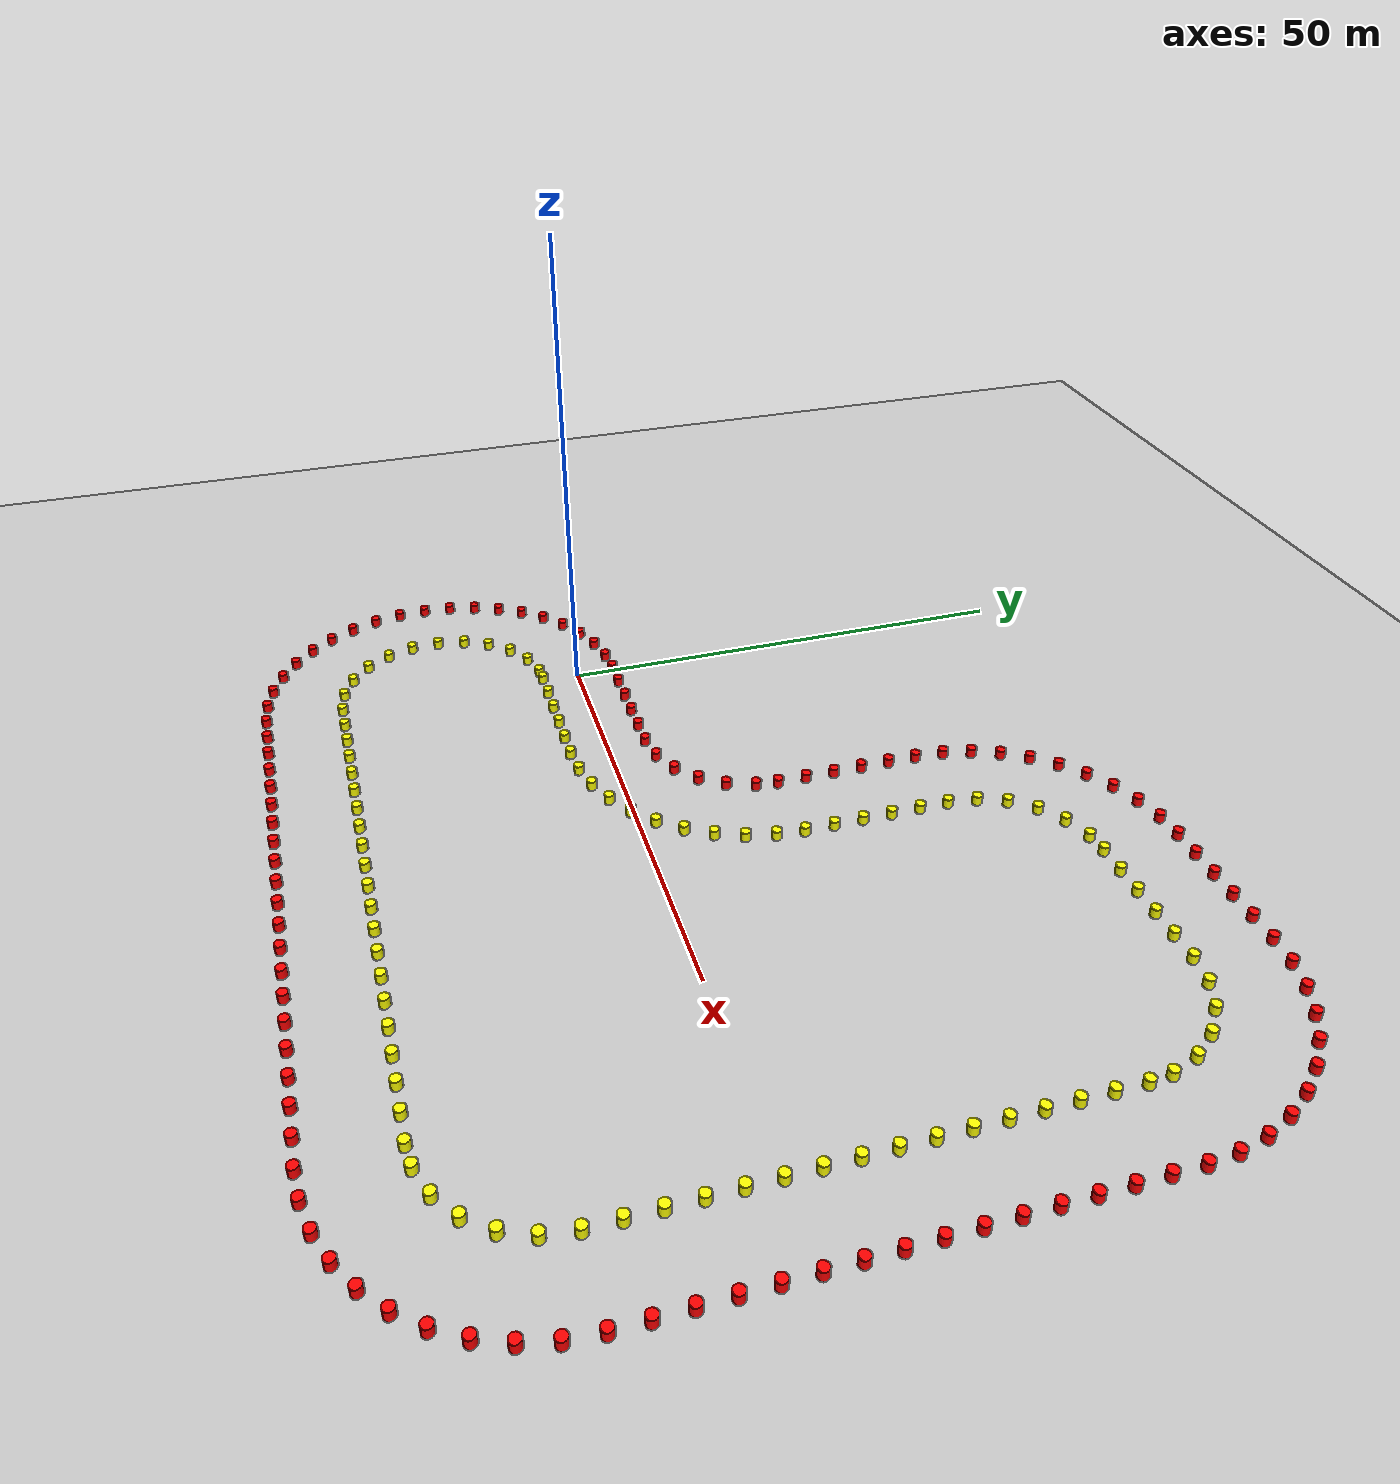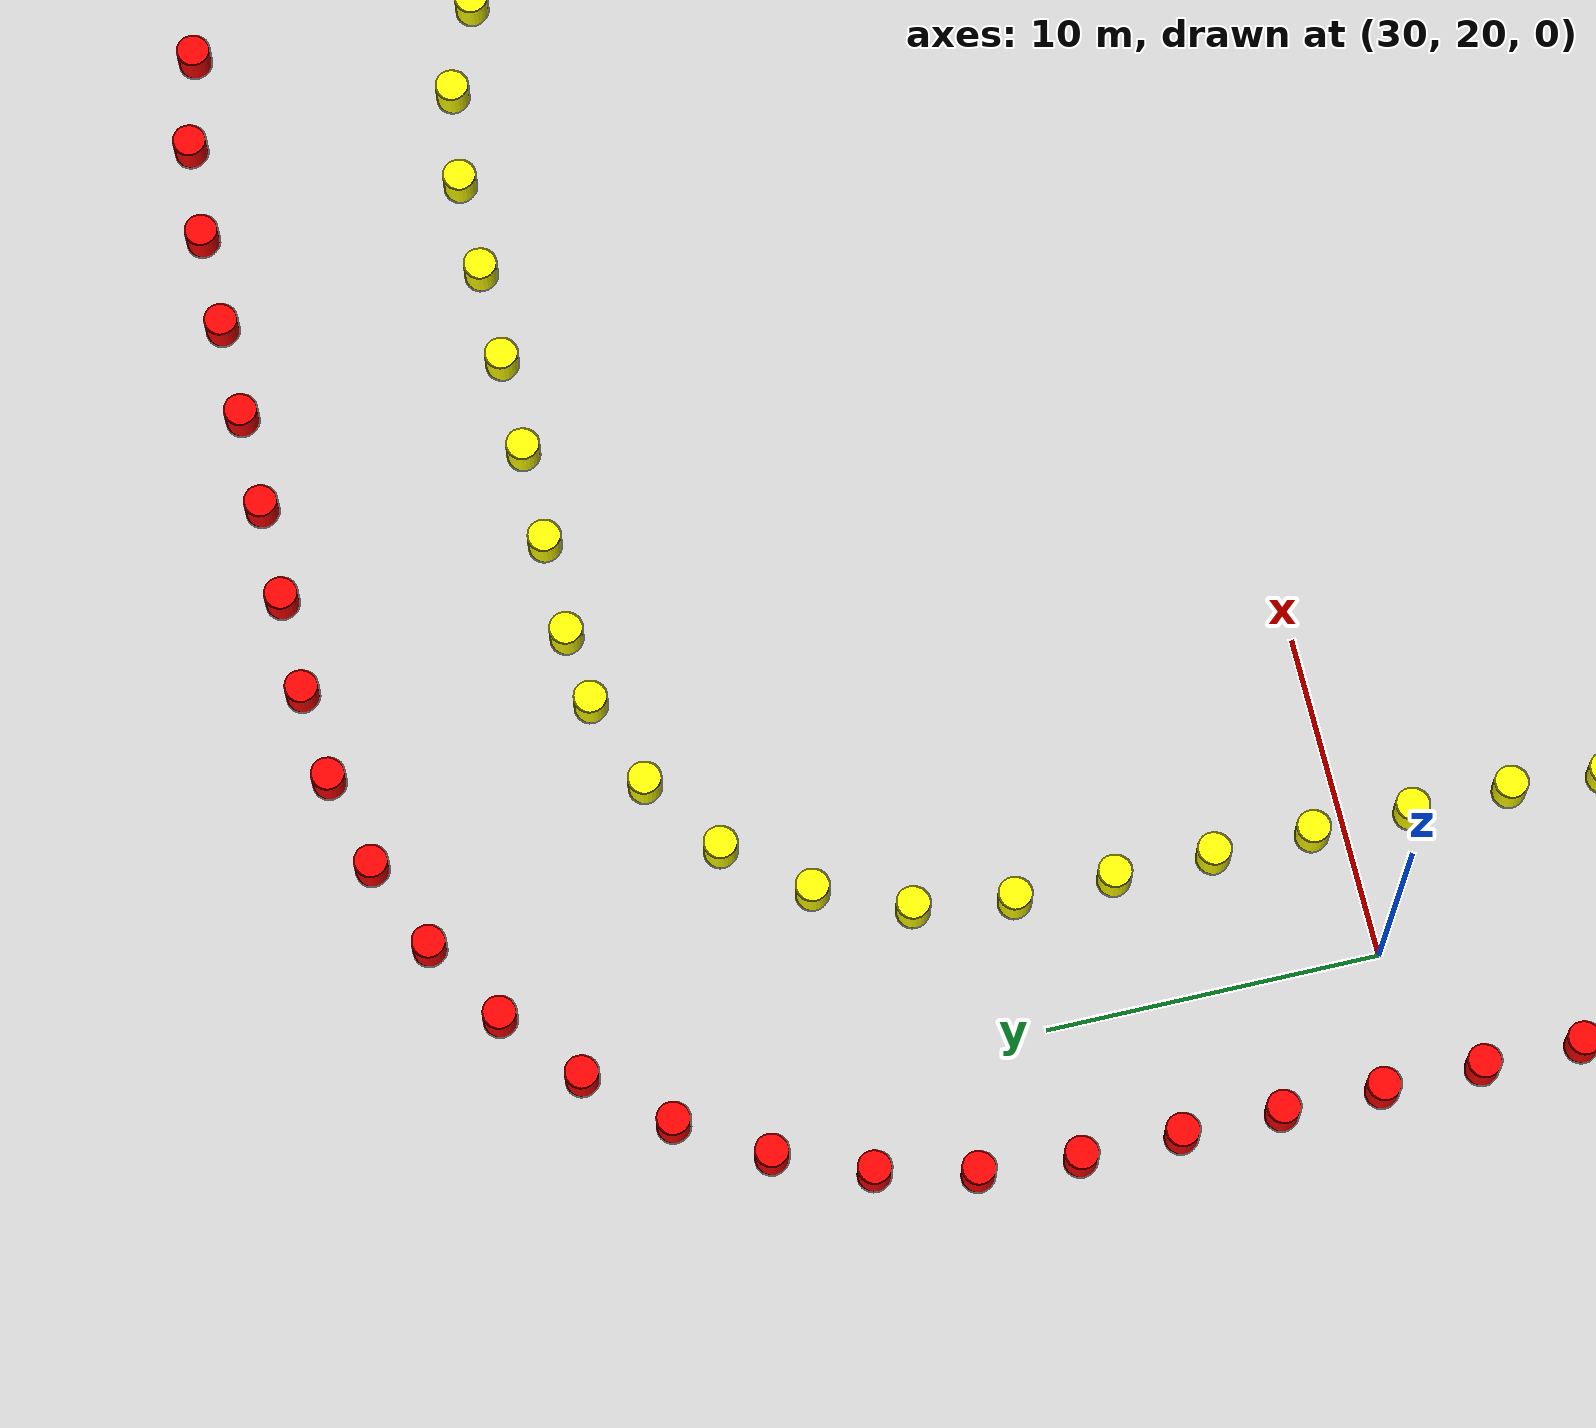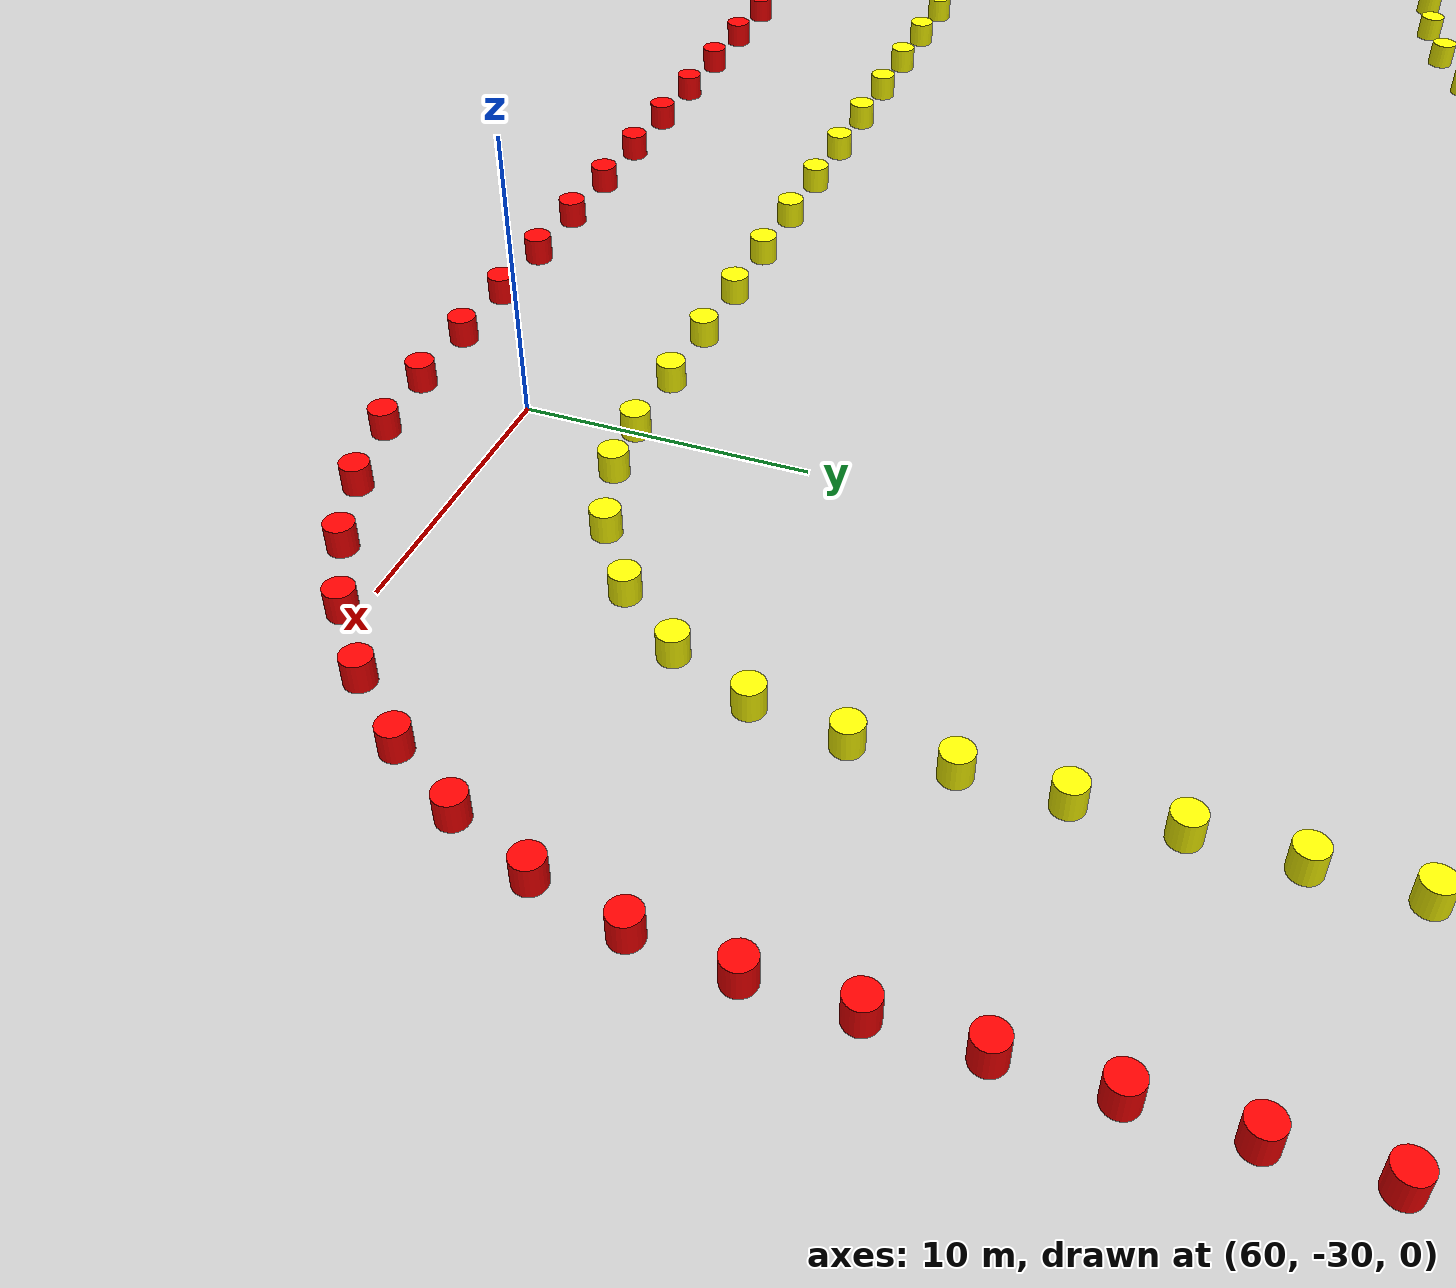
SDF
<sdf version='1.9'>
  <world name='empty'>
    <physics name='1ms' type='ignored'>
      <max_step_size>0.02</max_step_size>
      <real_time_factor>1</real_time_factor>
      <real_time_update_rate>100</real_time_update_rate>
    </physics>
    <plugin name='gz::sim::systems::Physics' filename='ignition-gazebo-physics-system'/>
    <plugin name='gz::sim::systems::UserCommands' filename='ignition-gazebo-user-commands-system'/>
    <plugin name='gz::sim::systems::SceneBroadcaster' filename='ignition-gazebo-scene-broadcaster-system'/>
    <plugin name='gz::sim::systems::Contact' filename='ignition-gazebo-contact-system'/>
    <gravity>0 0 -9.8</gravity>
    <magnetic_field>6e-06 2.3e-05 -4.2e-05</magnetic_field>
    <atmosphere type='adiabatic'/>
    <scene>
      <ambient>1 1 1 1</ambient>
      <background>1 1 1 1</background>
      <shadows>false</shadows>
    </scene>
    <model name='ground_plane'>
      <static>true</static>
      <link name='link'>
        <collision name='collision'>
          <geometry>
            <plane>
              <normal>0 0 1</normal>
              <size>1000 1000</size>
            </plane>
          </geometry>
          <surface>
            <friction>
              <ode/>
            </friction>
            <bounce/>
            <contact/>
          </surface>
        </collision>
        <visual name='visual'>
          <geometry>
            <plane>
              <normal>0 0 1</normal>
              <size>1000 1000</size>
            </plane>
          </geometry>
          <material>
            <ambient>0.8 0.8 0.8 1</ambient>
            <diffuse>0.8 0.8 0.8 1</diffuse>
            <specular>0.8 0.8 0.8 1</specular>
          </material>
        </visual>
        <pose>0 0 0 0 -0 0</pose>
        <inertial>
          <pose>0 0 0 0 -0 0</pose>
          <mass>1</mass>
          <inertia>
            <ixx>1</ixx>
            <ixy>0</ixy>
            <ixz>0</ixz>
            <iyy>1</iyy>
            <iyz>0</iyz>
            <izz>1</izz>
          </inertia>
        </inertial>
        <enable_wind>false</enable_wind>
      </link>
      <pose>0 0 0 0 -0 0</pose>
      <self_collide>false</self_collide>
    </model>
    <light name='sun' type='directional'>
      <pose>0 0 10 0 -0 0</pose>
      <cast_shadows>true</cast_shadows>
      <intensity>1</intensity>
      <direction>-0.5 0.1 -0.9</direction>
      <diffuse>0.8 0.8 0.8 1</diffuse>
      <specular>0.2 0.2 0.2 1</specular>
      <attenuation>
        <range>1000</range>
        <linear>0.01</linear>
        <constant>0.90000000000000002</constant>
        <quadratic>0.001</quadratic>
      </attenuation>
      <spot>
        <inner_angle>0</inner_angle>
        <outer_angle>0</outer_angle>
        <falloff>0</falloff>
      </spot>
    </light>

    <model name='red_cone_0'>
       <pose>-2.4492935982947064e-16 4.0 0.5 0 -0 0</pose>
       <link name='cylinder_link'>
         <inertial>
           <inertia>
             <ixx>0.14580000000000001</ixx>
             <ixy>0</ixy>
             <ixz>0</ixz>
             <iyy>0.14580000000000001</iyy>
             <iyz>0</iyz>
             <izz>0.125</izz>
           </inertia>
           <mass>1</mass>
           <pose>0 0 0 0 -0 0</pose>
         </inertial>
         <collision name='cylinder_collision'>
           <geometry>
             <cylinder>
               <radius>0.5</radius>
               <length>1</length>
             </cylinder>
           </geometry>
           <surface>
             <friction>
               <ode/>
             </friction>
             <bounce/>
             <contact/>
           </surface>
         </collision>
         <visual name='cylinder_visual'>
           <geometry>
             <cylinder>
               <radius>0.5</radius>
               <length>1</length>
             </cylinder>
           </geometry>
           <material>
             <ambient>1 0 0 1</ambient>
             <diffuse>1 0 0 1</diffuse>
             <specular>1 1 1 1</specular>
           </material>
         </visual>
         <pose>0 0 0 0 -0 0</pose>
         <enable_wind>false</enable_wind>
       </link>
       <static>false</static>
       <self_collide>false</self_collide>
     </model>

    <model name='red_cone_1'>
       <pose>2.9999999999999996 4.0 0.5 0 -0 0</pose>
       <link name='cylinder_link'>
         <inertial>
           <inertia>
             <ixx>0.14580000000000001</ixx>
             <ixy>0</ixy>
             <ixz>0</ixz>
             <iyy>0.14580000000000001</iyy>
             <iyz>0</iyz>
             <izz>0.125</izz>
           </inertia>
           <mass>1</mass>
           <pose>0 0 0 0 -0 0</pose>
         </inertial>
         <collision name='cylinder_collision'>
           <geometry>
             <cylinder>
               <radius>0.5</radius>
               <length>1</length>
             </cylinder>
           </geometry>
           <surface>
             <friction>
               <ode/>
             </friction>
             <bounce/>
             <contact/>
           </surface>
         </collision>
         <visual name='cylinder_visual'>
           <geometry>
             <cylinder>
               <radius>0.5</radius>
               <length>1</length>
             </cylinder>
           </geometry>
           <material>
             <ambient>1 0 0 1</ambient>
             <diffuse>1 0 0 1</diffuse>
             <specular>1 1 1 1</specular>
           </material>
         </visual>
         <pose>0 0 0 0 -0 0</pose>
         <enable_wind>false</enable_wind>
       </link>
       <static>false</static>
       <self_collide>false</self_collide>
     </model>

    <model name='red_cone_2'>
       <pose>6.0 4.0 0.5 0 -0 0</pose>
       <link name='cylinder_link'>
         <inertial>
           <inertia>
             <ixx>0.14580000000000001</ixx>
             <ixy>0</ixy>
             <ixz>0</ixz>
             <iyy>0.14580000000000001</iyy>
             <iyz>0</iyz>
             <izz>0.125</izz>
           </inertia>
           <mass>1</mass>
           <pose>0 0 0 0 -0 0</pose>
         </inertial>
         <collision name='cylinder_collision'>
           <geometry>
             <cylinder>
               <radius>0.5</radius>
               <length>1</length>
             </cylinder>
           </geometry>
           <surface>
             <friction>
               <ode/>
             </friction>
             <bounce/>
             <contact/>
           </surface>
         </collision>
         <visual name='cylinder_visual'>
           <geometry>
             <cylinder>
               <radius>0.5</radius>
               <length>1</length>
             </cylinder>
           </geometry>
           <material>
             <ambient>1 0 0 1</ambient>
             <diffuse>1 0 0 1</diffuse>
             <specular>1 1 1 1</specular>
           </material>
         </visual>
         <pose>0 0 0 0 -0 0</pose>
         <enable_wind>false</enable_wind>
       </link>
       <static>false</static>
       <self_collide>false</self_collide>
     </model>

    <model name='red_cone_3'>
       <pose>9.0 4.000000000000001 0.5 0 -0 0</pose>
       <link name='cylinder_link'>
         <inertial>
           <inertia>
             <ixx>0.14580000000000001</ixx>
             <ixy>0</ixy>
             <ixz>0</ixz>
             <iyy>0.14580000000000001</iyy>
             <iyz>0</iyz>
             <izz>0.125</izz>
           </inertia>
           <mass>1</mass>
           <pose>0 0 0 0 -0 0</pose>
         </inertial>
         <collision name='cylinder_collision'>
           <geometry>
             <cylinder>
               <radius>0.5</radius>
               <length>1</length>
             </cylinder>
           </geometry>
           <surface>
             <friction>
               <ode/>
             </friction>
             <bounce/>
             <contact/>
           </surface>
         </collision>
         <visual name='cylinder_visual'>
           <geometry>
             <cylinder>
               <radius>0.5</radius>
               <length>1</length>
             </cylinder>
           </geometry>
           <material>
             <ambient>1 0 0 1</ambient>
             <diffuse>1 0 0 1</diffuse>
             <specular>1 1 1 1</specular>
           </material>
         </visual>
         <pose>0 0 0 0 -0 0</pose>
         <enable_wind>false</enable_wind>
       </link>
       <static>false</static>
       <self_collide>false</self_collide>
     </model>

    <model name='red_cone_4'>
       <pose>12.0 4.000000000000001 0.5 0 -0 0</pose>
       <link name='cylinder_link'>
         <inertial>
           <inertia>
             <ixx>0.14580000000000001</ixx>
             <ixy>0</ixy>
             <ixz>0</ixz>
             <iyy>0.14580000000000001</iyy>
             <iyz>0</iyz>
             <izz>0.125</izz>
           </inertia>
           <mass>1</mass>
           <pose>0 0 0 0 -0 0</pose>
         </inertial>
         <collision name='cylinder_collision'>
           <geometry>
             <cylinder>
               <radius>0.5</radius>
               <length>1</length>
             </cylinder>
           </geometry>
           <surface>
             <friction>
               <ode/>
             </friction>
             <bounce/>
             <contact/>
           </surface>
         </collision>
         <visual name='cylinder_visual'>
           <geometry>
             <cylinder>
               <radius>0.5</radius>
               <length>1</length>
             </cylinder>
           </geometry>
           <material>
             <ambient>1 0 0 1</ambient>
             <diffuse>1 0 0 1</diffuse>
             <specular>1 1 1 1</specular>
           </material>
         </visual>
         <pose>0 0 0 0 -0 0</pose>
         <enable_wind>false</enable_wind>
       </link>
       <static>false</static>
       <self_collide>false</self_collide>
     </model>

    <model name='red_cone_5'>
       <pose>15.0 4.000000000000001 0.5 0 -0 0</pose>
       <link name='cylinder_link'>
         <inertial>
           <inertia>
             <ixx>0.14580000000000001</ixx>
             <ixy>0</ixy>
             <ixz>0</ixz>
             <iyy>0.14580000000000001</iyy>
             <iyz>0</iyz>
             <izz>0.125</izz>
           </inertia>
           <mass>1</mass>
           <pose>0 0 0 0 -0 0</pose>
         </inertial>
         <collision name='cylinder_collision'>
           <geometry>
             <cylinder>
               <radius>0.5</radius>
               <length>1</length>
             </cylinder>
           </geometry>
           <surface>
             <friction>
               <ode/>
             </friction>
             <bounce/>
             <contact/>
           </surface>
         </collision>
         <visual name='cylinder_visual'>
           <geometry>
             <cylinder>
               <radius>0.5</radius>
               <length>1</length>
             </cylinder>
           </geometry>
           <material>
             <ambient>1 0 0 1</ambient>
             <diffuse>1 0 0 1</diffuse>
             <specular>1 1 1 1</specular>
           </material>
         </visual>
         <pose>0 0 0 0 -0 0</pose>
         <enable_wind>false</enable_wind>
       </link>
       <static>false</static>
       <self_collide>false</self_collide>
     </model>

    <model name='red_cone_6'>
       <pose>15.0 4.0 0.5 0 -0 0</pose>
       <link name='cylinder_link'>
         <inertial>
           <inertia>
             <ixx>0.14580000000000001</ixx>
             <ixy>0</ixy>
             <ixz>0</ixz>
             <iyy>0.14580000000000001</iyy>
             <iyz>0</iyz>
             <izz>0.125</izz>
           </inertia>
           <mass>1</mass>
           <pose>0 0 0 0 -0 0</pose>
         </inertial>
         <collision name='cylinder_collision'>
           <geometry>
             <cylinder>
               <radius>0.5</radius>
               <length>1</length>
             </cylinder>
           </geometry>
           <surface>
             <friction>
               <ode/>
             </friction>
             <bounce/>
             <contact/>
           </surface>
         </collision>
         <visual name='cylinder_visual'>
           <geometry>
             <cylinder>
               <radius>0.5</radius>
               <length>1</length>
             </cylinder>
           </geometry>
           <material>
             <ambient>1 0 0 1</ambient>
             <diffuse>1 0 0 1</diffuse>
             <specular>1 1 1 1</specular>
           </material>
         </visual>
         <pose>0 0 0 0 -0 0</pose>
         <enable_wind>false</enable_wind>
       </link>
       <static>false</static>
       <self_collide>false</self_collide>
     </model>

    <model name='red_cone_7'>
       <pose>17.962947982891585 4.406561500122885 0.5 0 -0 0</pose>
       <link name='cylinder_link'>
         <inertial>
           <inertia>
             <ixx>0.14580000000000001</ixx>
             <ixy>0</ixy>
             <ixz>0</ixz>
             <iyy>0.14580000000000001</iyy>
             <iyz>0</iyz>
             <izz>0.125</izz>
           </inertia>
           <mass>1</mass>
           <pose>0 0 0 0 -0 0</pose>
         </inertial>
         <collision name='cylinder_collision'>
           <geometry>
             <cylinder>
               <radius>0.5</radius>
               <length>1</length>
             </cylinder>
           </geometry>
           <surface>
             <friction>
               <ode/>
             </friction>
             <bounce/>
             <contact/>
           </surface>
         </collision>
         <visual name='cylinder_visual'>
           <geometry>
             <cylinder>
               <radius>0.5</radius>
               <length>1</length>
             </cylinder>
           </geometry>
           <material>
             <ambient>1 0 0 1</ambient>
             <diffuse>1 0 0 1</diffuse>
             <specular>1 1 1 1</specular>
           </material>
         </visual>
         <pose>0 0 0 0 -0 0</pose>
         <enable_wind>false</enable_wind>
       </link>
       <static>false</static>
       <self_collide>false</self_collide>
     </model>

    <model name='red_cone_8'>
       <pose>20.7068740427449 5.596192863512966 0.5 0 -0 0</pose>
       <link name='cylinder_link'>
         <inertial>
           <inertia>
             <ixx>0.14580000000000001</ixx>
             <ixy>0</ixy>
             <ixz>0</ixz>
             <iyy>0.14580000000000001</iyy>
             <iyz>0</iyz>
             <izz>0.125</izz>
           </inertia>
           <mass>1</mass>
           <pose>0 0 0 0 -0 0</pose>
         </inertial>
         <collision name='cylinder_collision'>
           <geometry>
             <cylinder>
               <radius>0.5</radius>
               <length>1</length>
             </cylinder>
           </geometry>
           <surface>
             <friction>
               <ode/>
             </friction>
             <bounce/>
             <contact/>
           </surface>
         </collision>
         <visual name='cylinder_visual'>
           <geometry>
             <cylinder>
               <radius>0.5</radius>
               <length>1</length>
             </cylinder>
           </geometry>
           <material>
             <ambient>1 0 0 1</ambient>
             <diffuse>1 0 0 1</diffuse>
             <specular>1 1 1 1</specular>
           </material>
         </visual>
         <pose>0 0 0 0 -0 0</pose>
         <enable_wind>false</enable_wind>
       </link>
       <static>false</static>
       <self_collide>false</self_collide>
     </model>

    <model name='red_cone_9'>
       <pose>23.02894641681081 7.48095621531695 0.5 0 -0 0</pose>
       <link name='cylinder_link'>
         <inertial>
           <inertia>
             <ixx>0.14580000000000001</ixx>
             <ixy>0</ixy>
             <ixz>0</ixz>
             <iyy>0.14580000000000001</iyy>
             <iyz>0</iyz>
             <izz>0.125</izz>
           </inertia>
           <mass>1</mass>
           <pose>0 0 0 0 -0 0</pose>
         </inertial>
         <collision name='cylinder_collision'>
           <geometry>
             <cylinder>
               <radius>0.5</radius>
               <length>1</length>
             </cylinder>
           </geometry>
           <surface>
             <friction>
               <ode/>
             </friction>
             <bounce/>
             <contact/>
           </surface>
         </collision>
         <visual name='cylinder_visual'>
           <geometry>
             <cylinder>
               <radius>0.5</radius>
               <length>1</length>
             </cylinder>
           </geometry>
           <material>
             <ambient>1 0 0 1</ambient>
             <diffuse>1 0 0 1</diffuse>
             <specular>1 1 1 1</specular>
           </material>
         </visual>
         <pose>0 0 0 0 -0 0</pose>
         <enable_wind>false</enable_wind>
       </link>
       <static>false</static>
       <self_collide>false</self_collide>
     </model>

    <model name='red_cone_10'>
       <pose>24.75751688185402 9.921529334501004 0.5 0 -0 0</pose>
       <link name='cylinder_link'>
         <inertial>
           <inertia>
             <ixx>0.14580000000000001</ixx>
             <ixy>0</ixy>
             <ixz>0</ixz>
             <iyy>0.14580000000000001</iyy>
             <iyz>0</iyz>
             <izz>0.125</izz>
           </inertia>
           <mass>1</mass>
           <pose>0 0 0 0 -0 0</pose>
         </inertial>
         <collision name='cylinder_collision'>
           <geometry>
             <cylinder>
               <radius>0.5</radius>
               <length>1</length>
             </cylinder>
           </geometry>
           <surface>
             <friction>
               <ode/>
             </friction>
             <bounce/>
             <contact/>
           </surface>
         </collision>
         <visual name='cylinder_visual'>
           <geometry>
             <cylinder>
               <radius>0.5</radius>
               <length>1</length>
             </cylinder>
           </geometry>
           <material>
             <ambient>1 0 0 1</ambient>
             <diffuse>1 0 0 1</diffuse>
             <specular>1 1 1 1</specular>
           </material>
         </visual>
         <pose>0 0 0 0 -0 0</pose>
         <enable_wind>false</enable_wind>
       </link>
       <static>false</static>
       <self_collide>false</self_collide>
     </model>

    <model name='red_cone_11'>
       <pose>25.7648090376316 12.737504390429667 0.5 0 -0 0</pose>
       <link name='cylinder_link'>
         <inertial>
           <inertia>
             <ixx>0.14580000000000001</ixx>
             <ixy>0</ixy>
             <ixz>0</ixz>
             <iyy>0.14580000000000001</iyy>
             <iyz>0</iyz>
             <izz>0.125</izz>
           </inertia>
           <mass>1</mass>
           <pose>0 0 0 0 -0 0</pose>
         </inertial>
         <collision name='cylinder_collision'>
           <geometry>
             <cylinder>
               <radius>0.5</radius>
               <length>1</length>
             </cylinder>
           </geometry>
           <surface>
             <friction>
               <ode/>
             </friction>
             <bounce/>
             <contact/>
           </surface>
         </collision>
         <visual name='cylinder_visual'>
           <geometry>
             <cylinder>
               <radius>0.5</radius>
               <length>1</length>
             </cylinder>
           </geometry>
           <material>
             <ambient>1 0 0 1</ambient>
             <diffuse>1 0 0 1</diffuse>
             <specular>1 1 1 1</specular>
           </material>
         </visual>
         <pose>0 0 0 0 -0 0</pose>
         <enable_wind>false</enable_wind>
       </link>
       <static>false</static>
       <self_collide>false</self_collide>
     </model>

    <model name='red_cone_12'>
       <pose>26.0 15.0 0.5 0 -0 0</pose>
       <link name='cylinder_link'>
         <inertial>
           <inertia>
             <ixx>0.14580000000000001</ixx>
             <ixy>0</ixy>
             <ixz>0</ixz>
             <iyy>0.14580000000000001</iyy>
             <iyz>0</iyz>
             <izz>0.125</izz>
           </inertia>
           <mass>1</mass>
           <pose>0 0 0 0 -0 0</pose>
         </inertial>
         <collision name='cylinder_collision'>
           <geometry>
             <cylinder>
               <radius>0.5</radius>
               <length>1</length>
             </cylinder>
           </geometry>
           <surface>
             <friction>
               <ode/>
             </friction>
             <bounce/>
             <contact/>
           </surface>
         </collision>
         <visual name='cylinder_visual'>
           <geometry>
             <cylinder>
               <radius>0.5</radius>
               <length>1</length>
             </cylinder>
           </geometry>
           <material>
             <ambient>1 0 0 1</ambient>
             <diffuse>1 0 0 1</diffuse>
             <specular>1 1 1 1</specular>
           </material>
         </visual>
         <pose>0 0 0 0 -0 0</pose>
         <enable_wind>false</enable_wind>
       </link>
       <static>false</static>
       <self_collide>false</self_collide>
     </model>

    <model name='red_cone_13'>
       <pose>26.0 18.0 0.5 0 -0 0</pose>
       <link name='cylinder_link'>
         <inertial>
           <inertia>
             <ixx>0.14580000000000001</ixx>
             <ixy>0</ixy>
             <ixz>0</ixz>
             <iyy>0.14580000000000001</iyy>
             <iyz>0</iyz>
             <izz>0.125</izz>
           </inertia>
           <mass>1</mass>
           <pose>0 0 0 0 -0 0</pose>
         </inertial>
         <collision name='cylinder_collision'>
           <geometry>
             <cylinder>
               <radius>0.5</radius>
               <length>1</length>
             </cylinder>
           </geometry>
           <surface>
             <friction>
               <ode/>
             </friction>
             <bounce/>
             <contact/>
           </surface>
         </collision>
         <visual name='cylinder_visual'>
           <geometry>
             <cylinder>
               <radius>0.5</radius>
               <length>1</length>
             </cylinder>
           </geometry>
           <material>
             <ambient>1 0 0 1</ambient>
             <diffuse>1 0 0 1</diffuse>
             <specular>1 1 1 1</specular>
           </material>
         </visual>
         <pose>0 0 0 0 -0 0</pose>
         <enable_wind>false</enable_wind>
       </link>
       <static>false</static>
       <self_collide>false</self_collide>
     </model>

    <model name='red_cone_14'>
       <pose>26.0 21.0 0.5 0 -0 0</pose>
       <link name='cylinder_link'>
         <inertial>
           <inertia>
             <ixx>0.14580000000000001</ixx>
             <ixy>0</ixy>
             <ixz>0</ixz>
             <iyy>0.14580000000000001</iyy>
             <iyz>0</iyz>
             <izz>0.125</izz>
           </inertia>
           <mass>1</mass>
           <pose>0 0 0 0 -0 0</pose>
         </inertial>
         <collision name='cylinder_collision'>
           <geometry>
             <cylinder>
               <radius>0.5</radius>
               <length>1</length>
             </cylinder>
           </geometry>
           <surface>
             <friction>
               <ode/>
             </friction>
             <bounce/>
             <contact/>
           </surface>
         </collision>
         <visual name='cylinder_visual'>
           <geometry>
             <cylinder>
               <radius>0.5</radius>
               <length>1</length>
             </cylinder>
           </geometry>
           <material>
             <ambient>1 0 0 1</ambient>
             <diffuse>1 0 0 1</diffuse>
             <specular>1 1 1 1</specular>
           </material>
         </visual>
         <pose>0 0 0 0 -0 0</pose>
         <enable_wind>false</enable_wind>
       </link>
       <static>false</static>
       <self_collide>false</self_collide>
     </model>

    <model name='red_cone_15'>
       <pose>26.0 24.0 0.5 0 -0 0</pose>
       <link name='cylinder_link'>
         <inertial>
           <inertia>
             <ixx>0.14580000000000001</ixx>
             <ixy>0</ixy>
             <ixz>0</ixz>
             <iyy>0.14580000000000001</iyy>
             <iyz>0</iyz>
             <izz>0.125</izz>
           </inertia>
           <mass>1</mass>
           <pose>0 0 0 0 -0 0</pose>
         </inertial>
         <collision name='cylinder_collision'>
           <geometry>
             <cylinder>
               <radius>0.5</radius>
               <length>1</length>
             </cylinder>
           </geometry>
           <surface>
             <friction>
               <ode/>
             </friction>
             <bounce/>
             <contact/>
           </surface>
         </collision>
         <visual name='cylinder_visual'>
           <geometry>
             <cylinder>
               <radius>0.5</radius>
               <length>1</length>
             </cylinder>
           </geometry>
           <material>
             <ambient>1 0 0 1</ambient>
             <diffuse>1 0 0 1</diffuse>
             <specular>1 1 1 1</specular>
           </material>
         </visual>
         <pose>0 0 0 0 -0 0</pose>
         <enable_wind>false</enable_wind>
       </link>
       <static>false</static>
       <self_collide>false</self_collide>
     </model>

    <model name='red_cone_16'>
       <pose>26.0 27.0 0.5 0 -0 0</pose>
       <link name='cylinder_link'>
         <inertial>
           <inertia>
             <ixx>0.14580000000000001</ixx>
             <ixy>0</ixy>
             <ixz>0</ixz>
             <iyy>0.14580000000000001</iyy>
             <iyz>0</iyz>
             <izz>0.125</izz>
           </inertia>
           <mass>1</mass>
           <pose>0 0 0 0 -0 0</pose>
         </inertial>
         <collision name='cylinder_collision'>
           <geometry>
             <cylinder>
               <radius>0.5</radius>
               <length>1</length>
             </cylinder>
           </geometry>
           <surface>
             <friction>
               <ode/>
             </friction>
             <bounce/>
             <contact/>
           </surface>
         </collision>
         <visual name='cylinder_visual'>
           <geometry>
             <cylinder>
               <radius>0.5</radius>
               <length>1</length>
             </cylinder>
           </geometry>
           <material>
             <ambient>1 0 0 1</ambient>
             <diffuse>1 0 0 1</diffuse>
             <specular>1 1 1 1</specular>
           </material>
         </visual>
         <pose>0 0 0 0 -0 0</pose>
         <enable_wind>false</enable_wind>
       </link>
       <static>false</static>
       <self_collide>false</self_collide>
     </model>

    <model name='red_cone_17'>
       <pose>26.0 30.0 0.5 0 -0 0</pose>
       <link name='cylinder_link'>
         <inertial>
           <inertia>
             <ixx>0.14580000000000001</ixx>
             <ixy>0</ixy>
             <ixz>0</ixz>
             <iyy>0.14580000000000001</iyy>
             <iyz>0</iyz>
             <izz>0.125</izz>
           </inertia>
           <mass>1</mass>
           <pose>0 0 0 0 -0 0</pose>
         </inertial>
         <collision name='cylinder_collision'>
           <geometry>
             <cylinder>
               <radius>0.5</radius>
               <length>1</length>
             </cylinder>
           </geometry>
           <surface>
             <friction>
               <ode/>
             </friction>
             <bounce/>
             <contact/>
           </surface>
         </collision>
         <visual name='cylinder_visual'>
           <geometry>
             <cylinder>
               <radius>0.5</radius>
               <length>1</length>
             </cylinder>
           </geometry>
           <material>
             <ambient>1 0 0 1</ambient>
             <diffuse>1 0 0 1</diffuse>
             <specular>1 1 1 1</specular>
           </material>
         </visual>
         <pose>0 0 0 0 -0 0</pose>
         <enable_wind>false</enable_wind>
       </link>
       <static>false</static>
       <self_collide>false</self_collide>
     </model>

    <model name='red_cone_18'>
       <pose>26.0 29.999999999999996 0.5 0 -0 0</pose>
       <link name='cylinder_link'>
         <inertial>
           <inertia>
             <ixx>0.14580000000000001</ixx>
             <ixy>0</ixy>
             <ixz>0</ixz>
             <iyy>0.14580000000000001</iyy>
             <iyz>0</iyz>
             <izz>0.125</izz>
           </inertia>
           <mass>1</mass>
           <pose>0 0 0 0 -0 0</pose>
         </inertial>
         <collision name='cylinder_collision'>
           <geometry>
             <cylinder>
               <radius>0.5</radius>
               <length>1</length>
             </cylinder>
           </geometry>
           <surface>
             <friction>
               <ode/>
             </friction>
             <bounce/>
             <contact/>
           </surface>
         </collision>
         <visual name='cylinder_visual'>
           <geometry>
             <cylinder>
               <radius>0.5</radius>
               <length>1</length>
             </cylinder>
           </geometry>
           <material>
             <ambient>1 0 0 1</ambient>
             <diffuse>1 0 0 1</diffuse>
             <specular>1 1 1 1</specular>
           </material>
         </visual>
         <pose>0 0 0 0 -0 0</pose>
         <enable_wind>false</enable_wind>
       </link>
       <static>false</static>
       <self_collide>false</self_collide>
     </model>

    <model name='red_cone_19'>
       <pose>26.23635045975519 32.987550155373256 0.5 0 -0 0</pose>
       <link name='cylinder_link'>
         <inertial>
           <inertia>
             <ixx>0.14580000000000001</ixx>
             <ixy>0</ixy>
             <ixz>0</ixz>
             <iyy>0.14580000000000001</iyy>
             <iyz>0</iyz>
             <izz>0.125</izz>
           </inertia>
           <mass>1</mass>
           <pose>0 0 0 0 -0 0</pose>
         </inertial>
         <collision name='cylinder_collision'>
           <geometry>
             <cylinder>
               <radius>0.5</radius>
               <length>1</length>
             </cylinder>
           </geometry>
           <surface>
             <friction>
               <ode/>
             </friction>
             <bounce/>
             <contact/>
           </surface>
         </collision>
         <visual name='cylinder_visual'>
           <geometry>
             <cylinder>
               <radius>0.5</radius>
               <length>1</length>
             </cylinder>
           </geometry>
           <material>
             <ambient>1 0 0 1</ambient>
             <diffuse>1 0 0 1</diffuse>
             <specular>1 1 1 1</specular>
           </material>
         </visual>
         <pose>0 0 0 0 -0 0</pose>
         <enable_wind>false</enable_wind>
       </link>
       <static>false</static>
       <self_collide>false</self_collide>
     </model>

    <model name='red_cone_20'>
       <pose>26.939521676933765 35.90077306308712 0.5 0 -0 0</pose>
       <link name='cylinder_link'>
         <inertial>
           <inertia>
             <ixx>0.14580000000000001</ixx>
             <ixy>0</ixy>
             <ixz>0</ixz>
             <iyy>0.14580000000000001</iyy>
             <iyz>0</iyz>
             <izz>0.125</izz>
           </inertia>
           <mass>1</mass>
           <pose>0 0 0 0 -0 0</pose>
         </inertial>
         <collision name='cylinder_collision'>
           <geometry>
             <cylinder>
               <radius>0.5</radius>
               <length>1</length>
             </cylinder>
           </geometry>
           <surface>
             <friction>
               <ode/>
             </friction>
             <bounce/>
             <contact/>
           </surface>
         </collision>
         <visual name='cylinder_visual'>
           <geometry>
             <cylinder>
               <radius>0.5</radius>
               <length>1</length>
             </cylinder>
           </geometry>
           <material>
             <ambient>1 0 0 1</ambient>
             <diffuse>1 0 0 1</diffuse>
             <specular>1 1 1 1</specular>
           </material>
         </visual>
         <pose>0 0 0 0 -0 0</pose>
         <enable_wind>false</enable_wind>
       </link>
       <static>false</static>
       <self_collide>false</self_collide>
     </model>

    <model name='red_cone_21'>
       <pose>28.092019457802376 38.66719066276187 0.5 0 -0 0</pose>
       <link name='cylinder_link'>
         <inertial>
           <inertia>
             <ixx>0.14580000000000001</ixx>
             <ixy>0</ixy>
             <ixz>0</ixz>
             <iyy>0.14580000000000001</iyy>
             <iyz>0</iyz>
             <izz>0.125</izz>
           </inertia>
           <mass>1</mass>
           <pose>0 0 0 0 -0 0</pose>
         </inertial>
         <collision name='cylinder_collision'>
           <geometry>
             <cylinder>
               <radius>0.5</radius>
               <length>1</length>
             </cylinder>
           </geometry>
           <surface>
             <friction>
               <ode/>
             </friction>
             <bounce/>
             <contact/>
           </surface>
         </collision>
         <visual name='cylinder_visual'>
           <geometry>
             <cylinder>
               <radius>0.5</radius>
               <length>1</length>
             </cylinder>
           </geometry>
           <material>
             <ambient>1 0 0 1</ambient>
             <diffuse>1 0 0 1</diffuse>
             <specular>1 1 1 1</specular>
           </material>
         </visual>
         <pose>0 0 0 0 -0 0</pose>
         <enable_wind>false</enable_wind>
       </link>
       <static>false</static>
       <self_collide>false</self_collide>
     </model>

    <model name='red_cone_22'>
       <pose>29.665170814953115 41.21797726265454 0.5 0 -0 0</pose>
       <link name='cylinder_link'>
         <inertial>
           <inertia>
             <ixx>0.14580000000000001</ixx>
             <ixy>0</ixy>
             <ixz>0</ixz>
             <iyy>0.14580000000000001</iyy>
             <iyz>0</iyz>
             <izz>0.125</izz>
           </inertia>
           <mass>1</mass>
           <pose>0 0 0 0 -0 0</pose>
         </inertial>
         <collision name='cylinder_collision'>
           <geometry>
             <cylinder>
               <radius>0.5</radius>
               <length>1</length>
             </cylinder>
           </geometry>
           <surface>
             <friction>
               <ode/>
             </friction>
             <bounce/>
             <contact/>
           </surface>
         </collision>
         <visual name='cylinder_visual'>
           <geometry>
             <cylinder>
               <radius>0.5</radius>
               <length>1</length>
             </cylinder>
           </geometry>
           <material>
             <ambient>1 0 0 1</ambient>
             <diffuse>1 0 0 1</diffuse>
             <specular>1 1 1 1</specular>
           </material>
         </visual>
         <pose>0 0 0 0 -0 0</pose>
         <enable_wind>false</enable_wind>
       </link>
       <static>false</static>
       <self_collide>false</self_collide>
     </model>

    <model name='red_cone_23'>
       <pose>31.61983732243577 43.489671853752306 0.5 0 -0 0</pose>
       <link name='cylinder_link'>
         <inertial>
           <inertia>
             <ixx>0.14580000000000001</ixx>
             <ixy>0</ixy>
             <ixz>0</ixz>
             <iyy>0.14580000000000001</iyy>
             <iyz>0</iyz>
             <izz>0.125</izz>
           </inertia>
           <mass>1</mass>
           <pose>0 0 0 0 -0 0</pose>
         </inertial>
         <collision name='cylinder_collision'>
           <geometry>
             <cylinder>
               <radius>0.5</radius>
               <length>1</length>
             </cylinder>
           </geometry>
           <surface>
             <friction>
               <ode/>
             </friction>
             <bounce/>
             <contact/>
           </surface>
         </collision>
         <visual name='cylinder_visual'>
           <geometry>
             <cylinder>
               <radius>0.5</radius>
               <length>1</length>
             </cylinder>
           </geometry>
           <material>
             <ambient>1 0 0 1</ambient>
             <diffuse>1 0 0 1</diffuse>
             <specular>1 1 1 1</specular>
           </material>
         </visual>
         <pose>0 0 0 0 -0 0</pose>
         <enable_wind>false</enable_wind>
       </link>
       <static>false</static>
       <self_collide>false</self_collide>
     </model>

    <model name='red_cone_24'>
       <pose>33.907388840491215 45.4257569559468 0.5 0 -0 0</pose>
       <link name='cylinder_link'>
         <inertial>
           <inertia>
             <ixx>0.14580000000000001</ixx>
             <ixy>0</ixy>
             <ixz>0</ixz>
             <iyy>0.14580000000000001</iyy>
             <iyz>0</iyz>
             <izz>0.125</izz>
           </inertia>
           <mass>1</mass>
           <pose>0 0 0 0 -0 0</pose>
         </inertial>
         <collision name='cylinder_collision'>
           <geometry>
             <cylinder>
               <radius>0.5</radius>
               <length>1</length>
             </cylinder>
           </geometry>
           <surface>
             <friction>
               <ode/>
             </friction>
             <bounce/>
             <contact/>
           </surface>
         </collision>
         <visual name='cylinder_visual'>
           <geometry>
             <cylinder>
               <radius>0.5</radius>
               <length>1</length>
             </cylinder>
           </geometry>
           <material>
             <ambient>1 0 0 1</ambient>
             <diffuse>1 0 0 1</diffuse>
             <specular>1 1 1 1</specular>
           </material>
         </visual>
         <pose>0 0 0 0 -0 0</pose>
         <enable_wind>false</enable_wind>
       </link>
       <static>false</static>
       <self_collide>false</self_collide>
     </model>

    <model name='red_cone_25'>
       <pose>36.4709133845925 46.97806471618237 0.5 0 -0 0</pose>
       <link name='cylinder_link'>
         <inertial>
           <inertia>
             <ixx>0.14580000000000001</ixx>
             <ixy>0</ixy>
             <ixz>0</ixz>
             <iyy>0.14580000000000001</iyy>
             <iyz>0</iyz>
             <izz>0.125</izz>
           </inertia>
           <mass>1</mass>
           <pose>0 0 0 0 -0 0</pose>
         </inertial>
         <collision name='cylinder_collision'>
           <geometry>
             <cylinder>
               <radius>0.5</radius>
               <length>1</length>
             </cylinder>
           </geometry>
           <surface>
             <friction>
               <ode/>
             </friction>
             <bounce/>
             <contact/>
           </surface>
         </collision>
         <visual name='cylinder_visual'>
           <geometry>
             <cylinder>
               <radius>0.5</radius>
               <length>1</length>
             </cylinder>
           </geometry>
           <material>
             <ambient>1 0 0 1</ambient>
             <diffuse>1 0 0 1</diffuse>
             <specular>1 1 1 1</specular>
           </material>
         </visual>
         <pose>0 0 0 0 -0 0</pose>
         <enable_wind>false</enable_wind>
       </link>
       <static>false</static>
       <self_collide>false</self_collide>
     </model>

    <model name='red_cone_26'>
       <pose>39.246633038466776 48.107975276268135 0.5 0 -0 0</pose>
       <link name='cylinder_link'>
         <inertial>
           <inertia>
             <ixx>0.14580000000000001</ixx>
             <ixy>0</ixy>
             <ixz>0</ixz>
             <iyy>0.14580000000000001</iyy>
             <iyz>0</iyz>
             <izz>0.125</izz>
           </inertia>
           <mass>1</mass>
           <pose>0 0 0 0 -0 0</pose>
         </inertial>
         <collision name='cylinder_collision'>
           <geometry>
             <cylinder>
               <radius>0.5</radius>
               <length>1</length>
             </cylinder>
           </geometry>
           <surface>
             <friction>
               <ode/>
             </friction>
             <bounce/>
             <contact/>
           </surface>
         </collision>
         <visual name='cylinder_visual'>
           <geometry>
             <cylinder>
               <radius>0.5</radius>
               <length>1</length>
             </cylinder>
           </geometry>
           <material>
             <ambient>1 0 0 1</ambient>
             <diffuse>1 0 0 1</diffuse>
             <specular>1 1 1 1</specular>
           </material>
         </visual>
         <pose>0 0 0 0 -0 0</pose>
         <enable_wind>false</enable_wind>
       </link>
       <static>false</static>
       <self_collide>false</self_collide>
     </model>

    <model name='red_cone_27'>
       <pose>42.16549068460405 48.78737759616636 0.5 0 -0 0</pose>
       <link name='cylinder_link'>
         <inertial>
           <inertia>
             <ixx>0.14580000000000001</ixx>
             <ixy>0</ixy>
             <ixz>0</ixz>
             <iyy>0.14580000000000001</iyy>
             <iyz>0</iyz>
             <izz>0.125</izz>
           </inertia>
           <mass>1</mass>
           <pose>0 0 0 0 -0 0</pose>
         </inertial>
         <collision name='cylinder_collision'>
           <geometry>
             <cylinder>
               <radius>0.5</radius>
               <length>1</length>
             </cylinder>
           </geometry>
           <surface>
             <friction>
               <ode/>
             </friction>
             <bounce/>
             <contact/>
           </surface>
         </collision>
         <visual name='cylinder_visual'>
           <geometry>
             <cylinder>
               <radius>0.5</radius>
               <length>1</length>
             </cylinder>
           </geometry>
           <material>
             <ambient>1 0 0 1</ambient>
             <diffuse>1 0 0 1</diffuse>
             <specular>1 1 1 1</specular>
           </material>
         </visual>
         <pose>0 0 0 0 -0 0</pose>
         <enable_wind>false</enable_wind>
       </link>
       <static>false</static>
       <self_collide>false</self_collide>
     </model>

    <model name='red_cone_28'>
       <pose>45.0 49.0 0.5 0 -0 0</pose>
       <link name='cylinder_link'>
         <inertial>
           <inertia>
             <ixx>0.14580000000000001</ixx>
             <ixy>0</ixy>
             <ixz>0</ixz>
             <iyy>0.14580000000000001</iyy>
             <iyz>0</iyz>
             <izz>0.125</izz>
           </inertia>
           <mass>1</mass>
           <pose>0 0 0 0 -0 0</pose>
         </inertial>
         <collision name='cylinder_collision'>
           <geometry>
             <cylinder>
               <radius>0.5</radius>
               <length>1</length>
             </cylinder>
           </geometry>
           <surface>
             <friction>
               <ode/>
             </friction>
             <bounce/>
             <contact/>
           </surface>
         </collision>
         <visual name='cylinder_visual'>
           <geometry>
             <cylinder>
               <radius>0.5</radius>
               <length>1</length>
             </cylinder>
           </geometry>
           <material>
             <ambient>1 0 0 1</ambient>
             <diffuse>1 0 0 1</diffuse>
             <specular>1 1 1 1</specular>
           </material>
         </visual>
         <pose>0 0 0 0 -0 0</pose>
         <enable_wind>false</enable_wind>
       </link>
       <static>false</static>
       <self_collide>false</self_collide>
     </model>

    <model name='red_cone_29'>
       <pose>48.0 49.0 0.5 0 -0 0</pose>
       <link name='cylinder_link'>
         <inertial>
           <inertia>
             <ixx>0.14580000000000001</ixx>
             <ixy>0</ixy>
             <ixz>0</ixz>
             <iyy>0.14580000000000001</iyy>
             <iyz>0</iyz>
             <izz>0.125</izz>
           </inertia>
           <mass>1</mass>
           <pose>0 0 0 0 -0 0</pose>
         </inertial>
         <collision name='cylinder_collision'>
           <geometry>
             <cylinder>
               <radius>0.5</radius>
               <length>1</length>
             </cylinder>
           </geometry>
           <surface>
             <friction>
               <ode/>
             </friction>
             <bounce/>
             <contact/>
           </surface>
         </collision>
         <visual name='cylinder_visual'>
           <geometry>
             <cylinder>
               <radius>0.5</radius>
               <length>1</length>
             </cylinder>
           </geometry>
           <material>
             <ambient>1 0 0 1</ambient>
             <diffuse>1 0 0 1</diffuse>
             <specular>1 1 1 1</specular>
           </material>
         </visual>
         <pose>0 0 0 0 -0 0</pose>
         <enable_wind>false</enable_wind>
       </link>
       <static>false</static>
       <self_collide>false</self_collide>
     </model>

    <model name='red_cone_30'>
       <pose>51.0 49.0 0.5 0 -0 0</pose>
       <link name='cylinder_link'>
         <inertial>
           <inertia>
             <ixx>0.14580000000000001</ixx>
             <ixy>0</ixy>
             <ixz>0</ixz>
             <iyy>0.14580000000000001</iyy>
             <iyz>0</iyz>
             <izz>0.125</izz>
           </inertia>
           <mass>1</mass>
           <pose>0 0 0 0 -0 0</pose>
         </inertial>
         <collision name='cylinder_collision'>
           <geometry>
             <cylinder>
               <radius>0.5</radius>
               <length>1</length>
             </cylinder>
           </geometry>
           <surface>
             <friction>
               <ode/>
             </friction>
             <bounce/>
             <contact/>
           </surface>
         </collision>
         <visual name='cylinder_visual'>
           <geometry>
             <cylinder>
               <radius>0.5</radius>
               <length>1</length>
             </cylinder>
           </geometry>
           <material>
             <ambient>1 0 0 1</ambient>
             <diffuse>1 0 0 1</diffuse>
             <specular>1 1 1 1</specular>
           </material>
         </visual>
         <pose>0 0 0 0 -0 0</pose>
         <enable_wind>false</enable_wind>
       </link>
       <static>false</static>
       <self_collide>false</self_collide>
     </model>

    <model name='red_cone_31'>
       <pose>54.0 49.0 0.5 0 -0 0</pose>
       <link name='cylinder_link'>
         <inertial>
           <inertia>
             <ixx>0.14580000000000001</ixx>
             <ixy>0</ixy>
             <ixz>0</ixz>
             <iyy>0.14580000000000001</iyy>
             <iyz>0</iyz>
             <izz>0.125</izz>
           </inertia>
           <mass>1</mass>
           <pose>0 0 0 0 -0 0</pose>
         </inertial>
         <collision name='cylinder_collision'>
           <geometry>
             <cylinder>
               <radius>0.5</radius>
               <length>1</length>
             </cylinder>
           </geometry>
           <surface>
             <friction>
               <ode/>
             </friction>
             <bounce/>
             <contact/>
           </surface>
         </collision>
         <visual name='cylinder_visual'>
           <geometry>
             <cylinder>
               <radius>0.5</radius>
               <length>1</length>
             </cylinder>
           </geometry>
           <material>
             <ambient>1 0 0 1</ambient>
             <diffuse>1 0 0 1</diffuse>
             <specular>1 1 1 1</specular>
           </material>
         </visual>
         <pose>0 0 0 0 -0 0</pose>
         <enable_wind>false</enable_wind>
       </link>
       <static>false</static>
       <self_collide>false</self_collide>
     </model>

    <model name='red_cone_32'>
       <pose>57.0 49.0 0.5 0 -0 0</pose>
       <link name='cylinder_link'>
         <inertial>
           <inertia>
             <ixx>0.14580000000000001</ixx>
             <ixy>0</ixy>
             <ixz>0</ixz>
             <iyy>0.14580000000000001</iyy>
             <iyz>0</iyz>
             <izz>0.125</izz>
           </inertia>
           <mass>1</mass>
           <pose>0 0 0 0 -0 0</pose>
         </inertial>
         <collision name='cylinder_collision'>
           <geometry>
             <cylinder>
               <radius>0.5</radius>
               <length>1</length>
             </cylinder>
           </geometry>
           <surface>
             <friction>
               <ode/>
             </friction>
             <bounce/>
             <contact/>
           </surface>
         </collision>
         <visual name='cylinder_visual'>
           <geometry>
             <cylinder>
               <radius>0.5</radius>
               <length>1</length>
             </cylinder>
           </geometry>
           <material>
             <ambient>1 0 0 1</ambient>
             <diffuse>1 0 0 1</diffuse>
             <specular>1 1 1 1</specular>
           </material>
         </visual>
         <pose>0 0 0 0 -0 0</pose>
         <enable_wind>false</enable_wind>
       </link>
       <static>false</static>
       <self_collide>false</self_collide>
     </model>

    <model name='red_cone_33'>
       <pose>60.0 49.0 0.5 0 -0 0</pose>
       <link name='cylinder_link'>
         <inertial>
           <inertia>
             <ixx>0.14580000000000001</ixx>
             <ixy>0</ixy>
             <ixz>0</ixz>
             <iyy>0.14580000000000001</iyy>
             <iyz>0</iyz>
             <izz>0.125</izz>
           </inertia>
           <mass>1</mass>
           <pose>0 0 0 0 -0 0</pose>
         </inertial>
         <collision name='cylinder_collision'>
           <geometry>
             <cylinder>
               <radius>0.5</radius>
               <length>1</length>
             </cylinder>
           </geometry>
           <surface>
             <friction>
               <ode/>
             </friction>
             <bounce/>
             <contact/>
           </surface>
         </collision>
         <visual name='cylinder_visual'>
           <geometry>
             <cylinder>
               <radius>0.5</radius>
               <length>1</length>
             </cylinder>
           </geometry>
           <material>
             <ambient>1 0 0 1</ambient>
             <diffuse>1 0 0 1</diffuse>
             <specular>1 1 1 1</specular>
           </material>
         </visual>
         <pose>0 0 0 0 -0 0</pose>
         <enable_wind>false</enable_wind>
       </link>
       <static>false</static>
       <self_collide>false</self_collide>
     </model>

    <model name='red_cone_34'>
       <pose>60.0 49.0 0.5 0 -0 0</pose>
       <link name='cylinder_link'>
         <inertial>
           <inertia>
             <ixx>0.14580000000000001</ixx>
             <ixy>0</ixy>
             <ixz>0</ixz>
             <iyy>0.14580000000000001</iyy>
             <iyz>0</iyz>
             <izz>0.125</izz>
           </inertia>
           <mass>1</mass>
           <pose>0 0 0 0 -0 0</pose>
         </inertial>
         <collision name='cylinder_collision'>
           <geometry>
             <cylinder>
               <radius>0.5</radius>
               <length>1</length>
             </cylinder>
           </geometry>
           <surface>
             <friction>
               <ode/>
             </friction>
             <bounce/>
             <contact/>
           </surface>
         </collision>
         <visual name='cylinder_visual'>
           <geometry>
             <cylinder>
               <radius>0.5</radius>
               <length>1</length>
             </cylinder>
           </geometry>
           <material>
             <ambient>1 0 0 1</ambient>
             <diffuse>1 0 0 1</diffuse>
             <specular>1 1 1 1</specular>
           </material>
         </visual>
         <pose>0 0 0 0 -0 0</pose>
         <enable_wind>false</enable_wind>
       </link>
       <static>false</static>
       <self_collide>false</self_collide>
     </model>

    <model name='red_cone_35'>
       <pose>62.98755015537325 48.76364954024481 0.5 0 -0 0</pose>
       <link name='cylinder_link'>
         <inertial>
           <inertia>
             <ixx>0.14580000000000001</ixx>
             <ixy>0</ixy>
             <ixz>0</ixz>
             <iyy>0.14580000000000001</iyy>
             <iyz>0</iyz>
             <izz>0.125</izz>
           </inertia>
           <mass>1</mass>
           <pose>0 0 0 0 -0 0</pose>
         </inertial>
         <collision name='cylinder_collision'>
           <geometry>
             <cylinder>
               <radius>0.5</radius>
               <length>1</length>
             </cylinder>
           </geometry>
           <surface>
             <friction>
               <ode/>
             </friction>
             <bounce/>
             <contact/>
           </surface>
         </collision>
         <visual name='cylinder_visual'>
           <geometry>
             <cylinder>
               <radius>0.5</radius>
               <length>1</length>
             </cylinder>
           </geometry>
           <material>
             <ambient>1 0 0 1</ambient>
             <diffuse>1 0 0 1</diffuse>
             <specular>1 1 1 1</specular>
           </material>
         </visual>
         <pose>0 0 0 0 -0 0</pose>
         <enable_wind>false</enable_wind>
       </link>
       <static>false</static>
       <self_collide>false</self_collide>
     </model>

    <model name='red_cone_36'>
       <pose>65.90077306308712 48.060478323066235 0.5 0 -0 0</pose>
       <link name='cylinder_link'>
         <inertial>
           <inertia>
             <ixx>0.14580000000000001</ixx>
             <ixy>0</ixy>
             <ixz>0</ixz>
             <iyy>0.14580000000000001</iyy>
             <iyz>0</iyz>
             <izz>0.125</izz>
           </inertia>
           <mass>1</mass>
           <pose>0 0 0 0 -0 0</pose>
         </inertial>
         <collision name='cylinder_collision'>
           <geometry>
             <cylinder>
               <radius>0.5</radius>
               <length>1</length>
             </cylinder>
           </geometry>
           <surface>
             <friction>
               <ode/>
             </friction>
             <bounce/>
             <contact/>
           </surface>
         </collision>
         <visual name='cylinder_visual'>
           <geometry>
             <cylinder>
               <radius>0.5</radius>
               <length>1</length>
             </cylinder>
           </geometry>
           <material>
             <ambient>1 0 0 1</ambient>
             <diffuse>1 0 0 1</diffuse>
             <specular>1 1 1 1</specular>
           </material>
         </visual>
         <pose>0 0 0 0 -0 0</pose>
         <enable_wind>false</enable_wind>
       </link>
       <static>false</static>
       <self_collide>false</self_collide>
     </model>

    <model name='red_cone_37'>
       <pose>68.66719066276187 46.90798054219762 0.5 0 -0 0</pose>
       <link name='cylinder_link'>
         <inertial>
           <inertia>
             <ixx>0.14580000000000001</ixx>
             <ixy>0</ixy>
             <ixz>0</ixz>
             <iyy>0.14580000000000001</iyy>
             <iyz>0</iyz>
             <izz>0.125</izz>
           </inertia>
           <mass>1</mass>
           <pose>0 0 0 0 -0 0</pose>
         </inertial>
         <collision name='cylinder_collision'>
           <geometry>
             <cylinder>
               <radius>0.5</radius>
               <length>1</length>
             </cylinder>
           </geometry>
           <surface>
             <friction>
               <ode/>
             </friction>
             <bounce/>
             <contact/>
           </surface>
         </collision>
         <visual name='cylinder_visual'>
           <geometry>
             <cylinder>
               <radius>0.5</radius>
               <length>1</length>
             </cylinder>
           </geometry>
           <material>
             <ambient>1 0 0 1</ambient>
             <diffuse>1 0 0 1</diffuse>
             <specular>1 1 1 1</specular>
           </material>
         </visual>
         <pose>0 0 0 0 -0 0</pose>
         <enable_wind>false</enable_wind>
       </link>
       <static>false</static>
       <self_collide>false</self_collide>
     </model>

    <model name='red_cone_38'>
       <pose>71.21797726265454 45.334829185046885 0.5 0 -0 0</pose>
       <link name='cylinder_link'>
         <inertial>
           <inertia>
             <ixx>0.14580000000000001</ixx>
             <ixy>0</ixy>
             <ixz>0</ixz>
             <iyy>0.14580000000000001</iyy>
             <iyz>0</iyz>
             <izz>0.125</izz>
           </inertia>
           <mass>1</mass>
           <pose>0 0 0 0 -0 0</pose>
         </inertial>
         <collision name='cylinder_collision'>
           <geometry>
             <cylinder>
               <radius>0.5</radius>
               <length>1</length>
             </cylinder>
           </geometry>
           <surface>
             <friction>
               <ode/>
             </friction>
             <bounce/>
             <contact/>
           </surface>
         </collision>
         <visual name='cylinder_visual'>
           <geometry>
             <cylinder>
               <radius>0.5</radius>
               <length>1</length>
             </cylinder>
           </geometry>
           <material>
             <ambient>1 0 0 1</ambient>
             <diffuse>1 0 0 1</diffuse>
             <specular>1 1 1 1</specular>
           </material>
         </visual>
         <pose>0 0 0 0 -0 0</pose>
         <enable_wind>false</enable_wind>
       </link>
       <static>false</static>
       <self_collide>false</self_collide>
     </model>

    <model name='red_cone_39'>
       <pose>73.4896718537523 43.380162677564236 0.5 0 -0 0</pose>
       <link name='cylinder_link'>
         <inertial>
           <inertia>
             <ixx>0.14580000000000001</ixx>
             <ixy>0</ixy>
             <ixz>0</ixz>
             <iyy>0.14580000000000001</iyy>
             <iyz>0</iyz>
             <izz>0.125</izz>
           </inertia>
           <mass>1</mass>
           <pose>0 0 0 0 -0 0</pose>
         </inertial>
         <collision name='cylinder_collision'>
           <geometry>
             <cylinder>
               <radius>0.5</radius>
               <length>1</length>
             </cylinder>
           </geometry>
           <surface>
             <friction>
               <ode/>
             </friction>
             <bounce/>
             <contact/>
           </surface>
         </collision>
         <visual name='cylinder_visual'>
           <geometry>
             <cylinder>
               <radius>0.5</radius>
               <length>1</length>
             </cylinder>
           </geometry>
           <material>
             <ambient>1 0 0 1</ambient>
             <diffuse>1 0 0 1</diffuse>
             <specular>1 1 1 1</specular>
           </material>
         </visual>
         <pose>0 0 0 0 -0 0</pose>
         <enable_wind>false</enable_wind>
       </link>
       <static>false</static>
       <self_collide>false</self_collide>
     </model>

    <model name='red_cone_40'>
       <pose>75.42575695594681 41.09261115950879 0.5 0 -0 0</pose>
       <link name='cylinder_link'>
         <inertial>
           <inertia>
             <ixx>0.14580000000000001</ixx>
             <ixy>0</ixy>
             <ixz>0</ixz>
             <iyy>0.14580000000000001</iyy>
             <iyz>0</iyz>
             <izz>0.125</izz>
           </inertia>
           <mass>1</mass>
           <pose>0 0 0 0 -0 0</pose>
         </inertial>
         <collision name='cylinder_collision'>
           <geometry>
             <cylinder>
               <radius>0.5</radius>
               <length>1</length>
             </cylinder>
           </geometry>
           <surface>
             <friction>
               <ode/>
             </friction>
             <bounce/>
             <contact/>
           </surface>
         </collision>
         <visual name='cylinder_visual'>
           <geometry>
             <cylinder>
               <radius>0.5</radius>
               <length>1</length>
             </cylinder>
           </geometry>
           <material>
             <ambient>1 0 0 1</ambient>
             <diffuse>1 0 0 1</diffuse>
             <specular>1 1 1 1</specular>
           </material>
         </visual>
         <pose>0 0 0 0 -0 0</pose>
         <enable_wind>false</enable_wind>
       </link>
       <static>false</static>
       <self_collide>false</self_collide>
     </model>

    <model name='red_cone_41'>
       <pose>76.97806471618236 38.5290866154075 0.5 0 -0 0</pose>
       <link name='cylinder_link'>
         <inertial>
           <inertia>
             <ixx>0.14580000000000001</ixx>
             <ixy>0</ixy>
             <ixz>0</ixz>
             <iyy>0.14580000000000001</iyy>
             <iyz>0</iyz>
             <izz>0.125</izz>
           </inertia>
           <mass>1</mass>
           <pose>0 0 0 0 -0 0</pose>
         </inertial>
         <collision name='cylinder_collision'>
           <geometry>
             <cylinder>
               <radius>0.5</radius>
               <length>1</length>
             </cylinder>
           </geometry>
           <surface>
             <friction>
               <ode/>
             </friction>
             <bounce/>
             <contact/>
           </surface>
         </collision>
         <visual name='cylinder_visual'>
           <geometry>
             <cylinder>
               <radius>0.5</radius>
               <length>1</length>
             </cylinder>
           </geometry>
           <material>
             <ambient>1 0 0 1</ambient>
             <diffuse>1 0 0 1</diffuse>
             <specular>1 1 1 1</specular>
           </material>
         </visual>
         <pose>0 0 0 0 -0 0</pose>
         <enable_wind>false</enable_wind>
       </link>
       <static>false</static>
       <self_collide>false</self_collide>
     </model>

    <model name='red_cone_42'>
       <pose>78.10797527626814 35.753366961533224 0.5 0 -0 0</pose>
       <link name='cylinder_link'>
         <inertial>
           <inertia>
             <ixx>0.14580000000000001</ixx>
             <ixy>0</ixy>
             <ixz>0</ixz>
             <iyy>0.14580000000000001</iyy>
             <iyz>0</iyz>
             <izz>0.125</izz>
           </inertia>
           <mass>1</mass>
           <pose>0 0 0 0 -0 0</pose>
         </inertial>
         <collision name='cylinder_collision'>
           <geometry>
             <cylinder>
               <radius>0.5</radius>
               <length>1</length>
             </cylinder>
           </geometry>
           <surface>
             <friction>
               <ode/>
             </friction>
             <bounce/>
             <contact/>
           </surface>
         </collision>
         <visual name='cylinder_visual'>
           <geometry>
             <cylinder>
               <radius>0.5</radius>
               <length>1</length>
             </cylinder>
           </geometry>
           <material>
             <ambient>1 0 0 1</ambient>
             <diffuse>1 0 0 1</diffuse>
             <specular>1 1 1 1</specular>
           </material>
         </visual>
         <pose>0 0 0 0 -0 0</pose>
         <enable_wind>false</enable_wind>
       </link>
       <static>false</static>
       <self_collide>false</self_collide>
     </model>

    <model name='red_cone_43'>
       <pose>78.78737759616635 32.83450931539595 0.5 0 -0 0</pose>
       <link name='cylinder_link'>
         <inertial>
           <inertia>
             <ixx>0.14580000000000001</ixx>
             <ixy>0</ixy>
             <ixz>0</ixz>
             <iyy>0.14580000000000001</iyy>
             <iyz>0</iyz>
             <izz>0.125</izz>
           </inertia>
           <mass>1</mass>
           <pose>0 0 0 0 -0 0</pose>
         </inertial>
         <collision name='cylinder_collision'>
           <geometry>
             <cylinder>
               <radius>0.5</radius>
               <length>1</length>
             </cylinder>
           </geometry>
           <surface>
             <friction>
               <ode/>
             </friction>
             <bounce/>
             <contact/>
           </surface>
         </collision>
         <visual name='cylinder_visual'>
           <geometry>
             <cylinder>
               <radius>0.5</radius>
               <length>1</length>
             </cylinder>
           </geometry>
           <material>
             <ambient>1 0 0 1</ambient>
             <diffuse>1 0 0 1</diffuse>
             <specular>1 1 1 1</specular>
           </material>
         </visual>
         <pose>0 0 0 0 -0 0</pose>
         <enable_wind>false</enable_wind>
       </link>
       <static>false</static>
       <self_collide>false</self_collide>
     </model>

    <model name='red_cone_44'>
       <pose>79.0 30.000000000000004 0.5 0 -0 0</pose>
       <link name='cylinder_link'>
         <inertial>
           <inertia>
             <ixx>0.14580000000000001</ixx>
             <ixy>0</ixy>
             <ixz>0</ixz>
             <iyy>0.14580000000000001</iyy>
             <iyz>0</iyz>
             <izz>0.125</izz>
           </inertia>
           <mass>1</mass>
           <pose>0 0 0 0 -0 0</pose>
         </inertial>
         <collision name='cylinder_collision'>
           <geometry>
             <cylinder>
               <radius>0.5</radius>
               <length>1</length>
             </cylinder>
           </geometry>
           <surface>
             <friction>
               <ode/>
             </friction>
             <bounce/>
             <contact/>
           </surface>
         </collision>
         <visual name='cylinder_visual'>
           <geometry>
             <cylinder>
               <radius>0.5</radius>
               <length>1</length>
             </cylinder>
           </geometry>
           <material>
             <ambient>1 0 0 1</ambient>
             <diffuse>1 0 0 1</diffuse>
             <specular>1 1 1 1</specular>
           </material>
         </visual>
         <pose>0 0 0 0 -0 0</pose>
         <enable_wind>false</enable_wind>
       </link>
       <static>false</static>
       <self_collide>false</self_collide>
     </model>

    <model name='red_cone_45'>
       <pose>79.0 27.000000000000004 0.5 0 -0 0</pose>
       <link name='cylinder_link'>
         <inertial>
           <inertia>
             <ixx>0.14580000000000001</ixx>
             <ixy>0</ixy>
             <ixz>0</ixz>
             <iyy>0.14580000000000001</iyy>
             <iyz>0</iyz>
             <izz>0.125</izz>
           </inertia>
           <mass>1</mass>
           <pose>0 0 0 0 -0 0</pose>
         </inertial>
         <collision name='cylinder_collision'>
           <geometry>
             <cylinder>
               <radius>0.5</radius>
               <length>1</length>
             </cylinder>
           </geometry>
           <surface>
             <friction>
               <ode/>
             </friction>
             <bounce/>
             <contact/>
           </surface>
         </collision>
         <visual name='cylinder_visual'>
           <geometry>
             <cylinder>
               <radius>0.5</radius>
               <length>1</length>
             </cylinder>
           </geometry>
           <material>
             <ambient>1 0 0 1</ambient>
             <diffuse>1 0 0 1</diffuse>
             <specular>1 1 1 1</specular>
           </material>
         </visual>
         <pose>0 0 0 0 -0 0</pose>
         <enable_wind>false</enable_wind>
       </link>
       <static>false</static>
       <self_collide>false</self_collide>
     </model>

    <model name='red_cone_46'>
       <pose>79.0 24.000000000000004 0.5 0 -0 0</pose>
       <link name='cylinder_link'>
         <inertial>
           <inertia>
             <ixx>0.14580000000000001</ixx>
             <ixy>0</ixy>
             <ixz>0</ixz>
             <iyy>0.14580000000000001</iyy>
             <iyz>0</iyz>
             <izz>0.125</izz>
           </inertia>
           <mass>1</mass>
           <pose>0 0 0 0 -0 0</pose>
         </inertial>
         <collision name='cylinder_collision'>
           <geometry>
             <cylinder>
               <radius>0.5</radius>
               <length>1</length>
             </cylinder>
           </geometry>
           <surface>
             <friction>
               <ode/>
             </friction>
             <bounce/>
             <contact/>
           </surface>
         </collision>
         <visual name='cylinder_visual'>
           <geometry>
             <cylinder>
               <radius>0.5</radius>
               <length>1</length>
             </cylinder>
           </geometry>
           <material>
             <ambient>1 0 0 1</ambient>
             <diffuse>1 0 0 1</diffuse>
             <specular>1 1 1 1</specular>
           </material>
         </visual>
         <pose>0 0 0 0 -0 0</pose>
         <enable_wind>false</enable_wind>
       </link>
       <static>false</static>
       <self_collide>false</self_collide>
     </model>

    <model name='red_cone_47'>
       <pose>79.0 21.000000000000004 0.5 0 -0 0</pose>
       <link name='cylinder_link'>
         <inertial>
           <inertia>
             <ixx>0.14580000000000001</ixx>
             <ixy>0</ixy>
             <ixz>0</ixz>
             <iyy>0.14580000000000001</iyy>
             <iyz>0</iyz>
             <izz>0.125</izz>
           </inertia>
           <mass>1</mass>
           <pose>0 0 0 0 -0 0</pose>
         </inertial>
         <collision name='cylinder_collision'>
           <geometry>
             <cylinder>
               <radius>0.5</radius>
               <length>1</length>
             </cylinder>
           </geometry>
           <surface>
             <friction>
               <ode/>
             </friction>
             <bounce/>
             <contact/>
           </surface>
         </collision>
         <visual name='cylinder_visual'>
           <geometry>
             <cylinder>
               <radius>0.5</radius>
               <length>1</length>
             </cylinder>
           </geometry>
           <material>
             <ambient>1 0 0 1</ambient>
             <diffuse>1 0 0 1</diffuse>
             <specular>1 1 1 1</specular>
           </material>
         </visual>
         <pose>0 0 0 0 -0 0</pose>
         <enable_wind>false</enable_wind>
       </link>
       <static>false</static>
       <self_collide>false</self_collide>
     </model>

    <model name='red_cone_48'>
       <pose>79.0 18.000000000000004 0.5 0 -0 0</pose>
       <link name='cylinder_link'>
         <inertial>
           <inertia>
             <ixx>0.14580000000000001</ixx>
             <ixy>0</ixy>
             <ixz>0</ixz>
             <iyy>0.14580000000000001</iyy>
             <iyz>0</iyz>
             <izz>0.125</izz>
           </inertia>
           <mass>1</mass>
           <pose>0 0 0 0 -0 0</pose>
         </inertial>
         <collision name='cylinder_collision'>
           <geometry>
             <cylinder>
               <radius>0.5</radius>
               <length>1</length>
             </cylinder>
           </geometry>
           <surface>
             <friction>
               <ode/>
             </friction>
             <bounce/>
             <contact/>
           </surface>
         </collision>
         <visual name='cylinder_visual'>
           <geometry>
             <cylinder>
               <radius>0.5</radius>
               <length>1</length>
             </cylinder>
           </geometry>
           <material>
             <ambient>1 0 0 1</ambient>
             <diffuse>1 0 0 1</diffuse>
             <specular>1 1 1 1</specular>
           </material>
         </visual>
         <pose>0 0 0 0 -0 0</pose>
         <enable_wind>false</enable_wind>
       </link>
       <static>false</static>
       <self_collide>false</self_collide>
     </model>

    <model name='red_cone_49'>
       <pose>79.0 15.000000000000004 0.5 0 -0 0</pose>
       <link name='cylinder_link'>
         <inertial>
           <inertia>
             <ixx>0.14580000000000001</ixx>
             <ixy>0</ixy>
             <ixz>0</ixz>
             <iyy>0.14580000000000001</iyy>
             <iyz>0</iyz>
             <izz>0.125</izz>
           </inertia>
           <mass>1</mass>
           <pose>0 0 0 0 -0 0</pose>
         </inertial>
         <collision name='cylinder_collision'>
           <geometry>
             <cylinder>
               <radius>0.5</radius>
               <length>1</length>
             </cylinder>
           </geometry>
           <surface>
             <friction>
               <ode/>
             </friction>
             <bounce/>
             <contact/>
           </surface>
         </collision>
         <visual name='cylinder_visual'>
           <geometry>
             <cylinder>
               <radius>0.5</radius>
               <length>1</length>
             </cylinder>
           </geometry>
           <material>
             <ambient>1 0 0 1</ambient>
             <diffuse>1 0 0 1</diffuse>
             <specular>1 1 1 1</specular>
           </material>
         </visual>
         <pose>0 0 0 0 -0 0</pose>
         <enable_wind>false</enable_wind>
       </link>
       <static>false</static>
       <self_collide>false</self_collide>
     </model>

    <model name='red_cone_50'>
       <pose>79.0 12.000000000000004 0.5 0 -0 0</pose>
       <link name='cylinder_link'>
         <inertial>
           <inertia>
             <ixx>0.14580000000000001</ixx>
             <ixy>0</ixy>
             <ixz>0</ixz>
             <iyy>0.14580000000000001</iyy>
             <iyz>0</iyz>
             <izz>0.125</izz>
           </inertia>
           <mass>1</mass>
           <pose>0 0 0 0 -0 0</pose>
         </inertial>
         <collision name='cylinder_collision'>
           <geometry>
             <cylinder>
               <radius>0.5</radius>
               <length>1</length>
             </cylinder>
           </geometry>
           <surface>
             <friction>
               <ode/>
             </friction>
             <bounce/>
             <contact/>
           </surface>
         </collision>
         <visual name='cylinder_visual'>
           <geometry>
             <cylinder>
               <radius>0.5</radius>
               <length>1</length>
             </cylinder>
           </geometry>
           <material>
             <ambient>1 0 0 1</ambient>
             <diffuse>1 0 0 1</diffuse>
             <specular>1 1 1 1</specular>
           </material>
         </visual>
         <pose>0 0 0 0 -0 0</pose>
         <enable_wind>false</enable_wind>
       </link>
       <static>false</static>
       <self_collide>false</self_collide>
     </model>

    <model name='red_cone_51'>
       <pose>79.0 9.000000000000004 0.5 0 -0 0</pose>
       <link name='cylinder_link'>
         <inertial>
           <inertia>
             <ixx>0.14580000000000001</ixx>
             <ixy>0</ixy>
             <ixz>0</ixz>
             <iyy>0.14580000000000001</iyy>
             <iyz>0</iyz>
             <izz>0.125</izz>
           </inertia>
           <mass>1</mass>
           <pose>0 0 0 0 -0 0</pose>
         </inertial>
         <collision name='cylinder_collision'>
           <geometry>
             <cylinder>
               <radius>0.5</radius>
               <length>1</length>
             </cylinder>
           </geometry>
           <surface>
             <friction>
               <ode/>
             </friction>
             <bounce/>
             <contact/>
           </surface>
         </collision>
         <visual name='cylinder_visual'>
           <geometry>
             <cylinder>
               <radius>0.5</radius>
               <length>1</length>
             </cylinder>
           </geometry>
           <material>
             <ambient>1 0 0 1</ambient>
             <diffuse>1 0 0 1</diffuse>
             <specular>1 1 1 1</specular>
           </material>
         </visual>
         <pose>0 0 0 0 -0 0</pose>
         <enable_wind>false</enable_wind>
       </link>
       <static>false</static>
       <self_collide>false</self_collide>
     </model>

    <model name='red_cone_52'>
       <pose>79.0 6.0000000000000036 0.5 0 -0 0</pose>
       <link name='cylinder_link'>
         <inertial>
           <inertia>
             <ixx>0.14580000000000001</ixx>
             <ixy>0</ixy>
             <ixz>0</ixz>
             <iyy>0.14580000000000001</iyy>
             <iyz>0</iyz>
             <izz>0.125</izz>
           </inertia>
           <mass>1</mass>
           <pose>0 0 0 0 -0 0</pose>
         </inertial>
         <collision name='cylinder_collision'>
           <geometry>
             <cylinder>
               <radius>0.5</radius>
               <length>1</length>
             </cylinder>
           </geometry>
           <surface>
             <friction>
               <ode/>
             </friction>
             <bounce/>
             <contact/>
           </surface>
         </collision>
         <visual name='cylinder_visual'>
           <geometry>
             <cylinder>
               <radius>0.5</radius>
               <length>1</length>
             </cylinder>
           </geometry>
           <material>
             <ambient>1 0 0 1</ambient>
             <diffuse>1 0 0 1</diffuse>
             <specular>1 1 1 1</specular>
           </material>
         </visual>
         <pose>0 0 0 0 -0 0</pose>
         <enable_wind>false</enable_wind>
       </link>
       <static>false</static>
       <self_collide>false</self_collide>
     </model>

    <model name='red_cone_53'>
       <pose>79.0 3.0000000000000036 0.5 0 -0 0</pose>
       <link name='cylinder_link'>
         <inertial>
           <inertia>
             <ixx>0.14580000000000001</ixx>
             <ixy>0</ixy>
             <ixz>0</ixz>
             <iyy>0.14580000000000001</iyy>
             <iyz>0</iyz>
             <izz>0.125</izz>
           </inertia>
           <mass>1</mass>
           <pose>0 0 0 0 -0 0</pose>
         </inertial>
         <collision name='cylinder_collision'>
           <geometry>
             <cylinder>
               <radius>0.5</radius>
               <length>1</length>
             </cylinder>
           </geometry>
           <surface>
             <friction>
               <ode/>
             </friction>
             <bounce/>
             <contact/>
           </surface>
         </collision>
         <visual name='cylinder_visual'>
           <geometry>
             <cylinder>
               <radius>0.5</radius>
               <length>1</length>
             </cylinder>
           </geometry>
           <material>
             <ambient>1 0 0 1</ambient>
             <diffuse>1 0 0 1</diffuse>
             <specular>1 1 1 1</specular>
           </material>
         </visual>
         <pose>0 0 0 0 -0 0</pose>
         <enable_wind>false</enable_wind>
       </link>
       <static>false</static>
       <self_collide>false</self_collide>
     </model>

    <model name='red_cone_54'>
       <pose>79.0 3.552713678800501e-15 0.5 0 -0 0</pose>
       <link name='cylinder_link'>
         <inertial>
           <inertia>
             <ixx>0.14580000000000001</ixx>
             <ixy>0</ixy>
             <ixz>0</ixz>
             <iyy>0.14580000000000001</iyy>
             <iyz>0</iyz>
             <izz>0.125</izz>
           </inertia>
           <mass>1</mass>
           <pose>0 0 0 0 -0 0</pose>
         </inertial>
         <collision name='cylinder_collision'>
           <geometry>
             <cylinder>
               <radius>0.5</radius>
               <length>1</length>
             </cylinder>
           </geometry>
           <surface>
             <friction>
               <ode/>
             </friction>
             <bounce/>
             <contact/>
           </surface>
         </collision>
         <visual name='cylinder_visual'>
           <geometry>
             <cylinder>
               <radius>0.5</radius>
               <length>1</length>
             </cylinder>
           </geometry>
           <material>
             <ambient>1 0 0 1</ambient>
             <diffuse>1 0 0 1</diffuse>
             <specular>1 1 1 1</specular>
           </material>
         </visual>
         <pose>0 0 0 0 -0 0</pose>
         <enable_wind>false</enable_wind>
       </link>
       <static>false</static>
       <self_collide>false</self_collide>
     </model>

    <model name='red_cone_55'>
       <pose>79.0 -2.9999999999999964 0.5 0 -0 0</pose>
       <link name='cylinder_link'>
         <inertial>
           <inertia>
             <ixx>0.14580000000000001</ixx>
             <ixy>0</ixy>
             <ixz>0</ixz>
             <iyy>0.14580000000000001</iyy>
             <iyz>0</iyz>
             <izz>0.125</izz>
           </inertia>
           <mass>1</mass>
           <pose>0 0 0 0 -0 0</pose>
         </inertial>
         <collision name='cylinder_collision'>
           <geometry>
             <cylinder>
               <radius>0.5</radius>
               <length>1</length>
             </cylinder>
           </geometry>
           <surface>
             <friction>
               <ode/>
             </friction>
             <bounce/>
             <contact/>
           </surface>
         </collision>
         <visual name='cylinder_visual'>
           <geometry>
             <cylinder>
               <radius>0.5</radius>
               <length>1</length>
             </cylinder>
           </geometry>
           <material>
             <ambient>1 0 0 1</ambient>
             <diffuse>1 0 0 1</diffuse>
             <specular>1 1 1 1</specular>
           </material>
         </visual>
         <pose>0 0 0 0 -0 0</pose>
         <enable_wind>false</enable_wind>
       </link>
       <static>false</static>
       <self_collide>false</self_collide>
     </model>

    <model name='red_cone_56'>
       <pose>79.0 -5.9999999999999964 0.5 0 -0 0</pose>
       <link name='cylinder_link'>
         <inertial>
           <inertia>
             <ixx>0.14580000000000001</ixx>
             <ixy>0</ixy>
             <ixz>0</ixz>
             <iyy>0.14580000000000001</iyy>
             <iyz>0</iyz>
             <izz>0.125</izz>
           </inertia>
           <mass>1</mass>
           <pose>0 0 0 0 -0 0</pose>
         </inertial>
         <collision name='cylinder_collision'>
           <geometry>
             <cylinder>
               <radius>0.5</radius>
               <length>1</length>
             </cylinder>
           </geometry>
           <surface>
             <friction>
               <ode/>
             </friction>
             <bounce/>
             <contact/>
           </surface>
         </collision>
         <visual name='cylinder_visual'>
           <geometry>
             <cylinder>
               <radius>0.5</radius>
               <length>1</length>
             </cylinder>
           </geometry>
           <material>
             <ambient>1 0 0 1</ambient>
             <diffuse>1 0 0 1</diffuse>
             <specular>1 1 1 1</specular>
           </material>
         </visual>
         <pose>0 0 0 0 -0 0</pose>
         <enable_wind>false</enable_wind>
       </link>
       <static>false</static>
       <self_collide>false</self_collide>
     </model>

    <model name='red_cone_57'>
       <pose>79.0 -8.999999999999996 0.5 0 -0 0</pose>
       <link name='cylinder_link'>
         <inertial>
           <inertia>
             <ixx>0.14580000000000001</ixx>
             <ixy>0</ixy>
             <ixz>0</ixz>
             <iyy>0.14580000000000001</iyy>
             <iyz>0</iyz>
             <izz>0.125</izz>
           </inertia>
           <mass>1</mass>
           <pose>0 0 0 0 -0 0</pose>
         </inertial>
         <collision name='cylinder_collision'>
           <geometry>
             <cylinder>
               <radius>0.5</radius>
               <length>1</length>
             </cylinder>
           </geometry>
           <surface>
             <friction>
               <ode/>
             </friction>
             <bounce/>
             <contact/>
           </surface>
         </collision>
         <visual name='cylinder_visual'>
           <geometry>
             <cylinder>
               <radius>0.5</radius>
               <length>1</length>
             </cylinder>
           </geometry>
           <material>
             <ambient>1 0 0 1</ambient>
             <diffuse>1 0 0 1</diffuse>
             <specular>1 1 1 1</specular>
           </material>
         </visual>
         <pose>0 0 0 0 -0 0</pose>
         <enable_wind>false</enable_wind>
       </link>
       <static>false</static>
       <self_collide>false</self_collide>
     </model>

    <model name='red_cone_58'>
       <pose>79.0 -11.999999999999996 0.5 0 -0 0</pose>
       <link name='cylinder_link'>
         <inertial>
           <inertia>
             <ixx>0.14580000000000001</ixx>
             <ixy>0</ixy>
             <ixz>0</ixz>
             <iyy>0.14580000000000001</iyy>
             <iyz>0</iyz>
             <izz>0.125</izz>
           </inertia>
           <mass>1</mass>
           <pose>0 0 0 0 -0 0</pose>
         </inertial>
         <collision name='cylinder_collision'>
           <geometry>
             <cylinder>
               <radius>0.5</radius>
               <length>1</length>
             </cylinder>
           </geometry>
           <surface>
             <friction>
               <ode/>
             </friction>
             <bounce/>
             <contact/>
           </surface>
         </collision>
         <visual name='cylinder_visual'>
           <geometry>
             <cylinder>
               <radius>0.5</radius>
               <length>1</length>
             </cylinder>
           </geometry>
           <material>
             <ambient>1 0 0 1</ambient>
             <diffuse>1 0 0 1</diffuse>
             <specular>1 1 1 1</specular>
           </material>
         </visual>
         <pose>0 0 0 0 -0 0</pose>
         <enable_wind>false</enable_wind>
       </link>
       <static>false</static>
       <self_collide>false</self_collide>
     </model>

    <model name='red_cone_59'>
       <pose>79.0 -14.999999999999996 0.5 0 -0 0</pose>
       <link name='cylinder_link'>
         <inertial>
           <inertia>
             <ixx>0.14580000000000001</ixx>
             <ixy>0</ixy>
             <ixz>0</ixz>
             <iyy>0.14580000000000001</iyy>
             <iyz>0</iyz>
             <izz>0.125</izz>
           </inertia>
           <mass>1</mass>
           <pose>0 0 0 0 -0 0</pose>
         </inertial>
         <collision name='cylinder_collision'>
           <geometry>
             <cylinder>
               <radius>0.5</radius>
               <length>1</length>
             </cylinder>
           </geometry>
           <surface>
             <friction>
               <ode/>
             </friction>
             <bounce/>
             <contact/>
           </surface>
         </collision>
         <visual name='cylinder_visual'>
           <geometry>
             <cylinder>
               <radius>0.5</radius>
               <length>1</length>
             </cylinder>
           </geometry>
           <material>
             <ambient>1 0 0 1</ambient>
             <diffuse>1 0 0 1</diffuse>
             <specular>1 1 1 1</specular>
           </material>
         </visual>
         <pose>0 0 0 0 -0 0</pose>
         <enable_wind>false</enable_wind>
       </link>
       <static>false</static>
       <self_collide>false</self_collide>
     </model>

    <model name='red_cone_60'>
       <pose>79.0 -14.999999999999993 0.5 0 -0 0</pose>
       <link name='cylinder_link'>
         <inertial>
           <inertia>
             <ixx>0.14580000000000001</ixx>
             <ixy>0</ixy>
             <ixz>0</ixz>
             <iyy>0.14580000000000001</iyy>
             <iyz>0</iyz>
             <izz>0.125</izz>
           </inertia>
           <mass>1</mass>
           <pose>0 0 0 0 -0 0</pose>
         </inertial>
         <collision name='cylinder_collision'>
           <geometry>
             <cylinder>
               <radius>0.5</radius>
               <length>1</length>
             </cylinder>
           </geometry>
           <surface>
             <friction>
               <ode/>
             </friction>
             <bounce/>
             <contact/>
           </surface>
         </collision>
         <visual name='cylinder_visual'>
           <geometry>
             <cylinder>
               <radius>0.5</radius>
               <length>1</length>
             </cylinder>
           </geometry>
           <material>
             <ambient>1 0 0 1</ambient>
             <diffuse>1 0 0 1</diffuse>
             <specular>1 1 1 1</specular>
           </material>
         </visual>
         <pose>0 0 0 0 -0 0</pose>
         <enable_wind>false</enable_wind>
       </link>
       <static>false</static>
       <self_collide>false</self_collide>
     </model>

    <model name='red_cone_61'>
       <pose>78.76364954024481 -17.98755015537325 0.5 0 -0 0</pose>
       <link name='cylinder_link'>
         <inertial>
           <inertia>
             <ixx>0.14580000000000001</ixx>
             <ixy>0</ixy>
             <ixz>0</ixz>
             <iyy>0.14580000000000001</iyy>
             <iyz>0</iyz>
             <izz>0.125</izz>
           </inertia>
           <mass>1</mass>
           <pose>0 0 0 0 -0 0</pose>
         </inertial>
         <collision name='cylinder_collision'>
           <geometry>
             <cylinder>
               <radius>0.5</radius>
               <length>1</length>
             </cylinder>
           </geometry>
           <surface>
             <friction>
               <ode/>
             </friction>
             <bounce/>
             <contact/>
           </surface>
         </collision>
         <visual name='cylinder_visual'>
           <geometry>
             <cylinder>
               <radius>0.5</radius>
               <length>1</length>
             </cylinder>
           </geometry>
           <material>
             <ambient>1 0 0 1</ambient>
             <diffuse>1 0 0 1</diffuse>
             <specular>1 1 1 1</specular>
           </material>
         </visual>
         <pose>0 0 0 0 -0 0</pose>
         <enable_wind>false</enable_wind>
       </link>
       <static>false</static>
       <self_collide>false</self_collide>
     </model>

    <model name='red_cone_62'>
       <pose>78.06047832306623 -20.90077306308712 0.5 0 -0 0</pose>
       <link name='cylinder_link'>
         <inertial>
           <inertia>
             <ixx>0.14580000000000001</ixx>
             <ixy>0</ixy>
             <ixz>0</ixz>
             <iyy>0.14580000000000001</iyy>
             <iyz>0</iyz>
             <izz>0.125</izz>
           </inertia>
           <mass>1</mass>
           <pose>0 0 0 0 -0 0</pose>
         </inertial>
         <collision name='cylinder_collision'>
           <geometry>
             <cylinder>
               <radius>0.5</radius>
               <length>1</length>
             </cylinder>
           </geometry>
           <surface>
             <friction>
               <ode/>
             </friction>
             <bounce/>
             <contact/>
           </surface>
         </collision>
         <visual name='cylinder_visual'>
           <geometry>
             <cylinder>
               <radius>0.5</radius>
               <length>1</length>
             </cylinder>
           </geometry>
           <material>
             <ambient>1 0 0 1</ambient>
             <diffuse>1 0 0 1</diffuse>
             <specular>1 1 1 1</specular>
           </material>
         </visual>
         <pose>0 0 0 0 -0 0</pose>
         <enable_wind>false</enable_wind>
       </link>
       <static>false</static>
       <self_collide>false</self_collide>
     </model>

    <model name='red_cone_63'>
       <pose>76.90798054219763 -23.667190662761865 0.5 0 -0 0</pose>
       <link name='cylinder_link'>
         <inertial>
           <inertia>
             <ixx>0.14580000000000001</ixx>
             <ixy>0</ixy>
             <ixz>0</ixz>
             <iyy>0.14580000000000001</iyy>
             <iyz>0</iyz>
             <izz>0.125</izz>
           </inertia>
           <mass>1</mass>
           <pose>0 0 0 0 -0 0</pose>
         </inertial>
         <collision name='cylinder_collision'>
           <geometry>
             <cylinder>
               <radius>0.5</radius>
               <length>1</length>
             </cylinder>
           </geometry>
           <surface>
             <friction>
               <ode/>
             </friction>
             <bounce/>
             <contact/>
           </surface>
         </collision>
         <visual name='cylinder_visual'>
           <geometry>
             <cylinder>
               <radius>0.5</radius>
               <length>1</length>
             </cylinder>
           </geometry>
           <material>
             <ambient>1 0 0 1</ambient>
             <diffuse>1 0 0 1</diffuse>
             <specular>1 1 1 1</specular>
           </material>
         </visual>
         <pose>0 0 0 0 -0 0</pose>
         <enable_wind>false</enable_wind>
       </link>
       <static>false</static>
       <self_collide>false</self_collide>
     </model>

    <model name='red_cone_64'>
       <pose>75.33482918504689 -26.217977262654543 0.5 0 -0 0</pose>
       <link name='cylinder_link'>
         <inertial>
           <inertia>
             <ixx>0.14580000000000001</ixx>
             <ixy>0</ixy>
             <ixz>0</ixz>
             <iyy>0.14580000000000001</iyy>
             <iyz>0</iyz>
             <izz>0.125</izz>
           </inertia>
           <mass>1</mass>
           <pose>0 0 0 0 -0 0</pose>
         </inertial>
         <collision name='cylinder_collision'>
           <geometry>
             <cylinder>
               <radius>0.5</radius>
               <length>1</length>
             </cylinder>
           </geometry>
           <surface>
             <friction>
               <ode/>
             </friction>
             <bounce/>
             <contact/>
           </surface>
         </collision>
         <visual name='cylinder_visual'>
           <geometry>
             <cylinder>
               <radius>0.5</radius>
               <length>1</length>
             </cylinder>
           </geometry>
           <material>
             <ambient>1 0 0 1</ambient>
             <diffuse>1 0 0 1</diffuse>
             <specular>1 1 1 1</specular>
           </material>
         </visual>
         <pose>0 0 0 0 -0 0</pose>
         <enable_wind>false</enable_wind>
       </link>
       <static>false</static>
       <self_collide>false</self_collide>
     </model>

    <model name='red_cone_65'>
       <pose>73.38016267756423 -28.4896718537523 0.5 0 -0 0</pose>
       <link name='cylinder_link'>
         <inertial>
           <inertia>
             <ixx>0.14580000000000001</ixx>
             <ixy>0</ixy>
             <ixz>0</ixz>
             <iyy>0.14580000000000001</iyy>
             <iyz>0</iyz>
             <izz>0.125</izz>
           </inertia>
           <mass>1</mass>
           <pose>0 0 0 0 -0 0</pose>
         </inertial>
         <collision name='cylinder_collision'>
           <geometry>
             <cylinder>
               <radius>0.5</radius>
               <length>1</length>
             </cylinder>
           </geometry>
           <surface>
             <friction>
               <ode/>
             </friction>
             <bounce/>
             <contact/>
           </surface>
         </collision>
         <visual name='cylinder_visual'>
           <geometry>
             <cylinder>
               <radius>0.5</radius>
               <length>1</length>
             </cylinder>
           </geometry>
           <material>
             <ambient>1 0 0 1</ambient>
             <diffuse>1 0 0 1</diffuse>
             <specular>1 1 1 1</specular>
           </material>
         </visual>
         <pose>0 0 0 0 -0 0</pose>
         <enable_wind>false</enable_wind>
       </link>
       <static>false</static>
       <self_collide>false</self_collide>
     </model>

    <model name='red_cone_66'>
       <pose>71.09261115950879 -30.4257569559468 0.5 0 -0 0</pose>
       <link name='cylinder_link'>
         <inertial>
           <inertia>
             <ixx>0.14580000000000001</ixx>
             <ixy>0</ixy>
             <ixz>0</ixz>
             <iyy>0.14580000000000001</iyy>
             <iyz>0</iyz>
             <izz>0.125</izz>
           </inertia>
           <mass>1</mass>
           <pose>0 0 0 0 -0 0</pose>
         </inertial>
         <collision name='cylinder_collision'>
           <geometry>
             <cylinder>
               <radius>0.5</radius>
               <length>1</length>
             </cylinder>
           </geometry>
           <surface>
             <friction>
               <ode/>
             </friction>
             <bounce/>
             <contact/>
           </surface>
         </collision>
         <visual name='cylinder_visual'>
           <geometry>
             <cylinder>
               <radius>0.5</radius>
               <length>1</length>
             </cylinder>
           </geometry>
           <material>
             <ambient>1 0 0 1</ambient>
             <diffuse>1 0 0 1</diffuse>
             <specular>1 1 1 1</specular>
           </material>
         </visual>
         <pose>0 0 0 0 -0 0</pose>
         <enable_wind>false</enable_wind>
       </link>
       <static>false</static>
       <self_collide>false</self_collide>
     </model>

    <model name='red_cone_67'>
       <pose>68.52908661540751 -31.978064716182367 0.5 0 -0 0</pose>
       <link name='cylinder_link'>
         <inertial>
           <inertia>
             <ixx>0.14580000000000001</ixx>
             <ixy>0</ixy>
             <ixz>0</ixz>
             <iyy>0.14580000000000001</iyy>
             <iyz>0</iyz>
             <izz>0.125</izz>
           </inertia>
           <mass>1</mass>
           <pose>0 0 0 0 -0 0</pose>
         </inertial>
         <collision name='cylinder_collision'>
           <geometry>
             <cylinder>
               <radius>0.5</radius>
               <length>1</length>
             </cylinder>
           </geometry>
           <surface>
             <friction>
               <ode/>
             </friction>
             <bounce/>
             <contact/>
           </surface>
         </collision>
         <visual name='cylinder_visual'>
           <geometry>
             <cylinder>
               <radius>0.5</radius>
               <length>1</length>
             </cylinder>
           </geometry>
           <material>
             <ambient>1 0 0 1</ambient>
             <diffuse>1 0 0 1</diffuse>
             <specular>1 1 1 1</specular>
           </material>
         </visual>
         <pose>0 0 0 0 -0 0</pose>
         <enable_wind>false</enable_wind>
       </link>
       <static>false</static>
       <self_collide>false</self_collide>
     </model>

    <model name='red_cone_68'>
       <pose>65.75336696153323 -33.10797527626813 0.5 0 -0 0</pose>
       <link name='cylinder_link'>
         <inertial>
           <inertia>
             <ixx>0.14580000000000001</ixx>
             <ixy>0</ixy>
             <ixz>0</ixz>
             <iyy>0.14580000000000001</iyy>
             <iyz>0</iyz>
             <izz>0.125</izz>
           </inertia>
           <mass>1</mass>
           <pose>0 0 0 0 -0 0</pose>
         </inertial>
         <collision name='cylinder_collision'>
           <geometry>
             <cylinder>
               <radius>0.5</radius>
               <length>1</length>
             </cylinder>
           </geometry>
           <surface>
             <friction>
               <ode/>
             </friction>
             <bounce/>
             <contact/>
           </surface>
         </collision>
         <visual name='cylinder_visual'>
           <geometry>
             <cylinder>
               <radius>0.5</radius>
               <length>1</length>
             </cylinder>
           </geometry>
           <material>
             <ambient>1 0 0 1</ambient>
             <diffuse>1 0 0 1</diffuse>
             <specular>1 1 1 1</specular>
           </material>
         </visual>
         <pose>0 0 0 0 -0 0</pose>
         <enable_wind>false</enable_wind>
       </link>
       <static>false</static>
       <self_collide>false</self_collide>
     </model>

    <model name='red_cone_69'>
       <pose>62.83450931539595 -33.78737759616636 0.5 0 -0 0</pose>
       <link name='cylinder_link'>
         <inertial>
           <inertia>
             <ixx>0.14580000000000001</ixx>
             <ixy>0</ixy>
             <ixz>0</ixz>
             <iyy>0.14580000000000001</iyy>
             <iyz>0</iyz>
             <izz>0.125</izz>
           </inertia>
           <mass>1</mass>
           <pose>0 0 0 0 -0 0</pose>
         </inertial>
         <collision name='cylinder_collision'>
           <geometry>
             <cylinder>
               <radius>0.5</radius>
               <length>1</length>
             </cylinder>
           </geometry>
           <surface>
             <friction>
               <ode/>
             </friction>
             <bounce/>
             <contact/>
           </surface>
         </collision>
         <visual name='cylinder_visual'>
           <geometry>
             <cylinder>
               <radius>0.5</radius>
               <length>1</length>
             </cylinder>
           </geometry>
           <material>
             <ambient>1 0 0 1</ambient>
             <diffuse>1 0 0 1</diffuse>
             <specular>1 1 1 1</specular>
           </material>
         </visual>
         <pose>0 0 0 0 -0 0</pose>
         <enable_wind>false</enable_wind>
       </link>
       <static>false</static>
       <self_collide>false</self_collide>
     </model>

    <model name='red_cone_70'>
       <pose>60.00000000000001 -34.0 0.5 0 -0 0</pose>
       <link name='cylinder_link'>
         <inertial>
           <inertia>
             <ixx>0.14580000000000001</ixx>
             <ixy>0</ixy>
             <ixz>0</ixz>
             <iyy>0.14580000000000001</iyy>
             <iyz>0</iyz>
             <izz>0.125</izz>
           </inertia>
           <mass>1</mass>
           <pose>0 0 0 0 -0 0</pose>
         </inertial>
         <collision name='cylinder_collision'>
           <geometry>
             <cylinder>
               <radius>0.5</radius>
               <length>1</length>
             </cylinder>
           </geometry>
           <surface>
             <friction>
               <ode/>
             </friction>
             <bounce/>
             <contact/>
           </surface>
         </collision>
         <visual name='cylinder_visual'>
           <geometry>
             <cylinder>
               <radius>0.5</radius>
               <length>1</length>
             </cylinder>
           </geometry>
           <material>
             <ambient>1 0 0 1</ambient>
             <diffuse>1 0 0 1</diffuse>
             <specular>1 1 1 1</specular>
           </material>
         </visual>
         <pose>0 0 0 0 -0 0</pose>
         <enable_wind>false</enable_wind>
       </link>
       <static>false</static>
       <self_collide>false</self_collide>
     </model>

    <model name='red_cone_71'>
       <pose>57.00000000000001 -34.0 0.5 0 -0 0</pose>
       <link name='cylinder_link'>
         <inertial>
           <inertia>
             <ixx>0.14580000000000001</ixx>
             <ixy>0</ixy>
             <ixz>0</ixz>
             <iyy>0.14580000000000001</iyy>
             <iyz>0</iyz>
             <izz>0.125</izz>
           </inertia>
           <mass>1</mass>
           <pose>0 0 0 0 -0 0</pose>
         </inertial>
         <collision name='cylinder_collision'>
           <geometry>
             <cylinder>
               <radius>0.5</radius>
               <length>1</length>
             </cylinder>
           </geometry>
           <surface>
             <friction>
               <ode/>
             </friction>
             <bounce/>
             <contact/>
           </surface>
         </collision>
         <visual name='cylinder_visual'>
           <geometry>
             <cylinder>
               <radius>0.5</radius>
               <length>1</length>
             </cylinder>
           </geometry>
           <material>
             <ambient>1 0 0 1</ambient>
             <diffuse>1 0 0 1</diffuse>
             <specular>1 1 1 1</specular>
           </material>
         </visual>
         <pose>0 0 0 0 -0 0</pose>
         <enable_wind>false</enable_wind>
       </link>
       <static>false</static>
       <self_collide>false</self_collide>
     </model>

    <model name='red_cone_72'>
       <pose>54.00000000000001 -34.0 0.5 0 -0 0</pose>
       <link name='cylinder_link'>
         <inertial>
           <inertia>
             <ixx>0.14580000000000001</ixx>
             <ixy>0</ixy>
             <ixz>0</ixz>
             <iyy>0.14580000000000001</iyy>
             <iyz>0</iyz>
             <izz>0.125</izz>
           </inertia>
           <mass>1</mass>
           <pose>0 0 0 0 -0 0</pose>
         </inertial>
         <collision name='cylinder_collision'>
           <geometry>
             <cylinder>
               <radius>0.5</radius>
               <length>1</length>
             </cylinder>
           </geometry>
           <surface>
             <friction>
               <ode/>
             </friction>
             <bounce/>
             <contact/>
           </surface>
         </collision>
         <visual name='cylinder_visual'>
           <geometry>
             <cylinder>
               <radius>0.5</radius>
               <length>1</length>
             </cylinder>
           </geometry>
           <material>
             <ambient>1 0 0 1</ambient>
             <diffuse>1 0 0 1</diffuse>
             <specular>1 1 1 1</specular>
           </material>
         </visual>
         <pose>0 0 0 0 -0 0</pose>
         <enable_wind>false</enable_wind>
       </link>
       <static>false</static>
       <self_collide>false</self_collide>
     </model>

    <model name='red_cone_73'>
       <pose>51.00000000000001 -34.0 0.5 0 -0 0</pose>
       <link name='cylinder_link'>
         <inertial>
           <inertia>
             <ixx>0.14580000000000001</ixx>
             <ixy>0</ixy>
             <ixz>0</ixz>
             <iyy>0.14580000000000001</iyy>
             <iyz>0</iyz>
             <izz>0.125</izz>
           </inertia>
           <mass>1</mass>
           <pose>0 0 0 0 -0 0</pose>
         </inertial>
         <collision name='cylinder_collision'>
           <geometry>
             <cylinder>
               <radius>0.5</radius>
               <length>1</length>
             </cylinder>
           </geometry>
           <surface>
             <friction>
               <ode/>
             </friction>
             <bounce/>
             <contact/>
           </surface>
         </collision>
         <visual name='cylinder_visual'>
           <geometry>
             <cylinder>
               <radius>0.5</radius>
               <length>1</length>
             </cylinder>
           </geometry>
           <material>
             <ambient>1 0 0 1</ambient>
             <diffuse>1 0 0 1</diffuse>
             <specular>1 1 1 1</specular>
           </material>
         </visual>
         <pose>0 0 0 0 -0 0</pose>
         <enable_wind>false</enable_wind>
       </link>
       <static>false</static>
       <self_collide>false</self_collide>
     </model>

    <model name='red_cone_74'>
       <pose>48.00000000000001 -34.0 0.5 0 -0 0</pose>
       <link name='cylinder_link'>
         <inertial>
           <inertia>
             <ixx>0.14580000000000001</ixx>
             <ixy>0</ixy>
             <ixz>0</ixz>
             <iyy>0.14580000000000001</iyy>
             <iyz>0</iyz>
             <izz>0.125</izz>
           </inertia>
           <mass>1</mass>
           <pose>0 0 0 0 -0 0</pose>
         </inertial>
         <collision name='cylinder_collision'>
           <geometry>
             <cylinder>
               <radius>0.5</radius>
               <length>1</length>
             </cylinder>
           </geometry>
           <surface>
             <friction>
               <ode/>
             </friction>
             <bounce/>
             <contact/>
           </surface>
         </collision>
         <visual name='cylinder_visual'>
           <geometry>
             <cylinder>
               <radius>0.5</radius>
               <length>1</length>
             </cylinder>
           </geometry>
           <material>
             <ambient>1 0 0 1</ambient>
             <diffuse>1 0 0 1</diffuse>
             <specular>1 1 1 1</specular>
           </material>
         </visual>
         <pose>0 0 0 0 -0 0</pose>
         <enable_wind>false</enable_wind>
       </link>
       <static>false</static>
       <self_collide>false</self_collide>
     </model>

    <model name='red_cone_75'>
       <pose>45.00000000000001 -34.0 0.5 0 -0 0</pose>
       <link name='cylinder_link'>
         <inertial>
           <inertia>
             <ixx>0.14580000000000001</ixx>
             <ixy>0</ixy>
             <ixz>0</ixz>
             <iyy>0.14580000000000001</iyy>
             <iyz>0</iyz>
             <izz>0.125</izz>
           </inertia>
           <mass>1</mass>
           <pose>0 0 0 0 -0 0</pose>
         </inertial>
         <collision name='cylinder_collision'>
           <geometry>
             <cylinder>
               <radius>0.5</radius>
               <length>1</length>
             </cylinder>
           </geometry>
           <surface>
             <friction>
               <ode/>
             </friction>
             <bounce/>
             <contact/>
           </surface>
         </collision>
         <visual name='cylinder_visual'>
           <geometry>
             <cylinder>
               <radius>0.5</radius>
               <length>1</length>
             </cylinder>
           </geometry>
           <material>
             <ambient>1 0 0 1</ambient>
             <diffuse>1 0 0 1</diffuse>
             <specular>1 1 1 1</specular>
           </material>
         </visual>
         <pose>0 0 0 0 -0 0</pose>
         <enable_wind>false</enable_wind>
       </link>
       <static>false</static>
       <self_collide>false</self_collide>
     </model>

    <model name='red_cone_76'>
       <pose>42.00000000000001 -34.0 0.5 0 -0 0</pose>
       <link name='cylinder_link'>
         <inertial>
           <inertia>
             <ixx>0.14580000000000001</ixx>
             <ixy>0</ixy>
             <ixz>0</ixz>
             <iyy>0.14580000000000001</iyy>
             <iyz>0</iyz>
             <izz>0.125</izz>
           </inertia>
           <mass>1</mass>
           <pose>0 0 0 0 -0 0</pose>
         </inertial>
         <collision name='cylinder_collision'>
           <geometry>
             <cylinder>
               <radius>0.5</radius>
               <length>1</length>
             </cylinder>
           </geometry>
           <surface>
             <friction>
               <ode/>
             </friction>
             <bounce/>
             <contact/>
           </surface>
         </collision>
         <visual name='cylinder_visual'>
           <geometry>
             <cylinder>
               <radius>0.5</radius>
               <length>1</length>
             </cylinder>
           </geometry>
           <material>
             <ambient>1 0 0 1</ambient>
             <diffuse>1 0 0 1</diffuse>
             <specular>1 1 1 1</specular>
           </material>
         </visual>
         <pose>0 0 0 0 -0 0</pose>
         <enable_wind>false</enable_wind>
       </link>
       <static>false</static>
       <self_collide>false</self_collide>
     </model>

    <model name='red_cone_77'>
       <pose>39.00000000000001 -34.00000000000001 0.5 0 -0 0</pose>
       <link name='cylinder_link'>
         <inertial>
           <inertia>
             <ixx>0.14580000000000001</ixx>
             <ixy>0</ixy>
             <ixz>0</ixz>
             <iyy>0.14580000000000001</iyy>
             <iyz>0</iyz>
             <izz>0.125</izz>
           </inertia>
           <mass>1</mass>
           <pose>0 0 0 0 -0 0</pose>
         </inertial>
         <collision name='cylinder_collision'>
           <geometry>
             <cylinder>
               <radius>0.5</radius>
               <length>1</length>
             </cylinder>
           </geometry>
           <surface>
             <friction>
               <ode/>
             </friction>
             <bounce/>
             <contact/>
           </surface>
         </collision>
         <visual name='cylinder_visual'>
           <geometry>
             <cylinder>
               <radius>0.5</radius>
               <length>1</length>
             </cylinder>
           </geometry>
           <material>
             <ambient>1 0 0 1</ambient>
             <diffuse>1 0 0 1</diffuse>
             <specular>1 1 1 1</specular>
           </material>
         </visual>
         <pose>0 0 0 0 -0 0</pose>
         <enable_wind>false</enable_wind>
       </link>
       <static>false</static>
       <self_collide>false</self_collide>
     </model>

    <model name='red_cone_78'>
       <pose>36.00000000000001 -34.00000000000001 0.5 0 -0 0</pose>
       <link name='cylinder_link'>
         <inertial>
           <inertia>
             <ixx>0.14580000000000001</ixx>
             <ixy>0</ixy>
             <ixz>0</ixz>
             <iyy>0.14580000000000001</iyy>
             <iyz>0</iyz>
             <izz>0.125</izz>
           </inertia>
           <mass>1</mass>
           <pose>0 0 0 0 -0 0</pose>
         </inertial>
         <collision name='cylinder_collision'>
           <geometry>
             <cylinder>
               <radius>0.5</radius>
               <length>1</length>
             </cylinder>
           </geometry>
           <surface>
             <friction>
               <ode/>
             </friction>
             <bounce/>
             <contact/>
           </surface>
         </collision>
         <visual name='cylinder_visual'>
           <geometry>
             <cylinder>
               <radius>0.5</radius>
               <length>1</length>
             </cylinder>
           </geometry>
           <material>
             <ambient>1 0 0 1</ambient>
             <diffuse>1 0 0 1</diffuse>
             <specular>1 1 1 1</specular>
           </material>
         </visual>
         <pose>0 0 0 0 -0 0</pose>
         <enable_wind>false</enable_wind>
       </link>
       <static>false</static>
       <self_collide>false</self_collide>
     </model>

    <model name='red_cone_79'>
       <pose>33.00000000000001 -34.00000000000001 0.5 0 -0 0</pose>
       <link name='cylinder_link'>
         <inertial>
           <inertia>
             <ixx>0.14580000000000001</ixx>
             <ixy>0</ixy>
             <ixz>0</ixz>
             <iyy>0.14580000000000001</iyy>
             <iyz>0</iyz>
             <izz>0.125</izz>
           </inertia>
           <mass>1</mass>
           <pose>0 0 0 0 -0 0</pose>
         </inertial>
         <collision name='cylinder_collision'>
           <geometry>
             <cylinder>
               <radius>0.5</radius>
               <length>1</length>
             </cylinder>
           </geometry>
           <surface>
             <friction>
               <ode/>
             </friction>
             <bounce/>
             <contact/>
           </surface>
         </collision>
         <visual name='cylinder_visual'>
           <geometry>
             <cylinder>
               <radius>0.5</radius>
               <length>1</length>
             </cylinder>
           </geometry>
           <material>
             <ambient>1 0 0 1</ambient>
             <diffuse>1 0 0 1</diffuse>
             <specular>1 1 1 1</specular>
           </material>
         </visual>
         <pose>0 0 0 0 -0 0</pose>
         <enable_wind>false</enable_wind>
       </link>
       <static>false</static>
       <self_collide>false</self_collide>
     </model>

    <model name='red_cone_80'>
       <pose>30.000000000000007 -34.00000000000001 0.5 0 -0 0</pose>
       <link name='cylinder_link'>
         <inertial>
           <inertia>
             <ixx>0.14580000000000001</ixx>
             <ixy>0</ixy>
             <ixz>0</ixz>
             <iyy>0.14580000000000001</iyy>
             <iyz>0</iyz>
             <izz>0.125</izz>
           </inertia>
           <mass>1</mass>
           <pose>0 0 0 0 -0 0</pose>
         </inertial>
         <collision name='cylinder_collision'>
           <geometry>
             <cylinder>
               <radius>0.5</radius>
               <length>1</length>
             </cylinder>
           </geometry>
           <surface>
             <friction>
               <ode/>
             </friction>
             <bounce/>
             <contact/>
           </surface>
         </collision>
         <visual name='cylinder_visual'>
           <geometry>
             <cylinder>
               <radius>0.5</radius>
               <length>1</length>
             </cylinder>
           </geometry>
           <material>
             <ambient>1 0 0 1</ambient>
             <diffuse>1 0 0 1</diffuse>
             <specular>1 1 1 1</specular>
           </material>
         </visual>
         <pose>0 0 0 0 -0 0</pose>
         <enable_wind>false</enable_wind>
       </link>
       <static>false</static>
       <self_collide>false</self_collide>
     </model>

    <model name='red_cone_81'>
       <pose>27.000000000000007 -34.00000000000001 0.5 0 -0 0</pose>
       <link name='cylinder_link'>
         <inertial>
           <inertia>
             <ixx>0.14580000000000001</ixx>
             <ixy>0</ixy>
             <ixz>0</ixz>
             <iyy>0.14580000000000001</iyy>
             <iyz>0</iyz>
             <izz>0.125</izz>
           </inertia>
           <mass>1</mass>
           <pose>0 0 0 0 -0 0</pose>
         </inertial>
         <collision name='cylinder_collision'>
           <geometry>
             <cylinder>
               <radius>0.5</radius>
               <length>1</length>
             </cylinder>
           </geometry>
           <surface>
             <friction>
               <ode/>
             </friction>
             <bounce/>
             <contact/>
           </surface>
         </collision>
         <visual name='cylinder_visual'>
           <geometry>
             <cylinder>
               <radius>0.5</radius>
               <length>1</length>
             </cylinder>
           </geometry>
           <material>
             <ambient>1 0 0 1</ambient>
             <diffuse>1 0 0 1</diffuse>
             <specular>1 1 1 1</specular>
           </material>
         </visual>
         <pose>0 0 0 0 -0 0</pose>
         <enable_wind>false</enable_wind>
       </link>
       <static>false</static>
       <self_collide>false</self_collide>
     </model>

    <model name='red_cone_82'>
       <pose>24.000000000000007 -34.00000000000001 0.5 0 -0 0</pose>
       <link name='cylinder_link'>
         <inertial>
           <inertia>
             <ixx>0.14580000000000001</ixx>
             <ixy>0</ixy>
             <ixz>0</ixz>
             <iyy>0.14580000000000001</iyy>
             <iyz>0</iyz>
             <izz>0.125</izz>
           </inertia>
           <mass>1</mass>
           <pose>0 0 0 0 -0 0</pose>
         </inertial>
         <collision name='cylinder_collision'>
           <geometry>
             <cylinder>
               <radius>0.5</radius>
               <length>1</length>
             </cylinder>
           </geometry>
           <surface>
             <friction>
               <ode/>
             </friction>
             <bounce/>
             <contact/>
           </surface>
         </collision>
         <visual name='cylinder_visual'>
           <geometry>
             <cylinder>
               <radius>0.5</radius>
               <length>1</length>
             </cylinder>
           </geometry>
           <material>
             <ambient>1 0 0 1</ambient>
             <diffuse>1 0 0 1</diffuse>
             <specular>1 1 1 1</specular>
           </material>
         </visual>
         <pose>0 0 0 0 -0 0</pose>
         <enable_wind>false</enable_wind>
       </link>
       <static>false</static>
       <self_collide>false</self_collide>
     </model>

    <model name='red_cone_83'>
       <pose>21.000000000000007 -34.00000000000001 0.5 0 -0 0</pose>
       <link name='cylinder_link'>
         <inertial>
           <inertia>
             <ixx>0.14580000000000001</ixx>
             <ixy>0</ixy>
             <ixz>0</ixz>
             <iyy>0.14580000000000001</iyy>
             <iyz>0</iyz>
             <izz>0.125</izz>
           </inertia>
           <mass>1</mass>
           <pose>0 0 0 0 -0 0</pose>
         </inertial>
         <collision name='cylinder_collision'>
           <geometry>
             <cylinder>
               <radius>0.5</radius>
               <length>1</length>
             </cylinder>
           </geometry>
           <surface>
             <friction>
               <ode/>
             </friction>
             <bounce/>
             <contact/>
           </surface>
         </collision>
         <visual name='cylinder_visual'>
           <geometry>
             <cylinder>
               <radius>0.5</radius>
               <length>1</length>
             </cylinder>
           </geometry>
           <material>
             <ambient>1 0 0 1</ambient>
             <diffuse>1 0 0 1</diffuse>
             <specular>1 1 1 1</specular>
           </material>
         </visual>
         <pose>0 0 0 0 -0 0</pose>
         <enable_wind>false</enable_wind>
       </link>
       <static>false</static>
       <self_collide>false</self_collide>
     </model>

    <model name='red_cone_84'>
       <pose>18.000000000000007 -34.00000000000001 0.5 0 -0 0</pose>
       <link name='cylinder_link'>
         <inertial>
           <inertia>
             <ixx>0.14580000000000001</ixx>
             <ixy>0</ixy>
             <ixz>0</ixz>
             <iyy>0.14580000000000001</iyy>
             <iyz>0</iyz>
             <izz>0.125</izz>
           </inertia>
           <mass>1</mass>
           <pose>0 0 0 0 -0 0</pose>
         </inertial>
         <collision name='cylinder_collision'>
           <geometry>
             <cylinder>
               <radius>0.5</radius>
               <length>1</length>
             </cylinder>
           </geometry>
           <surface>
             <friction>
               <ode/>
             </friction>
             <bounce/>
             <contact/>
           </surface>
         </collision>
         <visual name='cylinder_visual'>
           <geometry>
             <cylinder>
               <radius>0.5</radius>
               <length>1</length>
             </cylinder>
           </geometry>
           <material>
             <ambient>1 0 0 1</ambient>
             <diffuse>1 0 0 1</diffuse>
             <specular>1 1 1 1</specular>
           </material>
         </visual>
         <pose>0 0 0 0 -0 0</pose>
         <enable_wind>false</enable_wind>
       </link>
       <static>false</static>
       <self_collide>false</self_collide>
     </model>

    <model name='red_cone_85'>
       <pose>15.000000000000007 -34.00000000000001 0.5 0 -0 0</pose>
       <link name='cylinder_link'>
         <inertial>
           <inertia>
             <ixx>0.14580000000000001</ixx>
             <ixy>0</ixy>
             <ixz>0</ixz>
             <iyy>0.14580000000000001</iyy>
             <iyz>0</iyz>
             <izz>0.125</izz>
           </inertia>
           <mass>1</mass>
           <pose>0 0 0 0 -0 0</pose>
         </inertial>
         <collision name='cylinder_collision'>
           <geometry>
             <cylinder>
               <radius>0.5</radius>
               <length>1</length>
             </cylinder>
           </geometry>
           <surface>
             <friction>
               <ode/>
             </friction>
             <bounce/>
             <contact/>
           </surface>
         </collision>
         <visual name='cylinder_visual'>
           <geometry>
             <cylinder>
               <radius>0.5</radius>
               <length>1</length>
             </cylinder>
           </geometry>
           <material>
             <ambient>1 0 0 1</ambient>
             <diffuse>1 0 0 1</diffuse>
             <specular>1 1 1 1</specular>
           </material>
         </visual>
         <pose>0 0 0 0 -0 0</pose>
         <enable_wind>false</enable_wind>
       </link>
       <static>false</static>
       <self_collide>false</self_collide>
     </model>

    <model name='red_cone_86'>
       <pose>12.000000000000007 -34.00000000000001 0.5 0 -0 0</pose>
       <link name='cylinder_link'>
         <inertial>
           <inertia>
             <ixx>0.14580000000000001</ixx>
             <ixy>0</ixy>
             <ixz>0</ixz>
             <iyy>0.14580000000000001</iyy>
             <iyz>0</iyz>
             <izz>0.125</izz>
           </inertia>
           <mass>1</mass>
           <pose>0 0 0 0 -0 0</pose>
         </inertial>
         <collision name='cylinder_collision'>
           <geometry>
             <cylinder>
               <radius>0.5</radius>
               <length>1</length>
             </cylinder>
           </geometry>
           <surface>
             <friction>
               <ode/>
             </friction>
             <bounce/>
             <contact/>
           </surface>
         </collision>
         <visual name='cylinder_visual'>
           <geometry>
             <cylinder>
               <radius>0.5</radius>
               <length>1</length>
             </cylinder>
           </geometry>
           <material>
             <ambient>1 0 0 1</ambient>
             <diffuse>1 0 0 1</diffuse>
             <specular>1 1 1 1</specular>
           </material>
         </visual>
         <pose>0 0 0 0 -0 0</pose>
         <enable_wind>false</enable_wind>
       </link>
       <static>false</static>
       <self_collide>false</self_collide>
     </model>

    <model name='red_cone_87'>
       <pose>9.000000000000007 -34.00000000000001 0.5 0 -0 0</pose>
       <link name='cylinder_link'>
         <inertial>
           <inertia>
             <ixx>0.14580000000000001</ixx>
             <ixy>0</ixy>
             <ixz>0</ixz>
             <iyy>0.14580000000000001</iyy>
             <iyz>0</iyz>
             <izz>0.125</izz>
           </inertia>
           <mass>1</mass>
           <pose>0 0 0 0 -0 0</pose>
         </inertial>
         <collision name='cylinder_collision'>
           <geometry>
             <cylinder>
               <radius>0.5</radius>
               <length>1</length>
             </cylinder>
           </geometry>
           <surface>
             <friction>
               <ode/>
             </friction>
             <bounce/>
             <contact/>
           </surface>
         </collision>
         <visual name='cylinder_visual'>
           <geometry>
             <cylinder>
               <radius>0.5</radius>
               <length>1</length>
             </cylinder>
           </geometry>
           <material>
             <ambient>1 0 0 1</ambient>
             <diffuse>1 0 0 1</diffuse>
             <specular>1 1 1 1</specular>
           </material>
         </visual>
         <pose>0 0 0 0 -0 0</pose>
         <enable_wind>false</enable_wind>
       </link>
       <static>false</static>
       <self_collide>false</self_collide>
     </model>

    <model name='red_cone_88'>
       <pose>6.000000000000007 -34.00000000000001 0.5 0 -0 0</pose>
       <link name='cylinder_link'>
         <inertial>
           <inertia>
             <ixx>0.14580000000000001</ixx>
             <ixy>0</ixy>
             <ixz>0</ixz>
             <iyy>0.14580000000000001</iyy>
             <iyz>0</iyz>
             <izz>0.125</izz>
           </inertia>
           <mass>1</mass>
           <pose>0 0 0 0 -0 0</pose>
         </inertial>
         <collision name='cylinder_collision'>
           <geometry>
             <cylinder>
               <radius>0.5</radius>
               <length>1</length>
             </cylinder>
           </geometry>
           <surface>
             <friction>
               <ode/>
             </friction>
             <bounce/>
             <contact/>
           </surface>
         </collision>
         <visual name='cylinder_visual'>
           <geometry>
             <cylinder>
               <radius>0.5</radius>
               <length>1</length>
             </cylinder>
           </geometry>
           <material>
             <ambient>1 0 0 1</ambient>
             <diffuse>1 0 0 1</diffuse>
             <specular>1 1 1 1</specular>
           </material>
         </visual>
         <pose>0 0 0 0 -0 0</pose>
         <enable_wind>false</enable_wind>
       </link>
       <static>false</static>
       <self_collide>false</self_collide>
     </model>

    <model name='red_cone_89'>
       <pose>3.000000000000007 -34.00000000000001 0.5 0 -0 0</pose>
       <link name='cylinder_link'>
         <inertial>
           <inertia>
             <ixx>0.14580000000000001</ixx>
             <ixy>0</ixy>
             <ixz>0</ixz>
             <iyy>0.14580000000000001</iyy>
             <iyz>0</iyz>
             <izz>0.125</izz>
           </inertia>
           <mass>1</mass>
           <pose>0 0 0 0 -0 0</pose>
         </inertial>
         <collision name='cylinder_collision'>
           <geometry>
             <cylinder>
               <radius>0.5</radius>
               <length>1</length>
             </cylinder>
           </geometry>
           <surface>
             <friction>
               <ode/>
             </friction>
             <bounce/>
             <contact/>
           </surface>
         </collision>
         <visual name='cylinder_visual'>
           <geometry>
             <cylinder>
               <radius>0.5</radius>
               <length>1</length>
             </cylinder>
           </geometry>
           <material>
             <ambient>1 0 0 1</ambient>
             <diffuse>1 0 0 1</diffuse>
             <specular>1 1 1 1</specular>
           </material>
         </visual>
         <pose>0 0 0 0 -0 0</pose>
         <enable_wind>false</enable_wind>
       </link>
       <static>false</static>
       <self_collide>false</self_collide>
     </model>

    <model name='red_cone_90'>
       <pose>7.105427357601002e-15 -34.000000000000014 0.5 0 -0 0</pose>
       <link name='cylinder_link'>
         <inertial>
           <inertia>
             <ixx>0.14580000000000001</ixx>
             <ixy>0</ixy>
             <ixz>0</ixz>
             <iyy>0.14580000000000001</iyy>
             <iyz>0</iyz>
             <izz>0.125</izz>
           </inertia>
           <mass>1</mass>
           <pose>0 0 0 0 -0 0</pose>
         </inertial>
         <collision name='cylinder_collision'>
           <geometry>
             <cylinder>
               <radius>0.5</radius>
               <length>1</length>
             </cylinder>
           </geometry>
           <surface>
             <friction>
               <ode/>
             </friction>
             <bounce/>
             <contact/>
           </surface>
         </collision>
         <visual name='cylinder_visual'>
           <geometry>
             <cylinder>
               <radius>0.5</radius>
               <length>1</length>
             </cylinder>
           </geometry>
           <material>
             <ambient>1 0 0 1</ambient>
             <diffuse>1 0 0 1</diffuse>
             <specular>1 1 1 1</specular>
           </material>
         </visual>
         <pose>0 0 0 0 -0 0</pose>
         <enable_wind>false</enable_wind>
       </link>
       <static>false</static>
       <self_collide>false</self_collide>
     </model>

    <model name='red_cone_91'>
       <pose>1.059567073517096e-14 -34.000000000000014 0.5 0 -0 0</pose>
       <link name='cylinder_link'>
         <inertial>
           <inertia>
             <ixx>0.14580000000000001</ixx>
             <ixy>0</ixy>
             <ixz>0</ixz>
             <iyy>0.14580000000000001</iyy>
             <iyz>0</iyz>
             <izz>0.125</izz>
           </inertia>
           <mass>1</mass>
           <pose>0 0 0 0 -0 0</pose>
         </inertial>
         <collision name='cylinder_collision'>
           <geometry>
             <cylinder>
               <radius>0.5</radius>
               <length>1</length>
             </cylinder>
           </geometry>
           <surface>
             <friction>
               <ode/>
             </friction>
             <bounce/>
             <contact/>
           </surface>
         </collision>
         <visual name='cylinder_visual'>
           <geometry>
             <cylinder>
               <radius>0.5</radius>
               <length>1</length>
             </cylinder>
           </geometry>
           <material>
             <ambient>1 0 0 1</ambient>
             <diffuse>1 0 0 1</diffuse>
             <specular>1 1 1 1</specular>
           </material>
         </visual>
         <pose>0 0 0 0 -0 0</pose>
         <enable_wind>false</enable_wind>
       </link>
       <static>false</static>
       <self_collide>false</self_collide>
     </model>

    <model name='red_cone_92'>
       <pose>-2.987550155373228 -33.76364954024483 0.5 0 -0 0</pose>
       <link name='cylinder_link'>
         <inertial>
           <inertia>
             <ixx>0.14580000000000001</ixx>
             <ixy>0</ixy>
             <ixz>0</ixz>
             <iyy>0.14580000000000001</iyy>
             <iyz>0</iyz>
             <izz>0.125</izz>
           </inertia>
           <mass>1</mass>
           <pose>0 0 0 0 -0 0</pose>
         </inertial>
         <collision name='cylinder_collision'>
           <geometry>
             <cylinder>
               <radius>0.5</radius>
               <length>1</length>
             </cylinder>
           </geometry>
           <surface>
             <friction>
               <ode/>
             </friction>
             <bounce/>
             <contact/>
           </surface>
         </collision>
         <visual name='cylinder_visual'>
           <geometry>
             <cylinder>
               <radius>0.5</radius>
               <length>1</length>
             </cylinder>
           </geometry>
           <material>
             <ambient>1 0 0 1</ambient>
             <diffuse>1 0 0 1</diffuse>
             <specular>1 1 1 1</specular>
           </material>
         </visual>
         <pose>0 0 0 0 -0 0</pose>
         <enable_wind>false</enable_wind>
       </link>
       <static>false</static>
       <self_collide>false</self_collide>
     </model>

    <model name='red_cone_93'>
       <pose>-5.900773063087115 -33.06047832306625 0.5 0 -0 0</pose>
       <link name='cylinder_link'>
         <inertial>
           <inertia>
             <ixx>0.14580000000000001</ixx>
             <ixy>0</ixy>
             <ixz>0</ixz>
             <iyy>0.14580000000000001</iyy>
             <iyz>0</iyz>
             <izz>0.125</izz>
           </inertia>
           <mass>1</mass>
           <pose>0 0 0 0 -0 0</pose>
         </inertial>
         <collision name='cylinder_collision'>
           <geometry>
             <cylinder>
               <radius>0.5</radius>
               <length>1</length>
             </cylinder>
           </geometry>
           <surface>
             <friction>
               <ode/>
             </friction>
             <bounce/>
             <contact/>
           </surface>
         </collision>
         <visual name='cylinder_visual'>
           <geometry>
             <cylinder>
               <radius>0.5</radius>
               <length>1</length>
             </cylinder>
           </geometry>
           <material>
             <ambient>1 0 0 1</ambient>
             <diffuse>1 0 0 1</diffuse>
             <specular>1 1 1 1</specular>
           </material>
         </visual>
         <pose>0 0 0 0 -0 0</pose>
         <enable_wind>false</enable_wind>
       </link>
       <static>false</static>
       <self_collide>false</self_collide>
     </model>

    <model name='red_cone_94'>
       <pose>-8.667190662761845 -31.90798054219765 0.5 0 -0 0</pose>
       <link name='cylinder_link'>
         <inertial>
           <inertia>
             <ixx>0.14580000000000001</ixx>
             <ixy>0</ixy>
             <ixz>0</ixz>
             <iyy>0.14580000000000001</iyy>
             <iyz>0</iyz>
             <izz>0.125</izz>
           </inertia>
           <mass>1</mass>
           <pose>0 0 0 0 -0 0</pose>
         </inertial>
         <collision name='cylinder_collision'>
           <geometry>
             <cylinder>
               <radius>0.5</radius>
               <length>1</length>
             </cylinder>
           </geometry>
           <surface>
             <friction>
               <ode/>
             </friction>
             <bounce/>
             <contact/>
           </surface>
         </collision>
         <visual name='cylinder_visual'>
           <geometry>
             <cylinder>
               <radius>0.5</radius>
               <length>1</length>
             </cylinder>
           </geometry>
           <material>
             <ambient>1 0 0 1</ambient>
             <diffuse>1 0 0 1</diffuse>
             <specular>1 1 1 1</specular>
           </material>
         </visual>
         <pose>0 0 0 0 -0 0</pose>
         <enable_wind>false</enable_wind>
       </link>
       <static>false</static>
       <self_collide>false</self_collide>
     </model>

    <model name='red_cone_95'>
       <pose>-11.217977262654536 -30.3348291850469 0.5 0 -0 0</pose>
       <link name='cylinder_link'>
         <inertial>
           <inertia>
             <ixx>0.14580000000000001</ixx>
             <ixy>0</ixy>
             <ixz>0</ixz>
             <iyy>0.14580000000000001</iyy>
             <iyz>0</iyz>
             <izz>0.125</izz>
           </inertia>
           <mass>1</mass>
           <pose>0 0 0 0 -0 0</pose>
         </inertial>
         <collision name='cylinder_collision'>
           <geometry>
             <cylinder>
               <radius>0.5</radius>
               <length>1</length>
             </cylinder>
           </geometry>
           <surface>
             <friction>
               <ode/>
             </friction>
             <bounce/>
             <contact/>
           </surface>
         </collision>
         <visual name='cylinder_visual'>
           <geometry>
             <cylinder>
               <radius>0.5</radius>
               <length>1</length>
             </cylinder>
           </geometry>
           <material>
             <ambient>1 0 0 1</ambient>
             <diffuse>1 0 0 1</diffuse>
             <specular>1 1 1 1</specular>
           </material>
         </visual>
         <pose>0 0 0 0 -0 0</pose>
         <enable_wind>false</enable_wind>
       </link>
       <static>false</static>
       <self_collide>false</self_collide>
     </model>

    <model name='red_cone_96'>
       <pose>-13.489671853752284 -28.38016267756426 0.5 0 -0 0</pose>
       <link name='cylinder_link'>
         <inertial>
           <inertia>
             <ixx>0.14580000000000001</ixx>
             <ixy>0</ixy>
             <ixz>0</ixz>
             <iyy>0.14580000000000001</iyy>
             <iyz>0</iyz>
             <izz>0.125</izz>
           </inertia>
           <mass>1</mass>
           <pose>0 0 0 0 -0 0</pose>
         </inertial>
         <collision name='cylinder_collision'>
           <geometry>
             <cylinder>
               <radius>0.5</radius>
               <length>1</length>
             </cylinder>
           </geometry>
           <surface>
             <friction>
               <ode/>
             </friction>
             <bounce/>
             <contact/>
           </surface>
         </collision>
         <visual name='cylinder_visual'>
           <geometry>
             <cylinder>
               <radius>0.5</radius>
               <length>1</length>
             </cylinder>
           </geometry>
           <material>
             <ambient>1 0 0 1</ambient>
             <diffuse>1 0 0 1</diffuse>
             <specular>1 1 1 1</specular>
           </material>
         </visual>
         <pose>0 0 0 0 -0 0</pose>
         <enable_wind>false</enable_wind>
       </link>
       <static>false</static>
       <self_collide>false</self_collide>
     </model>

    <model name='red_cone_97'>
       <pose>-15.425756955946795 -26.092611159508802 0.5 0 -0 0</pose>
       <link name='cylinder_link'>
         <inertial>
           <inertia>
             <ixx>0.14580000000000001</ixx>
             <ixy>0</ixy>
             <ixz>0</ixz>
             <iyy>0.14580000000000001</iyy>
             <iyz>0</iyz>
             <izz>0.125</izz>
           </inertia>
           <mass>1</mass>
           <pose>0 0 0 0 -0 0</pose>
         </inertial>
         <collision name='cylinder_collision'>
           <geometry>
             <cylinder>
               <radius>0.5</radius>
               <length>1</length>
             </cylinder>
           </geometry>
           <surface>
             <friction>
               <ode/>
             </friction>
             <bounce/>
             <contact/>
           </surface>
         </collision>
         <visual name='cylinder_visual'>
           <geometry>
             <cylinder>
               <radius>0.5</radius>
               <length>1</length>
             </cylinder>
           </geometry>
           <material>
             <ambient>1 0 0 1</ambient>
             <diffuse>1 0 0 1</diffuse>
             <specular>1 1 1 1</specular>
           </material>
         </visual>
         <pose>0 0 0 0 -0 0</pose>
         <enable_wind>false</enable_wind>
       </link>
       <static>false</static>
       <self_collide>false</self_collide>
     </model>

    <model name='red_cone_98'>
       <pose>-16.978064716182352 -23.529086615407532 0.5 0 -0 0</pose>
       <link name='cylinder_link'>
         <inertial>
           <inertia>
             <ixx>0.14580000000000001</ixx>
             <ixy>0</ixy>
             <ixz>0</ixz>
             <iyy>0.14580000000000001</iyy>
             <iyz>0</iyz>
             <izz>0.125</izz>
           </inertia>
           <mass>1</mass>
           <pose>0 0 0 0 -0 0</pose>
         </inertial>
         <collision name='cylinder_collision'>
           <geometry>
             <cylinder>
               <radius>0.5</radius>
               <length>1</length>
             </cylinder>
           </geometry>
           <surface>
             <friction>
               <ode/>
             </friction>
             <bounce/>
             <contact/>
           </surface>
         </collision>
         <visual name='cylinder_visual'>
           <geometry>
             <cylinder>
               <radius>0.5</radius>
               <length>1</length>
             </cylinder>
           </geometry>
           <material>
             <ambient>1 0 0 1</ambient>
             <diffuse>1 0 0 1</diffuse>
             <specular>1 1 1 1</specular>
           </material>
         </visual>
         <pose>0 0 0 0 -0 0</pose>
         <enable_wind>false</enable_wind>
       </link>
       <static>false</static>
       <self_collide>false</self_collide>
     </model>

    <model name='red_cone_99'>
       <pose>-18.107975276268128 -20.753366961533242 0.5 0 -0 0</pose>
       <link name='cylinder_link'>
         <inertial>
           <inertia>
             <ixx>0.14580000000000001</ixx>
             <ixy>0</ixy>
             <ixz>0</ixz>
             <iyy>0.14580000000000001</iyy>
             <iyz>0</iyz>
             <izz>0.125</izz>
           </inertia>
           <mass>1</mass>
           <pose>0 0 0 0 -0 0</pose>
         </inertial>
         <collision name='cylinder_collision'>
           <geometry>
             <cylinder>
               <radius>0.5</radius>
               <length>1</length>
             </cylinder>
           </geometry>
           <surface>
             <friction>
               <ode/>
             </friction>
             <bounce/>
             <contact/>
           </surface>
         </collision>
         <visual name='cylinder_visual'>
           <geometry>
             <cylinder>
               <radius>0.5</radius>
               <length>1</length>
             </cylinder>
           </geometry>
           <material>
             <ambient>1 0 0 1</ambient>
             <diffuse>1 0 0 1</diffuse>
             <specular>1 1 1 1</specular>
           </material>
         </visual>
         <pose>0 0 0 0 -0 0</pose>
         <enable_wind>false</enable_wind>
       </link>
       <static>false</static>
       <self_collide>false</self_collide>
     </model>

    <model name='red_cone_100'>
       <pose>-18.787377596166355 -17.834509315395962 0.5 0 -0 0</pose>
       <link name='cylinder_link'>
         <inertial>
           <inertia>
             <ixx>0.14580000000000001</ixx>
             <ixy>0</ixy>
             <ixz>0</ixz>
             <iyy>0.14580000000000001</iyy>
             <iyz>0</iyz>
             <izz>0.125</izz>
           </inertia>
           <mass>1</mass>
           <pose>0 0 0 0 -0 0</pose>
         </inertial>
         <collision name='cylinder_collision'>
           <geometry>
             <cylinder>
               <radius>0.5</radius>
               <length>1</length>
             </cylinder>
           </geometry>
           <surface>
             <friction>
               <ode/>
             </friction>
             <bounce/>
             <contact/>
           </surface>
         </collision>
         <visual name='cylinder_visual'>
           <geometry>
             <cylinder>
               <radius>0.5</radius>
               <length>1</length>
             </cylinder>
           </geometry>
           <material>
             <ambient>1 0 0 1</ambient>
             <diffuse>1 0 0 1</diffuse>
             <specular>1 1 1 1</specular>
           </material>
         </visual>
         <pose>0 0 0 0 -0 0</pose>
         <enable_wind>false</enable_wind>
       </link>
       <static>false</static>
       <self_collide>false</self_collide>
     </model>

    <model name='red_cone_101'>
       <pose>-18.99936882843845 -14.845131924008735 0.5 0 -0 0</pose>
       <link name='cylinder_link'>
         <inertial>
           <inertia>
             <ixx>0.14580000000000001</ixx>
             <ixy>0</ixy>
             <ixz>0</ixz>
             <iyy>0.14580000000000001</iyy>
             <iyz>0</iyz>
             <izz>0.125</izz>
           </inertia>
           <mass>1</mass>
           <pose>0 0 0 0 -0 0</pose>
         </inertial>
         <collision name='cylinder_collision'>
           <geometry>
             <cylinder>
               <radius>0.5</radius>
               <length>1</length>
             </cylinder>
           </geometry>
           <surface>
             <friction>
               <ode/>
             </friction>
             <bounce/>
             <contact/>
           </surface>
         </collision>
         <visual name='cylinder_visual'>
           <geometry>
             <cylinder>
               <radius>0.5</radius>
               <length>1</length>
             </cylinder>
           </geometry>
           <material>
             <ambient>1 0 0 1</ambient>
             <diffuse>1 0 0 1</diffuse>
             <specular>1 1 1 1</specular>
           </material>
         </visual>
         <pose>0 0 0 0 -0 0</pose>
         <enable_wind>false</enable_wind>
       </link>
       <static>false</static>
       <self_collide>false</self_collide>
     </model>

    <model name='red_cone_102'>
       <pose>-18.73867484411477 -11.85960749482806 0.5 0 -0 0</pose>
       <link name='cylinder_link'>
         <inertial>
           <inertia>
             <ixx>0.14580000000000001</ixx>
             <ixy>0</ixy>
             <ixz>0</ixz>
             <iyy>0.14580000000000001</iyy>
             <iyz>0</iyz>
             <izz>0.125</izz>
           </inertia>
           <mass>1</mass>
           <pose>0 0 0 0 -0 0</pose>
         </inertial>
         <collision name='cylinder_collision'>
           <geometry>
             <cylinder>
               <radius>0.5</radius>
               <length>1</length>
             </cylinder>
           </geometry>
           <surface>
             <friction>
               <ode/>
             </friction>
             <bounce/>
             <contact/>
           </surface>
         </collision>
         <visual name='cylinder_visual'>
           <geometry>
             <cylinder>
               <radius>0.5</radius>
               <length>1</length>
             </cylinder>
           </geometry>
           <material>
             <ambient>1 0 0 1</ambient>
             <diffuse>1 0 0 1</diffuse>
             <specular>1 1 1 1</specular>
           </material>
         </visual>
         <pose>0 0 0 0 -0 0</pose>
         <enable_wind>false</enable_wind>
       </link>
       <static>false</static>
       <self_collide>false</self_collide>
     </model>

    <model name='red_cone_103'>
       <pose>-18.011781447726918 -8.952212877479894 0.5 0 -0 0</pose>
       <link name='cylinder_link'>
         <inertial>
           <inertia>
             <ixx>0.14580000000000001</ixx>
             <ixy>0</ixy>
             <ixz>0</ixz>
             <iyy>0.14580000000000001</iyy>
             <iyz>0</iyz>
             <izz>0.125</izz>
           </inertia>
           <mass>1</mass>
           <pose>0 0 0 0 -0 0</pose>
         </inertial>
         <collision name='cylinder_collision'>
           <geometry>
             <cylinder>
               <radius>0.5</radius>
               <length>1</length>
             </cylinder>
           </geometry>
           <surface>
             <friction>
               <ode/>
             </friction>
             <bounce/>
             <contact/>
           </surface>
         </collision>
         <visual name='cylinder_visual'>
           <geometry>
             <cylinder>
               <radius>0.5</radius>
               <length>1</length>
             </cylinder>
           </geometry>
           <material>
             <ambient>1 0 0 1</ambient>
             <diffuse>1 0 0 1</diffuse>
             <specular>1 1 1 1</specular>
           </material>
         </visual>
         <pose>0 0 0 0 -0 0</pose>
         <enable_wind>false</enable_wind>
       </link>
       <static>false</static>
       <self_collide>false</self_collide>
     </model>

    <model name='red_cone_104'>
       <pose>-16.836773017004315 -6.195281130332722 0.5 0 -0 0</pose>
       <link name='cylinder_link'>
         <inertial>
           <inertia>
             <ixx>0.14580000000000001</ixx>
             <ixy>0</ixy>
             <ixz>0</ixz>
             <iyy>0.14580000000000001</iyy>
             <iyz>0</iyz>
             <izz>0.125</izz>
           </inertia>
           <mass>1</mass>
           <pose>0 0 0 0 -0 0</pose>
         </inertial>
         <collision name='cylinder_collision'>
           <geometry>
             <cylinder>
               <radius>0.5</radius>
               <length>1</length>
             </cylinder>
           </geometry>
           <surface>
             <friction>
               <ode/>
             </friction>
             <bounce/>
             <contact/>
           </surface>
         </collision>
         <visual name='cylinder_visual'>
           <geometry>
             <cylinder>
               <radius>0.5</radius>
               <length>1</length>
             </cylinder>
           </geometry>
           <material>
             <ambient>1 0 0 1</ambient>
             <diffuse>1 0 0 1</diffuse>
             <specular>1 1 1 1</specular>
           </material>
         </visual>
         <pose>0 0 0 0 -0 0</pose>
         <enable_wind>false</enable_wind>
       </link>
       <static>false</static>
       <self_collide>false</self_collide>
     </model>

    <model name='red_cone_105'>
       <pose>-15.242882581717192 -3.6574019466445797 0.5 0 -0 0</pose>
       <link name='cylinder_link'>
         <inertial>
           <inertia>
             <ixx>0.14580000000000001</ixx>
             <ixy>0</ixy>
             <ixz>0</ixz>
             <iyy>0.14580000000000001</iyy>
             <iyz>0</iyz>
             <izz>0.125</izz>
           </inertia>
           <mass>1</mass>
           <pose>0 0 0 0 -0 0</pose>
         </inertial>
         <collision name='cylinder_collision'>
           <geometry>
             <cylinder>
               <radius>0.5</radius>
               <length>1</length>
             </cylinder>
           </geometry>
           <surface>
             <friction>
               <ode/>
             </friction>
             <bounce/>
             <contact/>
           </surface>
         </collision>
         <visual name='cylinder_visual'>
           <geometry>
             <cylinder>
               <radius>0.5</radius>
               <length>1</length>
             </cylinder>
           </geometry>
           <material>
             <ambient>1 0 0 1</ambient>
             <diffuse>1 0 0 1</diffuse>
             <specular>1 1 1 1</specular>
           </material>
         </visual>
         <pose>0 0 0 0 -0 0</pose>
         <enable_wind>false</enable_wind>
       </link>
       <static>false</static>
       <self_collide>false</self_collide>
     </model>

    <model name='red_cone_106'>
       <pose>-13.269764535252907 -1.401715211875299 0.5 0 -0 0</pose>
       <link name='cylinder_link'>
         <inertial>
           <inertia>
             <ixx>0.14580000000000001</ixx>
             <ixy>0</ixy>
             <ixz>0</ixz>
             <iyy>0.14580000000000001</iyy>
             <iyz>0</iyz>
             <izz>0.125</izz>
           </inertia>
           <mass>1</mass>
           <pose>0 0 0 0 -0 0</pose>
         </inertial>
         <collision name='cylinder_collision'>
           <geometry>
             <cylinder>
               <radius>0.5</radius>
               <length>1</length>
             </cylinder>
           </geometry>
           <surface>
             <friction>
               <ode/>
             </friction>
             <bounce/>
             <contact/>
           </surface>
         </collision>
         <visual name='cylinder_visual'>
           <geometry>
             <cylinder>
               <radius>0.5</radius>
               <length>1</length>
             </cylinder>
           </geometry>
           <material>
             <ambient>1 0 0 1</ambient>
             <diffuse>1 0 0 1</diffuse>
             <specular>1 1 1 1</specular>
           </material>
         </visual>
         <pose>0 0 0 0 -0 0</pose>
         <enable_wind>false</enable_wind>
       </link>
       <static>false</static>
       <self_collide>false</self_collide>
     </model>

    <model name='red_cone_107'>
       <pose>-10.966508073130715 0.5156598532565901 0.5 0 -0 0</pose>
       <link name='cylinder_link'>
         <inertial>
           <inertia>
             <ixx>0.14580000000000001</ixx>
             <ixy>0</ixy>
             <ixz>0</ixz>
             <iyy>0.14580000000000001</iyy>
             <iyz>0</iyz>
             <izz>0.125</izz>
           </inertia>
           <mass>1</mass>
           <pose>0 0 0 0 -0 0</pose>
         </inertial>
         <collision name='cylinder_collision'>
           <geometry>
             <cylinder>
               <radius>0.5</radius>
               <length>1</length>
             </cylinder>
           </geometry>
           <surface>
             <friction>
               <ode/>
             </friction>
             <bounce/>
             <contact/>
           </surface>
         </collision>
         <visual name='cylinder_visual'>
           <geometry>
             <cylinder>
               <radius>0.5</radius>
               <length>1</length>
             </cylinder>
           </geometry>
           <material>
             <ambient>1 0 0 1</ambient>
             <diffuse>1 0 0 1</diffuse>
             <specular>1 1 1 1</specular>
           </material>
         </visual>
         <pose>0 0 0 0 -0 0</pose>
         <enable_wind>false</enable_wind>
       </link>
       <static>false</static>
       <self_collide>false</self_collide>
     </model>

    <model name='red_cone_108'>
       <pose>-8.390415903114446 2.0470208826282494 0.5 0 -0 0</pose>
       <link name='cylinder_link'>
         <inertial>
           <inertia>
             <ixx>0.14580000000000001</ixx>
             <ixy>0</ixy>
             <ixz>0</ixz>
             <iyy>0.14580000000000001</iyy>
             <iyz>0</iyz>
             <izz>0.125</izz>
           </inertia>
           <mass>1</mass>
           <pose>0 0 0 0 -0 0</pose>
         </inertial>
         <collision name='cylinder_collision'>
           <geometry>
             <cylinder>
               <radius>0.5</radius>
               <length>1</length>
             </cylinder>
           </geometry>
           <surface>
             <friction>
               <ode/>
             </friction>
             <bounce/>
             <contact/>
           </surface>
         </collision>
         <visual name='cylinder_visual'>
           <geometry>
             <cylinder>
               <radius>0.5</radius>
               <length>1</length>
             </cylinder>
           </geometry>
           <material>
             <ambient>1 0 0 1</ambient>
             <diffuse>1 0 0 1</diffuse>
             <specular>1 1 1 1</specular>
           </material>
         </visual>
         <pose>0 0 0 0 -0 0</pose>
         <enable_wind>false</enable_wind>
       </link>
       <static>false</static>
       <self_collide>false</self_collide>
     </model>

    <model name='red_cone_109'>
       <pose>-5.605578611388875 3.154269151677216 0.5 0 -0 0</pose>
       <link name='cylinder_link'>
         <inertial>
           <inertia>
             <ixx>0.14580000000000001</ixx>
             <ixy>0</ixy>
             <ixz>0</ixz>
             <iyy>0.14580000000000001</iyy>
             <iyz>0</iyz>
             <izz>0.125</izz>
           </inertia>
           <mass>1</mass>
           <pose>0 0 0 0 -0 0</pose>
         </inertial>
         <collision name='cylinder_collision'>
           <geometry>
             <cylinder>
               <radius>0.5</radius>
               <length>1</length>
             </cylinder>
           </geometry>
           <surface>
             <friction>
               <ode/>
             </friction>
             <bounce/>
             <contact/>
           </surface>
         </collision>
         <visual name='cylinder_visual'>
           <geometry>
             <cylinder>
               <radius>0.5</radius>
               <length>1</length>
             </cylinder>
           </geometry>
           <material>
             <ambient>1 0 0 1</ambient>
             <diffuse>1 0 0 1</diffuse>
             <specular>1 1 1 1</specular>
           </material>
         </visual>
         <pose>0 0 0 0 -0 0</pose>
         <enable_wind>false</enable_wind>
       </link>
       <static>false</static>
       <self_collide>false</self_collide>
     </model>

    <model name='red_cone_110'>
       <pose>-2.681280153137478 3.80985743540845 0.5 0 -0 0</pose>
       <link name='cylinder_link'>
         <inertial>
           <inertia>
             <ixx>0.14580000000000001</ixx>
             <ixy>0</ixy>
             <ixz>0</ixz>
             <iyy>0.14580000000000001</iyy>
             <iyz>0</iyz>
             <izz>0.125</izz>
           </inertia>
           <mass>1</mass>
           <pose>0 0 0 0 -0 0</pose>
         </inertial>
         <collision name='cylinder_collision'>
           <geometry>
             <cylinder>
               <radius>0.5</radius>
               <length>1</length>
             </cylinder>
           </geometry>
           <surface>
             <friction>
               <ode/>
             </friction>
             <bounce/>
             <contact/>
           </surface>
         </collision>
         <visual name='cylinder_visual'>
           <geometry>
             <cylinder>
               <radius>0.5</radius>
               <length>1</length>
             </cylinder>
           </geometry>
           <material>
             <ambient>1 0 0 1</ambient>
             <diffuse>1 0 0 1</diffuse>
             <specular>1 1 1 1</specular>
           </material>
         </visual>
         <pose>0 0 0 0 -0 0</pose>
         <enable_wind>false</enable_wind>
       </link>
       <static>false</static>
       <self_collide>false</self_collide>
     </model>

    <model name='yellow_cone_0'>
       <pose>2.4492935982947064e-16 -4.0 0.5 0 -0 0</pose>
       <link name='cylinder_link'>
         <inertial>
           <inertia>
             <ixx>0.14580000000000001</ixx>
             <ixy>0</ixy>
             <ixz>0</ixz>
             <iyy>0.14580000000000001</iyy>
             <iyz>0</iyz>
             <izz>0.125</izz>
           </inertia>
           <mass>1</mass>
           <pose>0 0 0 0 -0 0</pose>
         </inertial>
         <collision name='cylinder_collision'>
           <geometry>
             <cylinder>
               <radius>0.5</radius>
               <length>1</length>
             </cylinder>
           </geometry>
           <surface>
             <friction>
               <ode/>
             </friction>
             <bounce/>
             <contact/>
           </surface>
         </collision>
         <visual name='cylinder_visual'>
           <geometry>
             <cylinder>
               <radius>0.5</radius>
               <length>1</length>
             </cylinder>
           </geometry>
           <material>
             <ambient>1 1 0 1</ambient>
             <diffuse>1 1 0 1</diffuse>
             <specular>1 1 1 1</specular>
           </material>
         </visual>
         <pose>0 0 0 0 -0 0</pose>
         <enable_wind>false</enable_wind>
       </link>
       <static>false</static>
       <self_collide>false</self_collide>
     </model>

    <model name='yellow_cone_1'>
       <pose>3.0000000000000004 -4.0 0.5 0 -0 0</pose>
       <link name='cylinder_link'>
         <inertial>
           <inertia>
             <ixx>0.14580000000000001</ixx>
             <ixy>0</ixy>
             <ixz>0</ixz>
             <iyy>0.14580000000000001</iyy>
             <iyz>0</iyz>
             <izz>0.125</izz>
           </inertia>
           <mass>1</mass>
           <pose>0 0 0 0 -0 0</pose>
         </inertial>
         <collision name='cylinder_collision'>
           <geometry>
             <cylinder>
               <radius>0.5</radius>
               <length>1</length>
             </cylinder>
           </geometry>
           <surface>
             <friction>
               <ode/>
             </friction>
             <bounce/>
             <contact/>
           </surface>
         </collision>
         <visual name='cylinder_visual'>
           <geometry>
             <cylinder>
               <radius>0.5</radius>
               <length>1</length>
             </cylinder>
           </geometry>
           <material>
             <ambient>1 1 0 1</ambient>
             <diffuse>1 1 0 1</diffuse>
             <specular>1 1 1 1</specular>
           </material>
         </visual>
         <pose>0 0 0 0 -0 0</pose>
         <enable_wind>false</enable_wind>
       </link>
       <static>false</static>
       <self_collide>false</self_collide>
     </model>

    <model name='yellow_cone_2'>
       <pose>6.0 -3.9999999999999996 0.5 0 -0 0</pose>
       <link name='cylinder_link'>
         <inertial>
           <inertia>
             <ixx>0.14580000000000001</ixx>
             <ixy>0</ixy>
             <ixz>0</ixz>
             <iyy>0.14580000000000001</iyy>
             <iyz>0</iyz>
             <izz>0.125</izz>
           </inertia>
           <mass>1</mass>
           <pose>0 0 0 0 -0 0</pose>
         </inertial>
         <collision name='cylinder_collision'>
           <geometry>
             <cylinder>
               <radius>0.5</radius>
               <length>1</length>
             </cylinder>
           </geometry>
           <surface>
             <friction>
               <ode/>
             </friction>
             <bounce/>
             <contact/>
           </surface>
         </collision>
         <visual name='cylinder_visual'>
           <geometry>
             <cylinder>
               <radius>0.5</radius>
               <length>1</length>
             </cylinder>
           </geometry>
           <material>
             <ambient>1 1 0 1</ambient>
             <diffuse>1 1 0 1</diffuse>
             <specular>1 1 1 1</specular>
           </material>
         </visual>
         <pose>0 0 0 0 -0 0</pose>
         <enable_wind>false</enable_wind>
       </link>
       <static>false</static>
       <self_collide>false</self_collide>
     </model>

    <model name='yellow_cone_3'>
       <pose>9.0 -3.9999999999999996 0.5 0 -0 0</pose>
       <link name='cylinder_link'>
         <inertial>
           <inertia>
             <ixx>0.14580000000000001</ixx>
             <ixy>0</ixy>
             <ixz>0</ixz>
             <iyy>0.14580000000000001</iyy>
             <iyz>0</iyz>
             <izz>0.125</izz>
           </inertia>
           <mass>1</mass>
           <pose>0 0 0 0 -0 0</pose>
         </inertial>
         <collision name='cylinder_collision'>
           <geometry>
             <cylinder>
               <radius>0.5</radius>
               <length>1</length>
             </cylinder>
           </geometry>
           <surface>
             <friction>
               <ode/>
             </friction>
             <bounce/>
             <contact/>
           </surface>
         </collision>
         <visual name='cylinder_visual'>
           <geometry>
             <cylinder>
               <radius>0.5</radius>
               <length>1</length>
             </cylinder>
           </geometry>
           <material>
             <ambient>1 1 0 1</ambient>
             <diffuse>1 1 0 1</diffuse>
             <specular>1 1 1 1</specular>
           </material>
         </visual>
         <pose>0 0 0 0 -0 0</pose>
         <enable_wind>false</enable_wind>
       </link>
       <static>false</static>
       <self_collide>false</self_collide>
     </model>

    <model name='yellow_cone_4'>
       <pose>12.0 -3.999999999999999 0.5 0 -0 0</pose>
       <link name='cylinder_link'>
         <inertial>
           <inertia>
             <ixx>0.14580000000000001</ixx>
             <ixy>0</ixy>
             <ixz>0</ixz>
             <iyy>0.14580000000000001</iyy>
             <iyz>0</iyz>
             <izz>0.125</izz>
           </inertia>
           <mass>1</mass>
           <pose>0 0 0 0 -0 0</pose>
         </inertial>
         <collision name='cylinder_collision'>
           <geometry>
             <cylinder>
               <radius>0.5</radius>
               <length>1</length>
             </cylinder>
           </geometry>
           <surface>
             <friction>
               <ode/>
             </friction>
             <bounce/>
             <contact/>
           </surface>
         </collision>
         <visual name='cylinder_visual'>
           <geometry>
             <cylinder>
               <radius>0.5</radius>
               <length>1</length>
             </cylinder>
           </geometry>
           <material>
             <ambient>1 1 0 1</ambient>
             <diffuse>1 1 0 1</diffuse>
             <specular>1 1 1 1</specular>
           </material>
         </visual>
         <pose>0 0 0 0 -0 0</pose>
         <enable_wind>false</enable_wind>
       </link>
       <static>false</static>
       <self_collide>false</self_collide>
     </model>

    <model name='yellow_cone_5'>
       <pose>15.0 -3.999999999999999 0.5 0 -0 0</pose>
       <link name='cylinder_link'>
         <inertial>
           <inertia>
             <ixx>0.14580000000000001</ixx>
             <ixy>0</ixy>
             <ixz>0</ixz>
             <iyy>0.14580000000000001</iyy>
             <iyz>0</iyz>
             <izz>0.125</izz>
           </inertia>
           <mass>1</mass>
           <pose>0 0 0 0 -0 0</pose>
         </inertial>
         <collision name='cylinder_collision'>
           <geometry>
             <cylinder>
               <radius>0.5</radius>
               <length>1</length>
             </cylinder>
           </geometry>
           <surface>
             <friction>
               <ode/>
             </friction>
             <bounce/>
             <contact/>
           </surface>
         </collision>
         <visual name='cylinder_visual'>
           <geometry>
             <cylinder>
               <radius>0.5</radius>
               <length>1</length>
             </cylinder>
           </geometry>
           <material>
             <ambient>1 1 0 1</ambient>
             <diffuse>1 1 0 1</diffuse>
             <specular>1 1 1 1</specular>
           </material>
         </visual>
         <pose>0 0 0 0 -0 0</pose>
         <enable_wind>false</enable_wind>
       </link>
       <static>false</static>
       <self_collide>false</self_collide>
     </model>

    <model name='yellow_cone_6'>
       <pose>15.000000000000002 -4.0 0.5 0 -0 0</pose>
       <link name='cylinder_link'>
         <inertial>
           <inertia>
             <ixx>0.14580000000000001</ixx>
             <ixy>0</ixy>
             <ixz>0</ixz>
             <iyy>0.14580000000000001</iyy>
             <iyz>0</iyz>
             <izz>0.125</izz>
           </inertia>
           <mass>1</mass>
           <pose>0 0 0 0 -0 0</pose>
         </inertial>
         <collision name='cylinder_collision'>
           <geometry>
             <cylinder>
               <radius>0.5</radius>
               <length>1</length>
             </cylinder>
           </geometry>
           <surface>
             <friction>
               <ode/>
             </friction>
             <bounce/>
             <contact/>
           </surface>
         </collision>
         <visual name='cylinder_visual'>
           <geometry>
             <cylinder>
               <radius>0.5</radius>
               <length>1</length>
             </cylinder>
           </geometry>
           <material>
             <ambient>1 1 0 1</ambient>
             <diffuse>1 1 0 1</diffuse>
             <specular>1 1 1 1</specular>
           </material>
         </visual>
         <pose>0 0 0 0 -0 0</pose>
         <enable_wind>false</enable_wind>
       </link>
       <static>false</static>
       <self_collide>false</self_collide>
     </model>

    <model name='yellow_cone_7'>
       <pose>17.987550155373256 -3.76364954024481 0.5 0 -0 0</pose>
       <link name='cylinder_link'>
         <inertial>
           <inertia>
             <ixx>0.14580000000000001</ixx>
             <ixy>0</ixy>
             <ixz>0</ixz>
             <iyy>0.14580000000000001</iyy>
             <iyz>0</iyz>
             <izz>0.125</izz>
           </inertia>
           <mass>1</mass>
           <pose>0 0 0 0 -0 0</pose>
         </inertial>
         <collision name='cylinder_collision'>
           <geometry>
             <cylinder>
               <radius>0.5</radius>
               <length>1</length>
             </cylinder>
           </geometry>
           <surface>
             <friction>
               <ode/>
             </friction>
             <bounce/>
             <contact/>
           </surface>
         </collision>
         <visual name='cylinder_visual'>
           <geometry>
             <cylinder>
               <radius>0.5</radius>
               <length>1</length>
             </cylinder>
           </geometry>
           <material>
             <ambient>1 1 0 1</ambient>
             <diffuse>1 1 0 1</diffuse>
             <specular>1 1 1 1</specular>
           </material>
         </visual>
         <pose>0 0 0 0 -0 0</pose>
         <enable_wind>false</enable_wind>
       </link>
       <static>false</static>
       <self_collide>false</self_collide>
     </model>

    <model name='yellow_cone_8'>
       <pose>20.900773063087126 -3.060478323066235 0.5 0 -0 0</pose>
       <link name='cylinder_link'>
         <inertial>
           <inertia>
             <ixx>0.14580000000000001</ixx>
             <ixy>0</ixy>
             <ixz>0</ixz>
             <iyy>0.14580000000000001</iyy>
             <iyz>0</iyz>
             <izz>0.125</izz>
           </inertia>
           <mass>1</mass>
           <pose>0 0 0 0 -0 0</pose>
         </inertial>
         <collision name='cylinder_collision'>
           <geometry>
             <cylinder>
               <radius>0.5</radius>
               <length>1</length>
             </cylinder>
           </geometry>
           <surface>
             <friction>
               <ode/>
             </friction>
             <bounce/>
             <contact/>
           </surface>
         </collision>
         <visual name='cylinder_visual'>
           <geometry>
             <cylinder>
               <radius>0.5</radius>
               <length>1</length>
             </cylinder>
           </geometry>
           <material>
             <ambient>1 1 0 1</ambient>
             <diffuse>1 1 0 1</diffuse>
             <specular>1 1 1 1</specular>
           </material>
         </visual>
         <pose>0 0 0 0 -0 0</pose>
         <enable_wind>false</enable_wind>
       </link>
       <static>false</static>
       <self_collide>false</self_collide>
     </model>

    <model name='yellow_cone_9'>
       <pose>23.66719066276187 -1.907980542197624 0.5 0 -0 0</pose>
       <link name='cylinder_link'>
         <inertial>
           <inertia>
             <ixx>0.14580000000000001</ixx>
             <ixy>0</ixy>
             <ixz>0</ixz>
             <iyy>0.14580000000000001</iyy>
             <iyz>0</iyz>
             <izz>0.125</izz>
           </inertia>
           <mass>1</mass>
           <pose>0 0 0 0 -0 0</pose>
         </inertial>
         <collision name='cylinder_collision'>
           <geometry>
             <cylinder>
               <radius>0.5</radius>
               <length>1</length>
             </cylinder>
           </geometry>
           <surface>
             <friction>
               <ode/>
             </friction>
             <bounce/>
             <contact/>
           </surface>
         </collision>
         <visual name='cylinder_visual'>
           <geometry>
             <cylinder>
               <radius>0.5</radius>
               <length>1</length>
             </cylinder>
           </geometry>
           <material>
             <ambient>1 1 0 1</ambient>
             <diffuse>1 1 0 1</diffuse>
             <specular>1 1 1 1</specular>
           </material>
         </visual>
         <pose>0 0 0 0 -0 0</pose>
         <enable_wind>false</enable_wind>
       </link>
       <static>false</static>
       <self_collide>false</self_collide>
     </model>

    <model name='yellow_cone_10'>
       <pose>26.217977262654543 -0.33482918504688364 0.5 0 -0 0</pose>
       <link name='cylinder_link'>
         <inertial>
           <inertia>
             <ixx>0.14580000000000001</ixx>
             <ixy>0</ixy>
             <ixz>0</ixz>
             <iyy>0.14580000000000001</iyy>
             <iyz>0</iyz>
             <izz>0.125</izz>
           </inertia>
           <mass>1</mass>
           <pose>0 0 0 0 -0 0</pose>
         </inertial>
         <collision name='cylinder_collision'>
           <geometry>
             <cylinder>
               <radius>0.5</radius>
               <length>1</length>
             </cylinder>
           </geometry>
           <surface>
             <friction>
               <ode/>
             </friction>
             <bounce/>
             <contact/>
           </surface>
         </collision>
         <visual name='cylinder_visual'>
           <geometry>
             <cylinder>
               <radius>0.5</radius>
               <length>1</length>
             </cylinder>
           </geometry>
           <material>
             <ambient>1 1 0 1</ambient>
             <diffuse>1 1 0 1</diffuse>
             <specular>1 1 1 1</specular>
           </material>
         </visual>
         <pose>0 0 0 0 -0 0</pose>
         <enable_wind>false</enable_wind>
       </link>
       <static>false</static>
       <self_collide>false</self_collide>
     </model>

    <model name='yellow_cone_11'>
       <pose>28.489671853752306 1.6198373224357656 0.5 0 -0 0</pose>
       <link name='cylinder_link'>
         <inertial>
           <inertia>
             <ixx>0.14580000000000001</ixx>
             <ixy>0</ixy>
             <ixz>0</ixz>
             <iyy>0.14580000000000001</iyy>
             <iyz>0</iyz>
             <izz>0.125</izz>
           </inertia>
           <mass>1</mass>
           <pose>0 0 0 0 -0 0</pose>
         </inertial>
         <collision name='cylinder_collision'>
           <geometry>
             <cylinder>
               <radius>0.5</radius>
               <length>1</length>
             </cylinder>
           </geometry>
           <surface>
             <friction>
               <ode/>
             </friction>
             <bounce/>
             <contact/>
           </surface>
         </collision>
         <visual name='cylinder_visual'>
           <geometry>
             <cylinder>
               <radius>0.5</radius>
               <length>1</length>
             </cylinder>
           </geometry>
           <material>
             <ambient>1 1 0 1</ambient>
             <diffuse>1 1 0 1</diffuse>
             <specular>1 1 1 1</specular>
           </material>
         </visual>
         <pose>0 0 0 0 -0 0</pose>
         <enable_wind>false</enable_wind>
       </link>
       <static>false</static>
       <self_collide>false</self_collide>
     </model>

    <model name='yellow_cone_12'>
       <pose>30.425756955946802 3.907388840491212 0.5 0 -0 0</pose>
       <link name='cylinder_link'>
         <inertial>
           <inertia>
             <ixx>0.14580000000000001</ixx>
             <ixy>0</ixy>
             <ixz>0</ixz>
             <iyy>0.14580000000000001</iyy>
             <iyz>0</iyz>
             <izz>0.125</izz>
           </inertia>
           <mass>1</mass>
           <pose>0 0 0 0 -0 0</pose>
         </inertial>
         <collision name='cylinder_collision'>
           <geometry>
             <cylinder>
               <radius>0.5</radius>
               <length>1</length>
             </cylinder>
           </geometry>
           <surface>
             <friction>
               <ode/>
             </friction>
             <bounce/>
             <contact/>
           </surface>
         </collision>
         <visual name='cylinder_visual'>
           <geometry>
             <cylinder>
               <radius>0.5</radius>
               <length>1</length>
             </cylinder>
           </geometry>
           <material>
             <ambient>1 1 0 1</ambient>
             <diffuse>1 1 0 1</diffuse>
             <specular>1 1 1 1</specular>
           </material>
         </visual>
         <pose>0 0 0 0 -0 0</pose>
         <enable_wind>false</enable_wind>
       </link>
       <static>false</static>
       <self_collide>false</self_collide>
     </model>

    <model name='yellow_cone_13'>
       <pose>31.978064716182367 6.470913384592498 0.5 0 -0 0</pose>
       <link name='cylinder_link'>
         <inertial>
           <inertia>
             <ixx>0.14580000000000001</ixx>
             <ixy>0</ixy>
             <ixz>0</ixz>
             <iyy>0.14580000000000001</iyy>
             <iyz>0</iyz>
             <izz>0.125</izz>
           </inertia>
           <mass>1</mass>
           <pose>0 0 0 0 -0 0</pose>
         </inertial>
         <collision name='cylinder_collision'>
           <geometry>
             <cylinder>
               <radius>0.5</radius>
               <length>1</length>
             </cylinder>
           </geometry>
           <surface>
             <friction>
               <ode/>
             </friction>
             <bounce/>
             <contact/>
           </surface>
         </collision>
         <visual name='cylinder_visual'>
           <geometry>
             <cylinder>
               <radius>0.5</radius>
               <length>1</length>
             </cylinder>
           </geometry>
           <material>
             <ambient>1 1 0 1</ambient>
             <diffuse>1 1 0 1</diffuse>
             <specular>1 1 1 1</specular>
           </material>
         </visual>
         <pose>0 0 0 0 -0 0</pose>
         <enable_wind>false</enable_wind>
       </link>
       <static>false</static>
       <self_collide>false</self_collide>
     </model>

    <model name='yellow_cone_14'>
       <pose>33.107975276268135 9.246633038466769 0.5 0 -0 0</pose>
       <link name='cylinder_link'>
         <inertial>
           <inertia>
             <ixx>0.14580000000000001</ixx>
             <ixy>0</ixy>
             <ixz>0</ixz>
             <iyy>0.14580000000000001</iyy>
             <iyz>0</iyz>
             <izz>0.125</izz>
           </inertia>
           <mass>1</mass>
           <pose>0 0 0 0 -0 0</pose>
         </inertial>
         <collision name='cylinder_collision'>
           <geometry>
             <cylinder>
               <radius>0.5</radius>
               <length>1</length>
             </cylinder>
           </geometry>
           <surface>
             <friction>
               <ode/>
             </friction>
             <bounce/>
             <contact/>
           </surface>
         </collision>
         <visual name='cylinder_visual'>
           <geometry>
             <cylinder>
               <radius>0.5</radius>
               <length>1</length>
             </cylinder>
           </geometry>
           <material>
             <ambient>1 1 0 1</ambient>
             <diffuse>1 1 0 1</diffuse>
             <specular>1 1 1 1</specular>
           </material>
         </visual>
         <pose>0 0 0 0 -0 0</pose>
         <enable_wind>false</enable_wind>
       </link>
       <static>false</static>
       <self_collide>false</self_collide>
     </model>

    <model name='yellow_cone_15'>
       <pose>33.78737759616636 12.165490684604066 0.5 0 -0 0</pose>
       <link name='cylinder_link'>
         <inertial>
           <inertia>
             <ixx>0.14580000000000001</ixx>
             <ixy>0</ixy>
             <ixz>0</ixz>
             <iyy>0.14580000000000001</iyy>
             <iyz>0</iyz>
             <izz>0.125</izz>
           </inertia>
           <mass>1</mass>
           <pose>0 0 0 0 -0 0</pose>
         </inertial>
         <collision name='cylinder_collision'>
           <geometry>
             <cylinder>
               <radius>0.5</radius>
               <length>1</length>
             </cylinder>
           </geometry>
           <surface>
             <friction>
               <ode/>
             </friction>
             <bounce/>
             <contact/>
           </surface>
         </collision>
         <visual name='cylinder_visual'>
           <geometry>
             <cylinder>
               <radius>0.5</radius>
               <length>1</length>
             </cylinder>
           </geometry>
           <material>
             <ambient>1 1 0 1</ambient>
             <diffuse>1 1 0 1</diffuse>
             <specular>1 1 1 1</specular>
           </material>
         </visual>
         <pose>0 0 0 0 -0 0</pose>
         <enable_wind>false</enable_wind>
       </link>
       <static>false</static>
       <self_collide>false</self_collide>
     </model>

    <model name='yellow_cone_16'>
       <pose>34.0 15.0 0.5 0 -0 0</pose>
       <link name='cylinder_link'>
         <inertial>
           <inertia>
             <ixx>0.14580000000000001</ixx>
             <ixy>0</ixy>
             <ixz>0</ixz>
             <iyy>0.14580000000000001</iyy>
             <iyz>0</iyz>
             <izz>0.125</izz>
           </inertia>
           <mass>1</mass>
           <pose>0 0 0 0 -0 0</pose>
         </inertial>
         <collision name='cylinder_collision'>
           <geometry>
             <cylinder>
               <radius>0.5</radius>
               <length>1</length>
             </cylinder>
           </geometry>
           <surface>
             <friction>
               <ode/>
             </friction>
             <bounce/>
             <contact/>
           </surface>
         </collision>
         <visual name='cylinder_visual'>
           <geometry>
             <cylinder>
               <radius>0.5</radius>
               <length>1</length>
             </cylinder>
           </geometry>
           <material>
             <ambient>1 1 0 1</ambient>
             <diffuse>1 1 0 1</diffuse>
             <specular>1 1 1 1</specular>
           </material>
         </visual>
         <pose>0 0 0 0 -0 0</pose>
         <enable_wind>false</enable_wind>
       </link>
       <static>false</static>
       <self_collide>false</self_collide>
     </model>

    <model name='yellow_cone_17'>
       <pose>34.0 18.0 0.5 0 -0 0</pose>
       <link name='cylinder_link'>
         <inertial>
           <inertia>
             <ixx>0.14580000000000001</ixx>
             <ixy>0</ixy>
             <ixz>0</ixz>
             <iyy>0.14580000000000001</iyy>
             <iyz>0</iyz>
             <izz>0.125</izz>
           </inertia>
           <mass>1</mass>
           <pose>0 0 0 0 -0 0</pose>
         </inertial>
         <collision name='cylinder_collision'>
           <geometry>
             <cylinder>
               <radius>0.5</radius>
               <length>1</length>
             </cylinder>
           </geometry>
           <surface>
             <friction>
               <ode/>
             </friction>
             <bounce/>
             <contact/>
           </surface>
         </collision>
         <visual name='cylinder_visual'>
           <geometry>
             <cylinder>
               <radius>0.5</radius>
               <length>1</length>
             </cylinder>
           </geometry>
           <material>
             <ambient>1 1 0 1</ambient>
             <diffuse>1 1 0 1</diffuse>
             <specular>1 1 1 1</specular>
           </material>
         </visual>
         <pose>0 0 0 0 -0 0</pose>
         <enable_wind>false</enable_wind>
       </link>
       <static>false</static>
       <self_collide>false</self_collide>
     </model>

    <model name='yellow_cone_18'>
       <pose>34.0 21.0 0.5 0 -0 0</pose>
       <link name='cylinder_link'>
         <inertial>
           <inertia>
             <ixx>0.14580000000000001</ixx>
             <ixy>0</ixy>
             <ixz>0</ixz>
             <iyy>0.14580000000000001</iyy>
             <iyz>0</iyz>
             <izz>0.125</izz>
           </inertia>
           <mass>1</mass>
           <pose>0 0 0 0 -0 0</pose>
         </inertial>
         <collision name='cylinder_collision'>
           <geometry>
             <cylinder>
               <radius>0.5</radius>
               <length>1</length>
             </cylinder>
           </geometry>
           <surface>
             <friction>
               <ode/>
             </friction>
             <bounce/>
             <contact/>
           </surface>
         </collision>
         <visual name='cylinder_visual'>
           <geometry>
             <cylinder>
               <radius>0.5</radius>
               <length>1</length>
             </cylinder>
           </geometry>
           <material>
             <ambient>1 1 0 1</ambient>
             <diffuse>1 1 0 1</diffuse>
             <specular>1 1 1 1</specular>
           </material>
         </visual>
         <pose>0 0 0 0 -0 0</pose>
         <enable_wind>false</enable_wind>
       </link>
       <static>false</static>
       <self_collide>false</self_collide>
     </model>

    <model name='yellow_cone_19'>
       <pose>34.0 24.0 0.5 0 -0 0</pose>
       <link name='cylinder_link'>
         <inertial>
           <inertia>
             <ixx>0.14580000000000001</ixx>
             <ixy>0</ixy>
             <ixz>0</ixz>
             <iyy>0.14580000000000001</iyy>
             <iyz>0</iyz>
             <izz>0.125</izz>
           </inertia>
           <mass>1</mass>
           <pose>0 0 0 0 -0 0</pose>
         </inertial>
         <collision name='cylinder_collision'>
           <geometry>
             <cylinder>
               <radius>0.5</radius>
               <length>1</length>
             </cylinder>
           </geometry>
           <surface>
             <friction>
               <ode/>
             </friction>
             <bounce/>
             <contact/>
           </surface>
         </collision>
         <visual name='cylinder_visual'>
           <geometry>
             <cylinder>
               <radius>0.5</radius>
               <length>1</length>
             </cylinder>
           </geometry>
           <material>
             <ambient>1 1 0 1</ambient>
             <diffuse>1 1 0 1</diffuse>
             <specular>1 1 1 1</specular>
           </material>
         </visual>
         <pose>0 0 0 0 -0 0</pose>
         <enable_wind>false</enable_wind>
       </link>
       <static>false</static>
       <self_collide>false</self_collide>
     </model>

    <model name='yellow_cone_20'>
       <pose>34.0 27.0 0.5 0 -0 0</pose>
       <link name='cylinder_link'>
         <inertial>
           <inertia>
             <ixx>0.14580000000000001</ixx>
             <ixy>0</ixy>
             <ixz>0</ixz>
             <iyy>0.14580000000000001</iyy>
             <iyz>0</iyz>
             <izz>0.125</izz>
           </inertia>
           <mass>1</mass>
           <pose>0 0 0 0 -0 0</pose>
         </inertial>
         <collision name='cylinder_collision'>
           <geometry>
             <cylinder>
               <radius>0.5</radius>
               <length>1</length>
             </cylinder>
           </geometry>
           <surface>
             <friction>
               <ode/>
             </friction>
             <bounce/>
             <contact/>
           </surface>
         </collision>
         <visual name='cylinder_visual'>
           <geometry>
             <cylinder>
               <radius>0.5</radius>
               <length>1</length>
             </cylinder>
           </geometry>
           <material>
             <ambient>1 1 0 1</ambient>
             <diffuse>1 1 0 1</diffuse>
             <specular>1 1 1 1</specular>
           </material>
         </visual>
         <pose>0 0 0 0 -0 0</pose>
         <enable_wind>false</enable_wind>
       </link>
       <static>false</static>
       <self_collide>false</self_collide>
     </model>

    <model name='yellow_cone_21'>
       <pose>34.0 30.0 0.5 0 -0 0</pose>
       <link name='cylinder_link'>
         <inertial>
           <inertia>
             <ixx>0.14580000000000001</ixx>
             <ixy>0</ixy>
             <ixz>0</ixz>
             <iyy>0.14580000000000001</iyy>
             <iyz>0</iyz>
             <izz>0.125</izz>
           </inertia>
           <mass>1</mass>
           <pose>0 0 0 0 -0 0</pose>
         </inertial>
         <collision name='cylinder_collision'>
           <geometry>
             <cylinder>
               <radius>0.5</radius>
               <length>1</length>
             </cylinder>
           </geometry>
           <surface>
             <friction>
               <ode/>
             </friction>
             <bounce/>
             <contact/>
           </surface>
         </collision>
         <visual name='cylinder_visual'>
           <geometry>
             <cylinder>
               <radius>0.5</radius>
               <length>1</length>
             </cylinder>
           </geometry>
           <material>
             <ambient>1 1 0 1</ambient>
             <diffuse>1 1 0 1</diffuse>
             <specular>1 1 1 1</specular>
           </material>
         </visual>
         <pose>0 0 0 0 -0 0</pose>
         <enable_wind>false</enable_wind>
       </link>
       <static>false</static>
       <self_collide>false</self_collide>
     </model>

    <model name='yellow_cone_22'>
       <pose>34.0 30.0 0.5 0 -0 0</pose>
       <link name='cylinder_link'>
         <inertial>
           <inertia>
             <ixx>0.14580000000000001</ixx>
             <ixy>0</ixy>
             <ixz>0</ixz>
             <iyy>0.14580000000000001</iyy>
             <iyz>0</iyz>
             <izz>0.125</izz>
           </inertia>
           <mass>1</mass>
           <pose>0 0 0 0 -0 0</pose>
         </inertial>
         <collision name='cylinder_collision'>
           <geometry>
             <cylinder>
               <radius>0.5</radius>
               <length>1</length>
             </cylinder>
           </geometry>
           <surface>
             <friction>
               <ode/>
             </friction>
             <bounce/>
             <contact/>
           </surface>
         </collision>
         <visual name='cylinder_visual'>
           <geometry>
             <cylinder>
               <radius>0.5</radius>
               <length>1</length>
             </cylinder>
           </geometry>
           <material>
             <ambient>1 1 0 1</ambient>
             <diffuse>1 1 0 1</diffuse>
             <specular>1 1 1 1</specular>
           </material>
         </visual>
         <pose>0 0 0 0 -0 0</pose>
         <enable_wind>false</enable_wind>
       </link>
       <static>false</static>
       <self_collide>false</self_collide>
     </model>

    <model name='yellow_cone_23'>
       <pose>34.40656150012288 32.96294798289158 0.5 0 -0 0</pose>
       <link name='cylinder_link'>
         <inertial>
           <inertia>
             <ixx>0.14580000000000001</ixx>
             <ixy>0</ixy>
             <ixz>0</ixz>
             <iyy>0.14580000000000001</iyy>
             <iyz>0</iyz>
             <izz>0.125</izz>
           </inertia>
           <mass>1</mass>
           <pose>0 0 0 0 -0 0</pose>
         </inertial>
         <collision name='cylinder_collision'>
           <geometry>
             <cylinder>
               <radius>0.5</radius>
               <length>1</length>
             </cylinder>
           </geometry>
           <surface>
             <friction>
               <ode/>
             </friction>
             <bounce/>
             <contact/>
           </surface>
         </collision>
         <visual name='cylinder_visual'>
           <geometry>
             <cylinder>
               <radius>0.5</radius>
               <length>1</length>
             </cylinder>
           </geometry>
           <material>
             <ambient>1 1 0 1</ambient>
             <diffuse>1 1 0 1</diffuse>
             <specular>1 1 1 1</specular>
           </material>
         </visual>
         <pose>0 0 0 0 -0 0</pose>
         <enable_wind>false</enable_wind>
       </link>
       <static>false</static>
       <self_collide>false</self_collide>
     </model>

    <model name='yellow_cone_24'>
       <pose>35.59619286351297 35.7068740427449 0.5 0 -0 0</pose>
       <link name='cylinder_link'>
         <inertial>
           <inertia>
             <ixx>0.14580000000000001</ixx>
             <ixy>0</ixy>
             <ixz>0</ixz>
             <iyy>0.14580000000000001</iyy>
             <iyz>0</iyz>
             <izz>0.125</izz>
           </inertia>
           <mass>1</mass>
           <pose>0 0 0 0 -0 0</pose>
         </inertial>
         <collision name='cylinder_collision'>
           <geometry>
             <cylinder>
               <radius>0.5</radius>
               <length>1</length>
             </cylinder>
           </geometry>
           <surface>
             <friction>
               <ode/>
             </friction>
             <bounce/>
             <contact/>
           </surface>
         </collision>
         <visual name='cylinder_visual'>
           <geometry>
             <cylinder>
               <radius>0.5</radius>
               <length>1</length>
             </cylinder>
           </geometry>
           <material>
             <ambient>1 1 0 1</ambient>
             <diffuse>1 1 0 1</diffuse>
             <specular>1 1 1 1</specular>
           </material>
         </visual>
         <pose>0 0 0 0 -0 0</pose>
         <enable_wind>false</enable_wind>
       </link>
       <static>false</static>
       <self_collide>false</self_collide>
     </model>

    <model name='yellow_cone_25'>
       <pose>37.48095621531695 38.02894641681081 0.5 0 -0 0</pose>
       <link name='cylinder_link'>
         <inertial>
           <inertia>
             <ixx>0.14580000000000001</ixx>
             <ixy>0</ixy>
             <ixz>0</ixz>
             <iyy>0.14580000000000001</iyy>
             <iyz>0</iyz>
             <izz>0.125</izz>
           </inertia>
           <mass>1</mass>
           <pose>0 0 0 0 -0 0</pose>
         </inertial>
         <collision name='cylinder_collision'>
           <geometry>
             <cylinder>
               <radius>0.5</radius>
               <length>1</length>
             </cylinder>
           </geometry>
           <surface>
             <friction>
               <ode/>
             </friction>
             <bounce/>
             <contact/>
           </surface>
         </collision>
         <visual name='cylinder_visual'>
           <geometry>
             <cylinder>
               <radius>0.5</radius>
               <length>1</length>
             </cylinder>
           </geometry>
           <material>
             <ambient>1 1 0 1</ambient>
             <diffuse>1 1 0 1</diffuse>
             <specular>1 1 1 1</specular>
           </material>
         </visual>
         <pose>0 0 0 0 -0 0</pose>
         <enable_wind>false</enable_wind>
       </link>
       <static>false</static>
       <self_collide>false</self_collide>
     </model>

    <model name='yellow_cone_26'>
       <pose>39.921529334501 39.757516881854016 0.5 0 -0 0</pose>
       <link name='cylinder_link'>
         <inertial>
           <inertia>
             <ixx>0.14580000000000001</ixx>
             <ixy>0</ixy>
             <ixz>0</ixz>
             <iyy>0.14580000000000001</iyy>
             <iyz>0</iyz>
             <izz>0.125</izz>
           </inertia>
           <mass>1</mass>
           <pose>0 0 0 0 -0 0</pose>
         </inertial>
         <collision name='cylinder_collision'>
           <geometry>
             <cylinder>
               <radius>0.5</radius>
               <length>1</length>
             </cylinder>
           </geometry>
           <surface>
             <friction>
               <ode/>
             </friction>
             <bounce/>
             <contact/>
           </surface>
         </collision>
         <visual name='cylinder_visual'>
           <geometry>
             <cylinder>
               <radius>0.5</radius>
               <length>1</length>
             </cylinder>
           </geometry>
           <material>
             <ambient>1 1 0 1</ambient>
             <diffuse>1 1 0 1</diffuse>
             <specular>1 1 1 1</specular>
           </material>
         </visual>
         <pose>0 0 0 0 -0 0</pose>
         <enable_wind>false</enable_wind>
       </link>
       <static>false</static>
       <self_collide>false</self_collide>
     </model>

    <model name='yellow_cone_27'>
       <pose>42.73750439042966 40.7648090376316 0.5 0 -0 0</pose>
       <link name='cylinder_link'>
         <inertial>
           <inertia>
             <ixx>0.14580000000000001</ixx>
             <ixy>0</ixy>
             <ixz>0</ixz>
             <iyy>0.14580000000000001</iyy>
             <iyz>0</iyz>
             <izz>0.125</izz>
           </inertia>
           <mass>1</mass>
           <pose>0 0 0 0 -0 0</pose>
         </inertial>
         <collision name='cylinder_collision'>
           <geometry>
             <cylinder>
               <radius>0.5</radius>
               <length>1</length>
             </cylinder>
           </geometry>
           <surface>
             <friction>
               <ode/>
             </friction>
             <bounce/>
             <contact/>
           </surface>
         </collision>
         <visual name='cylinder_visual'>
           <geometry>
             <cylinder>
               <radius>0.5</radius>
               <length>1</length>
             </cylinder>
           </geometry>
           <material>
             <ambient>1 1 0 1</ambient>
             <diffuse>1 1 0 1</diffuse>
             <specular>1 1 1 1</specular>
           </material>
         </visual>
         <pose>0 0 0 0 -0 0</pose>
         <enable_wind>false</enable_wind>
       </link>
       <static>false</static>
       <self_collide>false</self_collide>
     </model>

    <model name='yellow_cone_28'>
       <pose>45.0 41.0 0.5 0 -0 0</pose>
       <link name='cylinder_link'>
         <inertial>
           <inertia>
             <ixx>0.14580000000000001</ixx>
             <ixy>0</ixy>
             <ixz>0</ixz>
             <iyy>0.14580000000000001</iyy>
             <iyz>0</iyz>
             <izz>0.125</izz>
           </inertia>
           <mass>1</mass>
           <pose>0 0 0 0 -0 0</pose>
         </inertial>
         <collision name='cylinder_collision'>
           <geometry>
             <cylinder>
               <radius>0.5</radius>
               <length>1</length>
             </cylinder>
           </geometry>
           <surface>
             <friction>
               <ode/>
             </friction>
             <bounce/>
             <contact/>
           </surface>
         </collision>
         <visual name='cylinder_visual'>
           <geometry>
             <cylinder>
               <radius>0.5</radius>
               <length>1</length>
             </cylinder>
           </geometry>
           <material>
             <ambient>1 1 0 1</ambient>
             <diffuse>1 1 0 1</diffuse>
             <specular>1 1 1 1</specular>
           </material>
         </visual>
         <pose>0 0 0 0 -0 0</pose>
         <enable_wind>false</enable_wind>
       </link>
       <static>false</static>
       <self_collide>false</self_collide>
     </model>

    <model name='yellow_cone_29'>
       <pose>48.0 41.0 0.5 0 -0 0</pose>
       <link name='cylinder_link'>
         <inertial>
           <inertia>
             <ixx>0.14580000000000001</ixx>
             <ixy>0</ixy>
             <ixz>0</ixz>
             <iyy>0.14580000000000001</iyy>
             <iyz>0</iyz>
             <izz>0.125</izz>
           </inertia>
           <mass>1</mass>
           <pose>0 0 0 0 -0 0</pose>
         </inertial>
         <collision name='cylinder_collision'>
           <geometry>
             <cylinder>
               <radius>0.5</radius>
               <length>1</length>
             </cylinder>
           </geometry>
           <surface>
             <friction>
               <ode/>
             </friction>
             <bounce/>
             <contact/>
           </surface>
         </collision>
         <visual name='cylinder_visual'>
           <geometry>
             <cylinder>
               <radius>0.5</radius>
               <length>1</length>
             </cylinder>
           </geometry>
           <material>
             <ambient>1 1 0 1</ambient>
             <diffuse>1 1 0 1</diffuse>
             <specular>1 1 1 1</specular>
           </material>
         </visual>
         <pose>0 0 0 0 -0 0</pose>
         <enable_wind>false</enable_wind>
       </link>
       <static>false</static>
       <self_collide>false</self_collide>
     </model>

    <model name='yellow_cone_30'>
       <pose>51.0 41.0 0.5 0 -0 0</pose>
       <link name='cylinder_link'>
         <inertial>
           <inertia>
             <ixx>0.14580000000000001</ixx>
             <ixy>0</ixy>
             <ixz>0</ixz>
             <iyy>0.14580000000000001</iyy>
             <iyz>0</iyz>
             <izz>0.125</izz>
           </inertia>
           <mass>1</mass>
           <pose>0 0 0 0 -0 0</pose>
         </inertial>
         <collision name='cylinder_collision'>
           <geometry>
             <cylinder>
               <radius>0.5</radius>
               <length>1</length>
             </cylinder>
           </geometry>
           <surface>
             <friction>
               <ode/>
             </friction>
             <bounce/>
             <contact/>
           </surface>
         </collision>
         <visual name='cylinder_visual'>
           <geometry>
             <cylinder>
               <radius>0.5</radius>
               <length>1</length>
             </cylinder>
           </geometry>
           <material>
             <ambient>1 1 0 1</ambient>
             <diffuse>1 1 0 1</diffuse>
             <specular>1 1 1 1</specular>
           </material>
         </visual>
         <pose>0 0 0 0 -0 0</pose>
         <enable_wind>false</enable_wind>
       </link>
       <static>false</static>
       <self_collide>false</self_collide>
     </model>

    <model name='yellow_cone_31'>
       <pose>54.0 41.0 0.5 0 -0 0</pose>
       <link name='cylinder_link'>
         <inertial>
           <inertia>
             <ixx>0.14580000000000001</ixx>
             <ixy>0</ixy>
             <ixz>0</ixz>
             <iyy>0.14580000000000001</iyy>
             <iyz>0</iyz>
             <izz>0.125</izz>
           </inertia>
           <mass>1</mass>
           <pose>0 0 0 0 -0 0</pose>
         </inertial>
         <collision name='cylinder_collision'>
           <geometry>
             <cylinder>
               <radius>0.5</radius>
               <length>1</length>
             </cylinder>
           </geometry>
           <surface>
             <friction>
               <ode/>
             </friction>
             <bounce/>
             <contact/>
           </surface>
         </collision>
         <visual name='cylinder_visual'>
           <geometry>
             <cylinder>
               <radius>0.5</radius>
               <length>1</length>
             </cylinder>
           </geometry>
           <material>
             <ambient>1 1 0 1</ambient>
             <diffuse>1 1 0 1</diffuse>
             <specular>1 1 1 1</specular>
           </material>
         </visual>
         <pose>0 0 0 0 -0 0</pose>
         <enable_wind>false</enable_wind>
       </link>
       <static>false</static>
       <self_collide>false</self_collide>
     </model>

    <model name='yellow_cone_32'>
       <pose>57.0 41.0 0.5 0 -0 0</pose>
       <link name='cylinder_link'>
         <inertial>
           <inertia>
             <ixx>0.14580000000000001</ixx>
             <ixy>0</ixy>
             <ixz>0</ixz>
             <iyy>0.14580000000000001</iyy>
             <iyz>0</iyz>
             <izz>0.125</izz>
           </inertia>
           <mass>1</mass>
           <pose>0 0 0 0 -0 0</pose>
         </inertial>
         <collision name='cylinder_collision'>
           <geometry>
             <cylinder>
               <radius>0.5</radius>
               <length>1</length>
             </cylinder>
           </geometry>
           <surface>
             <friction>
               <ode/>
             </friction>
             <bounce/>
             <contact/>
           </surface>
         </collision>
         <visual name='cylinder_visual'>
           <geometry>
             <cylinder>
               <radius>0.5</radius>
               <length>1</length>
             </cylinder>
           </geometry>
           <material>
             <ambient>1 1 0 1</ambient>
             <diffuse>1 1 0 1</diffuse>
             <specular>1 1 1 1</specular>
           </material>
         </visual>
         <pose>0 0 0 0 -0 0</pose>
         <enable_wind>false</enable_wind>
       </link>
       <static>false</static>
       <self_collide>false</self_collide>
     </model>

    <model name='yellow_cone_33'>
       <pose>60.0 41.0 0.5 0 -0 0</pose>
       <link name='cylinder_link'>
         <inertial>
           <inertia>
             <ixx>0.14580000000000001</ixx>
             <ixy>0</ixy>
             <ixz>0</ixz>
             <iyy>0.14580000000000001</iyy>
             <iyz>0</iyz>
             <izz>0.125</izz>
           </inertia>
           <mass>1</mass>
           <pose>0 0 0 0 -0 0</pose>
         </inertial>
         <collision name='cylinder_collision'>
           <geometry>
             <cylinder>
               <radius>0.5</radius>
               <length>1</length>
             </cylinder>
           </geometry>
           <surface>
             <friction>
               <ode/>
             </friction>
             <bounce/>
             <contact/>
           </surface>
         </collision>
         <visual name='cylinder_visual'>
           <geometry>
             <cylinder>
               <radius>0.5</radius>
               <length>1</length>
             </cylinder>
           </geometry>
           <material>
             <ambient>1 1 0 1</ambient>
             <diffuse>1 1 0 1</diffuse>
             <specular>1 1 1 1</specular>
           </material>
         </visual>
         <pose>0 0 0 0 -0 0</pose>
         <enable_wind>false</enable_wind>
       </link>
       <static>false</static>
       <self_collide>false</self_collide>
     </model>

    <model name='yellow_cone_34'>
       <pose>60.0 41.0 0.5 0 -0 0</pose>
       <link name='cylinder_link'>
         <inertial>
           <inertia>
             <ixx>0.14580000000000001</ixx>
             <ixy>0</ixy>
             <ixz>0</ixz>
             <iyy>0.14580000000000001</iyy>
             <iyz>0</iyz>
             <izz>0.125</izz>
           </inertia>
           <mass>1</mass>
           <pose>0 0 0 0 -0 0</pose>
         </inertial>
         <collision name='cylinder_collision'>
           <geometry>
             <cylinder>
               <radius>0.5</radius>
               <length>1</length>
             </cylinder>
           </geometry>
           <surface>
             <friction>
               <ode/>
             </friction>
             <bounce/>
             <contact/>
           </surface>
         </collision>
         <visual name='cylinder_visual'>
           <geometry>
             <cylinder>
               <radius>0.5</radius>
               <length>1</length>
             </cylinder>
           </geometry>
           <material>
             <ambient>1 1 0 1</ambient>
             <diffuse>1 1 0 1</diffuse>
             <specular>1 1 1 1</specular>
           </material>
         </visual>
         <pose>0 0 0 0 -0 0</pose>
         <enable_wind>false</enable_wind>
       </link>
       <static>false</static>
       <self_collide>false</self_collide>
     </model>

    <model name='yellow_cone_35'>
       <pose>62.96294798289158 40.59343849987712 0.5 0 -0 0</pose>
       <link name='cylinder_link'>
         <inertial>
           <inertia>
             <ixx>0.14580000000000001</ixx>
             <ixy>0</ixy>
             <ixz>0</ixz>
             <iyy>0.14580000000000001</iyy>
             <iyz>0</iyz>
             <izz>0.125</izz>
           </inertia>
           <mass>1</mass>
           <pose>0 0 0 0 -0 0</pose>
         </inertial>
         <collision name='cylinder_collision'>
           <geometry>
             <cylinder>
               <radius>0.5</radius>
               <length>1</length>
             </cylinder>
           </geometry>
           <surface>
             <friction>
               <ode/>
             </friction>
             <bounce/>
             <contact/>
           </surface>
         </collision>
         <visual name='cylinder_visual'>
           <geometry>
             <cylinder>
               <radius>0.5</radius>
               <length>1</length>
             </cylinder>
           </geometry>
           <material>
             <ambient>1 1 0 1</ambient>
             <diffuse>1 1 0 1</diffuse>
             <specular>1 1 1 1</specular>
           </material>
         </visual>
         <pose>0 0 0 0 -0 0</pose>
         <enable_wind>false</enable_wind>
       </link>
       <static>false</static>
       <self_collide>false</self_collide>
     </model>

    <model name='yellow_cone_36'>
       <pose>65.7068740427449 39.40380713648704 0.5 0 -0 0</pose>
       <link name='cylinder_link'>
         <inertial>
           <inertia>
             <ixx>0.14580000000000001</ixx>
             <ixy>0</ixy>
             <ixz>0</ixz>
             <iyy>0.14580000000000001</iyy>
             <iyz>0</iyz>
             <izz>0.125</izz>
           </inertia>
           <mass>1</mass>
           <pose>0 0 0 0 -0 0</pose>
         </inertial>
         <collision name='cylinder_collision'>
           <geometry>
             <cylinder>
               <radius>0.5</radius>
               <length>1</length>
             </cylinder>
           </geometry>
           <surface>
             <friction>
               <ode/>
             </friction>
             <bounce/>
             <contact/>
           </surface>
         </collision>
         <visual name='cylinder_visual'>
           <geometry>
             <cylinder>
               <radius>0.5</radius>
               <length>1</length>
             </cylinder>
           </geometry>
           <material>
             <ambient>1 1 0 1</ambient>
             <diffuse>1 1 0 1</diffuse>
             <specular>1 1 1 1</specular>
           </material>
         </visual>
         <pose>0 0 0 0 -0 0</pose>
         <enable_wind>false</enable_wind>
       </link>
       <static>false</static>
       <self_collide>false</self_collide>
     </model>

    <model name='yellow_cone_37'>
       <pose>68.02894641681081 37.51904378468305 0.5 0 -0 0</pose>
       <link name='cylinder_link'>
         <inertial>
           <inertia>
             <ixx>0.14580000000000001</ixx>
             <ixy>0</ixy>
             <ixz>0</ixz>
             <iyy>0.14580000000000001</iyy>
             <iyz>0</iyz>
             <izz>0.125</izz>
           </inertia>
           <mass>1</mass>
           <pose>0 0 0 0 -0 0</pose>
         </inertial>
         <collision name='cylinder_collision'>
           <geometry>
             <cylinder>
               <radius>0.5</radius>
               <length>1</length>
             </cylinder>
           </geometry>
           <surface>
             <friction>
               <ode/>
             </friction>
             <bounce/>
             <contact/>
           </surface>
         </collision>
         <visual name='cylinder_visual'>
           <geometry>
             <cylinder>
               <radius>0.5</radius>
               <length>1</length>
             </cylinder>
           </geometry>
           <material>
             <ambient>1 1 0 1</ambient>
             <diffuse>1 1 0 1</diffuse>
             <specular>1 1 1 1</specular>
           </material>
         </visual>
         <pose>0 0 0 0 -0 0</pose>
         <enable_wind>false</enable_wind>
       </link>
       <static>false</static>
       <self_collide>false</self_collide>
     </model>

    <model name='yellow_cone_38'>
       <pose>69.75751688185402 35.078470665499 0.5 0 -0 0</pose>
       <link name='cylinder_link'>
         <inertial>
           <inertia>
             <ixx>0.14580000000000001</ixx>
             <ixy>0</ixy>
             <ixz>0</ixz>
             <iyy>0.14580000000000001</iyy>
             <iyz>0</iyz>
             <izz>0.125</izz>
           </inertia>
           <mass>1</mass>
           <pose>0 0 0 0 -0 0</pose>
         </inertial>
         <collision name='cylinder_collision'>
           <geometry>
             <cylinder>
               <radius>0.5</radius>
               <length>1</length>
             </cylinder>
           </geometry>
           <surface>
             <friction>
               <ode/>
             </friction>
             <bounce/>
             <contact/>
           </surface>
         </collision>
         <visual name='cylinder_visual'>
           <geometry>
             <cylinder>
               <radius>0.5</radius>
               <length>1</length>
             </cylinder>
           </geometry>
           <material>
             <ambient>1 1 0 1</ambient>
             <diffuse>1 1 0 1</diffuse>
             <specular>1 1 1 1</specular>
           </material>
         </visual>
         <pose>0 0 0 0 -0 0</pose>
         <enable_wind>false</enable_wind>
       </link>
       <static>false</static>
       <self_collide>false</self_collide>
     </model>

    <model name='yellow_cone_39'>
       <pose>70.7648090376316 32.26249560957034 0.5 0 -0 0</pose>
       <link name='cylinder_link'>
         <inertial>
           <inertia>
             <ixx>0.14580000000000001</ixx>
             <ixy>0</ixy>
             <ixz>0</ixz>
             <iyy>0.14580000000000001</iyy>
             <iyz>0</iyz>
             <izz>0.125</izz>
           </inertia>
           <mass>1</mass>
           <pose>0 0 0 0 -0 0</pose>
         </inertial>
         <collision name='cylinder_collision'>
           <geometry>
             <cylinder>
               <radius>0.5</radius>
               <length>1</length>
             </cylinder>
           </geometry>
           <surface>
             <friction>
               <ode/>
             </friction>
             <bounce/>
             <contact/>
           </surface>
         </collision>
         <visual name='cylinder_visual'>
           <geometry>
             <cylinder>
               <radius>0.5</radius>
               <length>1</length>
             </cylinder>
           </geometry>
           <material>
             <ambient>1 1 0 1</ambient>
             <diffuse>1 1 0 1</diffuse>
             <specular>1 1 1 1</specular>
           </material>
         </visual>
         <pose>0 0 0 0 -0 0</pose>
         <enable_wind>false</enable_wind>
       </link>
       <static>false</static>
       <self_collide>false</self_collide>
     </model>

    <model name='yellow_cone_40'>
       <pose>71.0 30.000000000000004 0.5 0 -0 0</pose>
       <link name='cylinder_link'>
         <inertial>
           <inertia>
             <ixx>0.14580000000000001</ixx>
             <ixy>0</ixy>
             <ixz>0</ixz>
             <iyy>0.14580000000000001</iyy>
             <iyz>0</iyz>
             <izz>0.125</izz>
           </inertia>
           <mass>1</mass>
           <pose>0 0 0 0 -0 0</pose>
         </inertial>
         <collision name='cylinder_collision'>
           <geometry>
             <cylinder>
               <radius>0.5</radius>
               <length>1</length>
             </cylinder>
           </geometry>
           <surface>
             <friction>
               <ode/>
             </friction>
             <bounce/>
             <contact/>
           </surface>
         </collision>
         <visual name='cylinder_visual'>
           <geometry>
             <cylinder>
               <radius>0.5</radius>
               <length>1</length>
             </cylinder>
           </geometry>
           <material>
             <ambient>1 1 0 1</ambient>
             <diffuse>1 1 0 1</diffuse>
             <specular>1 1 1 1</specular>
           </material>
         </visual>
         <pose>0 0 0 0 -0 0</pose>
         <enable_wind>false</enable_wind>
       </link>
       <static>false</static>
       <self_collide>false</self_collide>
     </model>

    <model name='yellow_cone_41'>
       <pose>71.0 27.000000000000004 0.5 0 -0 0</pose>
       <link name='cylinder_link'>
         <inertial>
           <inertia>
             <ixx>0.14580000000000001</ixx>
             <ixy>0</ixy>
             <ixz>0</ixz>
             <iyy>0.14580000000000001</iyy>
             <iyz>0</iyz>
             <izz>0.125</izz>
           </inertia>
           <mass>1</mass>
           <pose>0 0 0 0 -0 0</pose>
         </inertial>
         <collision name='cylinder_collision'>
           <geometry>
             <cylinder>
               <radius>0.5</radius>
               <length>1</length>
             </cylinder>
           </geometry>
           <surface>
             <friction>
               <ode/>
             </friction>
             <bounce/>
             <contact/>
           </surface>
         </collision>
         <visual name='cylinder_visual'>
           <geometry>
             <cylinder>
               <radius>0.5</radius>
               <length>1</length>
             </cylinder>
           </geometry>
           <material>
             <ambient>1 1 0 1</ambient>
             <diffuse>1 1 0 1</diffuse>
             <specular>1 1 1 1</specular>
           </material>
         </visual>
         <pose>0 0 0 0 -0 0</pose>
         <enable_wind>false</enable_wind>
       </link>
       <static>false</static>
       <self_collide>false</self_collide>
     </model>

    <model name='yellow_cone_42'>
       <pose>71.0 24.000000000000004 0.5 0 -0 0</pose>
       <link name='cylinder_link'>
         <inertial>
           <inertia>
             <ixx>0.14580000000000001</ixx>
             <ixy>0</ixy>
             <ixz>0</ixz>
             <iyy>0.14580000000000001</iyy>
             <iyz>0</iyz>
             <izz>0.125</izz>
           </inertia>
           <mass>1</mass>
           <pose>0 0 0 0 -0 0</pose>
         </inertial>
         <collision name='cylinder_collision'>
           <geometry>
             <cylinder>
               <radius>0.5</radius>
               <length>1</length>
             </cylinder>
           </geometry>
           <surface>
             <friction>
               <ode/>
             </friction>
             <bounce/>
             <contact/>
           </surface>
         </collision>
         <visual name='cylinder_visual'>
           <geometry>
             <cylinder>
               <radius>0.5</radius>
               <length>1</length>
             </cylinder>
           </geometry>
           <material>
             <ambient>1 1 0 1</ambient>
             <diffuse>1 1 0 1</diffuse>
             <specular>1 1 1 1</specular>
           </material>
         </visual>
         <pose>0 0 0 0 -0 0</pose>
         <enable_wind>false</enable_wind>
       </link>
       <static>false</static>
       <self_collide>false</self_collide>
     </model>

    <model name='yellow_cone_43'>
       <pose>71.0 21.000000000000004 0.5 0 -0 0</pose>
       <link name='cylinder_link'>
         <inertial>
           <inertia>
             <ixx>0.14580000000000001</ixx>
             <ixy>0</ixy>
             <ixz>0</ixz>
             <iyy>0.14580000000000001</iyy>
             <iyz>0</iyz>
             <izz>0.125</izz>
           </inertia>
           <mass>1</mass>
           <pose>0 0 0 0 -0 0</pose>
         </inertial>
         <collision name='cylinder_collision'>
           <geometry>
             <cylinder>
               <radius>0.5</radius>
               <length>1</length>
             </cylinder>
           </geometry>
           <surface>
             <friction>
               <ode/>
             </friction>
             <bounce/>
             <contact/>
           </surface>
         </collision>
         <visual name='cylinder_visual'>
           <geometry>
             <cylinder>
               <radius>0.5</radius>
               <length>1</length>
             </cylinder>
           </geometry>
           <material>
             <ambient>1 1 0 1</ambient>
             <diffuse>1 1 0 1</diffuse>
             <specular>1 1 1 1</specular>
           </material>
         </visual>
         <pose>0 0 0 0 -0 0</pose>
         <enable_wind>false</enable_wind>
       </link>
       <static>false</static>
       <self_collide>false</self_collide>
     </model>

    <model name='yellow_cone_44'>
       <pose>71.0 18.000000000000004 0.5 0 -0 0</pose>
       <link name='cylinder_link'>
         <inertial>
           <inertia>
             <ixx>0.14580000000000001</ixx>
             <ixy>0</ixy>
             <ixz>0</ixz>
             <iyy>0.14580000000000001</iyy>
             <iyz>0</iyz>
             <izz>0.125</izz>
           </inertia>
           <mass>1</mass>
           <pose>0 0 0 0 -0 0</pose>
         </inertial>
         <collision name='cylinder_collision'>
           <geometry>
             <cylinder>
               <radius>0.5</radius>
               <length>1</length>
             </cylinder>
           </geometry>
           <surface>
             <friction>
               <ode/>
             </friction>
             <bounce/>
             <contact/>
           </surface>
         </collision>
         <visual name='cylinder_visual'>
           <geometry>
             <cylinder>
               <radius>0.5</radius>
               <length>1</length>
             </cylinder>
           </geometry>
           <material>
             <ambient>1 1 0 1</ambient>
             <diffuse>1 1 0 1</diffuse>
             <specular>1 1 1 1</specular>
           </material>
         </visual>
         <pose>0 0 0 0 -0 0</pose>
         <enable_wind>false</enable_wind>
       </link>
       <static>false</static>
       <self_collide>false</self_collide>
     </model>

    <model name='yellow_cone_45'>
       <pose>71.0 15.000000000000004 0.5 0 -0 0</pose>
       <link name='cylinder_link'>
         <inertial>
           <inertia>
             <ixx>0.14580000000000001</ixx>
             <ixy>0</ixy>
             <ixz>0</ixz>
             <iyy>0.14580000000000001</iyy>
             <iyz>0</iyz>
             <izz>0.125</izz>
           </inertia>
           <mass>1</mass>
           <pose>0 0 0 0 -0 0</pose>
         </inertial>
         <collision name='cylinder_collision'>
           <geometry>
             <cylinder>
               <radius>0.5</radius>
               <length>1</length>
             </cylinder>
           </geometry>
           <surface>
             <friction>
               <ode/>
             </friction>
             <bounce/>
             <contact/>
           </surface>
         </collision>
         <visual name='cylinder_visual'>
           <geometry>
             <cylinder>
               <radius>0.5</radius>
               <length>1</length>
             </cylinder>
           </geometry>
           <material>
             <ambient>1 1 0 1</ambient>
             <diffuse>1 1 0 1</diffuse>
             <specular>1 1 1 1</specular>
           </material>
         </visual>
         <pose>0 0 0 0 -0 0</pose>
         <enable_wind>false</enable_wind>
       </link>
       <static>false</static>
       <self_collide>false</self_collide>
     </model>

    <model name='yellow_cone_46'>
       <pose>71.0 12.000000000000004 0.5 0 -0 0</pose>
       <link name='cylinder_link'>
         <inertial>
           <inertia>
             <ixx>0.14580000000000001</ixx>
             <ixy>0</ixy>
             <ixz>0</ixz>
             <iyy>0.14580000000000001</iyy>
             <iyz>0</iyz>
             <izz>0.125</izz>
           </inertia>
           <mass>1</mass>
           <pose>0 0 0 0 -0 0</pose>
         </inertial>
         <collision name='cylinder_collision'>
           <geometry>
             <cylinder>
               <radius>0.5</radius>
               <length>1</length>
             </cylinder>
           </geometry>
           <surface>
             <friction>
               <ode/>
             </friction>
             <bounce/>
             <contact/>
           </surface>
         </collision>
         <visual name='cylinder_visual'>
           <geometry>
             <cylinder>
               <radius>0.5</radius>
               <length>1</length>
             </cylinder>
           </geometry>
           <material>
             <ambient>1 1 0 1</ambient>
             <diffuse>1 1 0 1</diffuse>
             <specular>1 1 1 1</specular>
           </material>
         </visual>
         <pose>0 0 0 0 -0 0</pose>
         <enable_wind>false</enable_wind>
       </link>
       <static>false</static>
       <self_collide>false</self_collide>
     </model>

    <model name='yellow_cone_47'>
       <pose>71.0 9.000000000000004 0.5 0 -0 0</pose>
       <link name='cylinder_link'>
         <inertial>
           <inertia>
             <ixx>0.14580000000000001</ixx>
             <ixy>0</ixy>
             <ixz>0</ixz>
             <iyy>0.14580000000000001</iyy>
             <iyz>0</iyz>
             <izz>0.125</izz>
           </inertia>
           <mass>1</mass>
           <pose>0 0 0 0 -0 0</pose>
         </inertial>
         <collision name='cylinder_collision'>
           <geometry>
             <cylinder>
               <radius>0.5</radius>
               <length>1</length>
             </cylinder>
           </geometry>
           <surface>
             <friction>
               <ode/>
             </friction>
             <bounce/>
             <contact/>
           </surface>
         </collision>
         <visual name='cylinder_visual'>
           <geometry>
             <cylinder>
               <radius>0.5</radius>
               <length>1</length>
             </cylinder>
           </geometry>
           <material>
             <ambient>1 1 0 1</ambient>
             <diffuse>1 1 0 1</diffuse>
             <specular>1 1 1 1</specular>
           </material>
         </visual>
         <pose>0 0 0 0 -0 0</pose>
         <enable_wind>false</enable_wind>
       </link>
       <static>false</static>
       <self_collide>false</self_collide>
     </model>

    <model name='yellow_cone_48'>
       <pose>71.0 6.0000000000000036 0.5 0 -0 0</pose>
       <link name='cylinder_link'>
         <inertial>
           <inertia>
             <ixx>0.14580000000000001</ixx>
             <ixy>0</ixy>
             <ixz>0</ixz>
             <iyy>0.14580000000000001</iyy>
             <iyz>0</iyz>
             <izz>0.125</izz>
           </inertia>
           <mass>1</mass>
           <pose>0 0 0 0 -0 0</pose>
         </inertial>
         <collision name='cylinder_collision'>
           <geometry>
             <cylinder>
               <radius>0.5</radius>
               <length>1</length>
             </cylinder>
           </geometry>
           <surface>
             <friction>
               <ode/>
             </friction>
             <bounce/>
             <contact/>
           </surface>
         </collision>
         <visual name='cylinder_visual'>
           <geometry>
             <cylinder>
               <radius>0.5</radius>
               <length>1</length>
             </cylinder>
           </geometry>
           <material>
             <ambient>1 1 0 1</ambient>
             <diffuse>1 1 0 1</diffuse>
             <specular>1 1 1 1</specular>
           </material>
         </visual>
         <pose>0 0 0 0 -0 0</pose>
         <enable_wind>false</enable_wind>
       </link>
       <static>false</static>
       <self_collide>false</self_collide>
     </model>

    <model name='yellow_cone_49'>
       <pose>71.0 3.0000000000000036 0.5 0 -0 0</pose>
       <link name='cylinder_link'>
         <inertial>
           <inertia>
             <ixx>0.14580000000000001</ixx>
             <ixy>0</ixy>
             <ixz>0</ixz>
             <iyy>0.14580000000000001</iyy>
             <iyz>0</iyz>
             <izz>0.125</izz>
           </inertia>
           <mass>1</mass>
           <pose>0 0 0 0 -0 0</pose>
         </inertial>
         <collision name='cylinder_collision'>
           <geometry>
             <cylinder>
               <radius>0.5</radius>
               <length>1</length>
             </cylinder>
           </geometry>
           <surface>
             <friction>
               <ode/>
             </friction>
             <bounce/>
             <contact/>
           </surface>
         </collision>
         <visual name='cylinder_visual'>
           <geometry>
             <cylinder>
               <radius>0.5</radius>
               <length>1</length>
             </cylinder>
           </geometry>
           <material>
             <ambient>1 1 0 1</ambient>
             <diffuse>1 1 0 1</diffuse>
             <specular>1 1 1 1</specular>
           </material>
         </visual>
         <pose>0 0 0 0 -0 0</pose>
         <enable_wind>false</enable_wind>
       </link>
       <static>false</static>
       <self_collide>false</self_collide>
     </model>

    <model name='yellow_cone_50'>
       <pose>71.0 3.552713678800501e-15 0.5 0 -0 0</pose>
       <link name='cylinder_link'>
         <inertial>
           <inertia>
             <ixx>0.14580000000000001</ixx>
             <ixy>0</ixy>
             <ixz>0</ixz>
             <iyy>0.14580000000000001</iyy>
             <iyz>0</iyz>
             <izz>0.125</izz>
           </inertia>
           <mass>1</mass>
           <pose>0 0 0 0 -0 0</pose>
         </inertial>
         <collision name='cylinder_collision'>
           <geometry>
             <cylinder>
               <radius>0.5</radius>
               <length>1</length>
             </cylinder>
           </geometry>
           <surface>
             <friction>
               <ode/>
             </friction>
             <bounce/>
             <contact/>
           </surface>
         </collision>
         <visual name='cylinder_visual'>
           <geometry>
             <cylinder>
               <radius>0.5</radius>
               <length>1</length>
             </cylinder>
           </geometry>
           <material>
             <ambient>1 1 0 1</ambient>
             <diffuse>1 1 0 1</diffuse>
             <specular>1 1 1 1</specular>
           </material>
         </visual>
         <pose>0 0 0 0 -0 0</pose>
         <enable_wind>false</enable_wind>
       </link>
       <static>false</static>
       <self_collide>false</self_collide>
     </model>

    <model name='yellow_cone_51'>
       <pose>71.0 -2.9999999999999964 0.5 0 -0 0</pose>
       <link name='cylinder_link'>
         <inertial>
           <inertia>
             <ixx>0.14580000000000001</ixx>
             <ixy>0</ixy>
             <ixz>0</ixz>
             <iyy>0.14580000000000001</iyy>
             <iyz>0</iyz>
             <izz>0.125</izz>
           </inertia>
           <mass>1</mass>
           <pose>0 0 0 0 -0 0</pose>
         </inertial>
         <collision name='cylinder_collision'>
           <geometry>
             <cylinder>
               <radius>0.5</radius>
               <length>1</length>
             </cylinder>
           </geometry>
           <surface>
             <friction>
               <ode/>
             </friction>
             <bounce/>
             <contact/>
           </surface>
         </collision>
         <visual name='cylinder_visual'>
           <geometry>
             <cylinder>
               <radius>0.5</radius>
               <length>1</length>
             </cylinder>
           </geometry>
           <material>
             <ambient>1 1 0 1</ambient>
             <diffuse>1 1 0 1</diffuse>
             <specular>1 1 1 1</specular>
           </material>
         </visual>
         <pose>0 0 0 0 -0 0</pose>
         <enable_wind>false</enable_wind>
       </link>
       <static>false</static>
       <self_collide>false</self_collide>
     </model>

    <model name='yellow_cone_52'>
       <pose>71.0 -5.9999999999999964 0.5 0 -0 0</pose>
       <link name='cylinder_link'>
         <inertial>
           <inertia>
             <ixx>0.14580000000000001</ixx>
             <ixy>0</ixy>
             <ixz>0</ixz>
             <iyy>0.14580000000000001</iyy>
             <iyz>0</iyz>
             <izz>0.125</izz>
           </inertia>
           <mass>1</mass>
           <pose>0 0 0 0 -0 0</pose>
         </inertial>
         <collision name='cylinder_collision'>
           <geometry>
             <cylinder>
               <radius>0.5</radius>
               <length>1</length>
             </cylinder>
           </geometry>
           <surface>
             <friction>
               <ode/>
             </friction>
             <bounce/>
             <contact/>
           </surface>
         </collision>
         <visual name='cylinder_visual'>
           <geometry>
             <cylinder>
               <radius>0.5</radius>
               <length>1</length>
             </cylinder>
           </geometry>
           <material>
             <ambient>1 1 0 1</ambient>
             <diffuse>1 1 0 1</diffuse>
             <specular>1 1 1 1</specular>
           </material>
         </visual>
         <pose>0 0 0 0 -0 0</pose>
         <enable_wind>false</enable_wind>
       </link>
       <static>false</static>
       <self_collide>false</self_collide>
     </model>

    <model name='yellow_cone_53'>
       <pose>71.0 -8.999999999999996 0.5 0 -0 0</pose>
       <link name='cylinder_link'>
         <inertial>
           <inertia>
             <ixx>0.14580000000000001</ixx>
             <ixy>0</ixy>
             <ixz>0</ixz>
             <iyy>0.14580000000000001</iyy>
             <iyz>0</iyz>
             <izz>0.125</izz>
           </inertia>
           <mass>1</mass>
           <pose>0 0 0 0 -0 0</pose>
         </inertial>
         <collision name='cylinder_collision'>
           <geometry>
             <cylinder>
               <radius>0.5</radius>
               <length>1</length>
             </cylinder>
           </geometry>
           <surface>
             <friction>
               <ode/>
             </friction>
             <bounce/>
             <contact/>
           </surface>
         </collision>
         <visual name='cylinder_visual'>
           <geometry>
             <cylinder>
               <radius>0.5</radius>
               <length>1</length>
             </cylinder>
           </geometry>
           <material>
             <ambient>1 1 0 1</ambient>
             <diffuse>1 1 0 1</diffuse>
             <specular>1 1 1 1</specular>
           </material>
         </visual>
         <pose>0 0 0 0 -0 0</pose>
         <enable_wind>false</enable_wind>
       </link>
       <static>false</static>
       <self_collide>false</self_collide>
     </model>

    <model name='yellow_cone_54'>
       <pose>71.0 -11.999999999999996 0.5 0 -0 0</pose>
       <link name='cylinder_link'>
         <inertial>
           <inertia>
             <ixx>0.14580000000000001</ixx>
             <ixy>0</ixy>
             <ixz>0</ixz>
             <iyy>0.14580000000000001</iyy>
             <iyz>0</iyz>
             <izz>0.125</izz>
           </inertia>
           <mass>1</mass>
           <pose>0 0 0 0 -0 0</pose>
         </inertial>
         <collision name='cylinder_collision'>
           <geometry>
             <cylinder>
               <radius>0.5</radius>
               <length>1</length>
             </cylinder>
           </geometry>
           <surface>
             <friction>
               <ode/>
             </friction>
             <bounce/>
             <contact/>
           </surface>
         </collision>
         <visual name='cylinder_visual'>
           <geometry>
             <cylinder>
               <radius>0.5</radius>
               <length>1</length>
             </cylinder>
           </geometry>
           <material>
             <ambient>1 1 0 1</ambient>
             <diffuse>1 1 0 1</diffuse>
             <specular>1 1 1 1</specular>
           </material>
         </visual>
         <pose>0 0 0 0 -0 0</pose>
         <enable_wind>false</enable_wind>
       </link>
       <static>false</static>
       <self_collide>false</self_collide>
     </model>

    <model name='yellow_cone_55'>
       <pose>71.0 -14.999999999999996 0.5 0 -0 0</pose>
       <link name='cylinder_link'>
         <inertial>
           <inertia>
             <ixx>0.14580000000000001</ixx>
             <ixy>0</ixy>
             <ixz>0</ixz>
             <iyy>0.14580000000000001</iyy>
             <iyz>0</iyz>
             <izz>0.125</izz>
           </inertia>
           <mass>1</mass>
           <pose>0 0 0 0 -0 0</pose>
         </inertial>
         <collision name='cylinder_collision'>
           <geometry>
             <cylinder>
               <radius>0.5</radius>
               <length>1</length>
             </cylinder>
           </geometry>
           <surface>
             <friction>
               <ode/>
             </friction>
             <bounce/>
             <contact/>
           </surface>
         </collision>
         <visual name='cylinder_visual'>
           <geometry>
             <cylinder>
               <radius>0.5</radius>
               <length>1</length>
             </cylinder>
           </geometry>
           <material>
             <ambient>1 1 0 1</ambient>
             <diffuse>1 1 0 1</diffuse>
             <specular>1 1 1 1</specular>
           </material>
         </visual>
         <pose>0 0 0 0 -0 0</pose>
         <enable_wind>false</enable_wind>
       </link>
       <static>false</static>
       <self_collide>false</self_collide>
     </model>

    <model name='yellow_cone_56'>
       <pose>71.0 -14.999999999999993 0.5 0 -0 0</pose>
       <link name='cylinder_link'>
         <inertial>
           <inertia>
             <ixx>0.14580000000000001</ixx>
             <ixy>0</ixy>
             <ixz>0</ixz>
             <iyy>0.14580000000000001</iyy>
             <iyz>0</iyz>
             <izz>0.125</izz>
           </inertia>
           <mass>1</mass>
           <pose>0 0 0 0 -0 0</pose>
         </inertial>
         <collision name='cylinder_collision'>
           <geometry>
             <cylinder>
               <radius>0.5</radius>
               <length>1</length>
             </cylinder>
           </geometry>
           <surface>
             <friction>
               <ode/>
             </friction>
             <bounce/>
             <contact/>
           </surface>
         </collision>
         <visual name='cylinder_visual'>
           <geometry>
             <cylinder>
               <radius>0.5</radius>
               <length>1</length>
             </cylinder>
           </geometry>
           <material>
             <ambient>1 1 0 1</ambient>
             <diffuse>1 1 0 1</diffuse>
             <specular>1 1 1 1</specular>
           </material>
         </visual>
         <pose>0 0 0 0 -0 0</pose>
         <enable_wind>false</enable_wind>
       </link>
       <static>false</static>
       <self_collide>false</self_collide>
     </model>

    <model name='yellow_cone_57'>
       <pose>70.59343849987712 -17.962947982891578 0.5 0 -0 0</pose>
       <link name='cylinder_link'>
         <inertial>
           <inertia>
             <ixx>0.14580000000000001</ixx>
             <ixy>0</ixy>
             <ixz>0</ixz>
             <iyy>0.14580000000000001</iyy>
             <iyz>0</iyz>
             <izz>0.125</izz>
           </inertia>
           <mass>1</mass>
           <pose>0 0 0 0 -0 0</pose>
         </inertial>
         <collision name='cylinder_collision'>
           <geometry>
             <cylinder>
               <radius>0.5</radius>
               <length>1</length>
             </cylinder>
           </geometry>
           <surface>
             <friction>
               <ode/>
             </friction>
             <bounce/>
             <contact/>
           </surface>
         </collision>
         <visual name='cylinder_visual'>
           <geometry>
             <cylinder>
               <radius>0.5</radius>
               <length>1</length>
             </cylinder>
           </geometry>
           <material>
             <ambient>1 1 0 1</ambient>
             <diffuse>1 1 0 1</diffuse>
             <specular>1 1 1 1</specular>
           </material>
         </visual>
         <pose>0 0 0 0 -0 0</pose>
         <enable_wind>false</enable_wind>
       </link>
       <static>false</static>
       <self_collide>false</self_collide>
     </model>

    <model name='yellow_cone_58'>
       <pose>69.40380713648705 -20.70687404274489 0.5 0 -0 0</pose>
       <link name='cylinder_link'>
         <inertial>
           <inertia>
             <ixx>0.14580000000000001</ixx>
             <ixy>0</ixy>
             <ixz>0</ixz>
             <iyy>0.14580000000000001</iyy>
             <iyz>0</iyz>
             <izz>0.125</izz>
           </inertia>
           <mass>1</mass>
           <pose>0 0 0 0 -0 0</pose>
         </inertial>
         <collision name='cylinder_collision'>
           <geometry>
             <cylinder>
               <radius>0.5</radius>
               <length>1</length>
             </cylinder>
           </geometry>
           <surface>
             <friction>
               <ode/>
             </friction>
             <bounce/>
             <contact/>
           </surface>
         </collision>
         <visual name='cylinder_visual'>
           <geometry>
             <cylinder>
               <radius>0.5</radius>
               <length>1</length>
             </cylinder>
           </geometry>
           <material>
             <ambient>1 1 0 1</ambient>
             <diffuse>1 1 0 1</diffuse>
             <specular>1 1 1 1</specular>
           </material>
         </visual>
         <pose>0 0 0 0 -0 0</pose>
         <enable_wind>false</enable_wind>
       </link>
       <static>false</static>
       <self_collide>false</self_collide>
     </model>

    <model name='yellow_cone_59'>
       <pose>67.51904378468305 -23.028946416810808 0.5 0 -0 0</pose>
       <link name='cylinder_link'>
         <inertial>
           <inertia>
             <ixx>0.14580000000000001</ixx>
             <ixy>0</ixy>
             <ixz>0</ixz>
             <iyy>0.14580000000000001</iyy>
             <iyz>0</iyz>
             <izz>0.125</izz>
           </inertia>
           <mass>1</mass>
           <pose>0 0 0 0 -0 0</pose>
         </inertial>
         <collision name='cylinder_collision'>
           <geometry>
             <cylinder>
               <radius>0.5</radius>
               <length>1</length>
             </cylinder>
           </geometry>
           <surface>
             <friction>
               <ode/>
             </friction>
             <bounce/>
             <contact/>
           </surface>
         </collision>
         <visual name='cylinder_visual'>
           <geometry>
             <cylinder>
               <radius>0.5</radius>
               <length>1</length>
             </cylinder>
           </geometry>
           <material>
             <ambient>1 1 0 1</ambient>
             <diffuse>1 1 0 1</diffuse>
             <specular>1 1 1 1</specular>
           </material>
         </visual>
         <pose>0 0 0 0 -0 0</pose>
         <enable_wind>false</enable_wind>
       </link>
       <static>false</static>
       <self_collide>false</self_collide>
     </model>

    <model name='yellow_cone_60'>
       <pose>65.078470665499 -24.757516881854016 0.5 0 -0 0</pose>
       <link name='cylinder_link'>
         <inertial>
           <inertia>
             <ixx>0.14580000000000001</ixx>
             <ixy>0</ixy>
             <ixz>0</ixz>
             <iyy>0.14580000000000001</iyy>
             <iyz>0</iyz>
             <izz>0.125</izz>
           </inertia>
           <mass>1</mass>
           <pose>0 0 0 0 -0 0</pose>
         </inertial>
         <collision name='cylinder_collision'>
           <geometry>
             <cylinder>
               <radius>0.5</radius>
               <length>1</length>
             </cylinder>
           </geometry>
           <surface>
             <friction>
               <ode/>
             </friction>
             <bounce/>
             <contact/>
           </surface>
         </collision>
         <visual name='cylinder_visual'>
           <geometry>
             <cylinder>
               <radius>0.5</radius>
               <length>1</length>
             </cylinder>
           </geometry>
           <material>
             <ambient>1 1 0 1</ambient>
             <diffuse>1 1 0 1</diffuse>
             <specular>1 1 1 1</specular>
           </material>
         </visual>
         <pose>0 0 0 0 -0 0</pose>
         <enable_wind>false</enable_wind>
       </link>
       <static>false</static>
       <self_collide>false</self_collide>
     </model>

    <model name='yellow_cone_61'>
       <pose>62.26249560957034 -25.764809037631593 0.5 0 -0 0</pose>
       <link name='cylinder_link'>
         <inertial>
           <inertia>
             <ixx>0.14580000000000001</ixx>
             <ixy>0</ixy>
             <ixz>0</ixz>
             <iyy>0.14580000000000001</iyy>
             <iyz>0</iyz>
             <izz>0.125</izz>
           </inertia>
           <mass>1</mass>
           <pose>0 0 0 0 -0 0</pose>
         </inertial>
         <collision name='cylinder_collision'>
           <geometry>
             <cylinder>
               <radius>0.5</radius>
               <length>1</length>
             </cylinder>
           </geometry>
           <surface>
             <friction>
               <ode/>
             </friction>
             <bounce/>
             <contact/>
           </surface>
         </collision>
         <visual name='cylinder_visual'>
           <geometry>
             <cylinder>
               <radius>0.5</radius>
               <length>1</length>
             </cylinder>
           </geometry>
           <material>
             <ambient>1 1 0 1</ambient>
             <diffuse>1 1 0 1</diffuse>
             <specular>1 1 1 1</specular>
           </material>
         </visual>
         <pose>0 0 0 0 -0 0</pose>
         <enable_wind>false</enable_wind>
       </link>
       <static>false</static>
       <self_collide>false</self_collide>
     </model>

    <model name='yellow_cone_62'>
       <pose>60.0 -25.999999999999996 0.5 0 -0 0</pose>
       <link name='cylinder_link'>
         <inertial>
           <inertia>
             <ixx>0.14580000000000001</ixx>
             <ixy>0</ixy>
             <ixz>0</ixz>
             <iyy>0.14580000000000001</iyy>
             <iyz>0</iyz>
             <izz>0.125</izz>
           </inertia>
           <mass>1</mass>
           <pose>0 0 0 0 -0 0</pose>
         </inertial>
         <collision name='cylinder_collision'>
           <geometry>
             <cylinder>
               <radius>0.5</radius>
               <length>1</length>
             </cylinder>
           </geometry>
           <surface>
             <friction>
               <ode/>
             </friction>
             <bounce/>
             <contact/>
           </surface>
         </collision>
         <visual name='cylinder_visual'>
           <geometry>
             <cylinder>
               <radius>0.5</radius>
               <length>1</length>
             </cylinder>
           </geometry>
           <material>
             <ambient>1 1 0 1</ambient>
             <diffuse>1 1 0 1</diffuse>
             <specular>1 1 1 1</specular>
           </material>
         </visual>
         <pose>0 0 0 0 -0 0</pose>
         <enable_wind>false</enable_wind>
       </link>
       <static>false</static>
       <self_collide>false</self_collide>
     </model>

    <model name='yellow_cone_63'>
       <pose>57.0 -25.999999999999996 0.5 0 -0 0</pose>
       <link name='cylinder_link'>
         <inertial>
           <inertia>
             <ixx>0.14580000000000001</ixx>
             <ixy>0</ixy>
             <ixz>0</ixz>
             <iyy>0.14580000000000001</iyy>
             <iyz>0</iyz>
             <izz>0.125</izz>
           </inertia>
           <mass>1</mass>
           <pose>0 0 0 0 -0 0</pose>
         </inertial>
         <collision name='cylinder_collision'>
           <geometry>
             <cylinder>
               <radius>0.5</radius>
               <length>1</length>
             </cylinder>
           </geometry>
           <surface>
             <friction>
               <ode/>
             </friction>
             <bounce/>
             <contact/>
           </surface>
         </collision>
         <visual name='cylinder_visual'>
           <geometry>
             <cylinder>
               <radius>0.5</radius>
               <length>1</length>
             </cylinder>
           </geometry>
           <material>
             <ambient>1 1 0 1</ambient>
             <diffuse>1 1 0 1</diffuse>
             <specular>1 1 1 1</specular>
           </material>
         </visual>
         <pose>0 0 0 0 -0 0</pose>
         <enable_wind>false</enable_wind>
       </link>
       <static>false</static>
       <self_collide>false</self_collide>
     </model>

    <model name='yellow_cone_64'>
       <pose>54.0 -25.999999999999996 0.5 0 -0 0</pose>
       <link name='cylinder_link'>
         <inertial>
           <inertia>
             <ixx>0.14580000000000001</ixx>
             <ixy>0</ixy>
             <ixz>0</ixz>
             <iyy>0.14580000000000001</iyy>
             <iyz>0</iyz>
             <izz>0.125</izz>
           </inertia>
           <mass>1</mass>
           <pose>0 0 0 0 -0 0</pose>
         </inertial>
         <collision name='cylinder_collision'>
           <geometry>
             <cylinder>
               <radius>0.5</radius>
               <length>1</length>
             </cylinder>
           </geometry>
           <surface>
             <friction>
               <ode/>
             </friction>
             <bounce/>
             <contact/>
           </surface>
         </collision>
         <visual name='cylinder_visual'>
           <geometry>
             <cylinder>
               <radius>0.5</radius>
               <length>1</length>
             </cylinder>
           </geometry>
           <material>
             <ambient>1 1 0 1</ambient>
             <diffuse>1 1 0 1</diffuse>
             <specular>1 1 1 1</specular>
           </material>
         </visual>
         <pose>0 0 0 0 -0 0</pose>
         <enable_wind>false</enable_wind>
       </link>
       <static>false</static>
       <self_collide>false</self_collide>
     </model>

    <model name='yellow_cone_65'>
       <pose>51.0 -25.999999999999996 0.5 0 -0 0</pose>
       <link name='cylinder_link'>
         <inertial>
           <inertia>
             <ixx>0.14580000000000001</ixx>
             <ixy>0</ixy>
             <ixz>0</ixz>
             <iyy>0.14580000000000001</iyy>
             <iyz>0</iyz>
             <izz>0.125</izz>
           </inertia>
           <mass>1</mass>
           <pose>0 0 0 0 -0 0</pose>
         </inertial>
         <collision name='cylinder_collision'>
           <geometry>
             <cylinder>
               <radius>0.5</radius>
               <length>1</length>
             </cylinder>
           </geometry>
           <surface>
             <friction>
               <ode/>
             </friction>
             <bounce/>
             <contact/>
           </surface>
         </collision>
         <visual name='cylinder_visual'>
           <geometry>
             <cylinder>
               <radius>0.5</radius>
               <length>1</length>
             </cylinder>
           </geometry>
           <material>
             <ambient>1 1 0 1</ambient>
             <diffuse>1 1 0 1</diffuse>
             <specular>1 1 1 1</specular>
           </material>
         </visual>
         <pose>0 0 0 0 -0 0</pose>
         <enable_wind>false</enable_wind>
       </link>
       <static>false</static>
       <self_collide>false</self_collide>
     </model>

    <model name='yellow_cone_66'>
       <pose>48.0 -26.0 0.5 0 -0 0</pose>
       <link name='cylinder_link'>
         <inertial>
           <inertia>
             <ixx>0.14580000000000001</ixx>
             <ixy>0</ixy>
             <ixz>0</ixz>
             <iyy>0.14580000000000001</iyy>
             <iyz>0</iyz>
             <izz>0.125</izz>
           </inertia>
           <mass>1</mass>
           <pose>0 0 0 0 -0 0</pose>
         </inertial>
         <collision name='cylinder_collision'>
           <geometry>
             <cylinder>
               <radius>0.5</radius>
               <length>1</length>
             </cylinder>
           </geometry>
           <surface>
             <friction>
               <ode/>
             </friction>
             <bounce/>
             <contact/>
           </surface>
         </collision>
         <visual name='cylinder_visual'>
           <geometry>
             <cylinder>
               <radius>0.5</radius>
               <length>1</length>
             </cylinder>
           </geometry>
           <material>
             <ambient>1 1 0 1</ambient>
             <diffuse>1 1 0 1</diffuse>
             <specular>1 1 1 1</specular>
           </material>
         </visual>
         <pose>0 0 0 0 -0 0</pose>
         <enable_wind>false</enable_wind>
       </link>
       <static>false</static>
       <self_collide>false</self_collide>
     </model>

    <model name='yellow_cone_67'>
       <pose>45.0 -26.0 0.5 0 -0 0</pose>
       <link name='cylinder_link'>
         <inertial>
           <inertia>
             <ixx>0.14580000000000001</ixx>
             <ixy>0</ixy>
             <ixz>0</ixz>
             <iyy>0.14580000000000001</iyy>
             <iyz>0</iyz>
             <izz>0.125</izz>
           </inertia>
           <mass>1</mass>
           <pose>0 0 0 0 -0 0</pose>
         </inertial>
         <collision name='cylinder_collision'>
           <geometry>
             <cylinder>
               <radius>0.5</radius>
               <length>1</length>
             </cylinder>
           </geometry>
           <surface>
             <friction>
               <ode/>
             </friction>
             <bounce/>
             <contact/>
           </surface>
         </collision>
         <visual name='cylinder_visual'>
           <geometry>
             <cylinder>
               <radius>0.5</radius>
               <length>1</length>
             </cylinder>
           </geometry>
           <material>
             <ambient>1 1 0 1</ambient>
             <diffuse>1 1 0 1</diffuse>
             <specular>1 1 1 1</specular>
           </material>
         </visual>
         <pose>0 0 0 0 -0 0</pose>
         <enable_wind>false</enable_wind>
       </link>
       <static>false</static>
       <self_collide>false</self_collide>
     </model>

    <model name='yellow_cone_68'>
       <pose>42.0 -26.0 0.5 0 -0 0</pose>
       <link name='cylinder_link'>
         <inertial>
           <inertia>
             <ixx>0.14580000000000001</ixx>
             <ixy>0</ixy>
             <ixz>0</ixz>
             <iyy>0.14580000000000001</iyy>
             <iyz>0</iyz>
             <izz>0.125</izz>
           </inertia>
           <mass>1</mass>
           <pose>0 0 0 0 -0 0</pose>
         </inertial>
         <collision name='cylinder_collision'>
           <geometry>
             <cylinder>
               <radius>0.5</radius>
               <length>1</length>
             </cylinder>
           </geometry>
           <surface>
             <friction>
               <ode/>
             </friction>
             <bounce/>
             <contact/>
           </surface>
         </collision>
         <visual name='cylinder_visual'>
           <geometry>
             <cylinder>
               <radius>0.5</radius>
               <length>1</length>
             </cylinder>
           </geometry>
           <material>
             <ambient>1 1 0 1</ambient>
             <diffuse>1 1 0 1</diffuse>
             <specular>1 1 1 1</specular>
           </material>
         </visual>
         <pose>0 0 0 0 -0 0</pose>
         <enable_wind>false</enable_wind>
       </link>
       <static>false</static>
       <self_collide>false</self_collide>
     </model>

    <model name='yellow_cone_69'>
       <pose>39.0 -26.0 0.5 0 -0 0</pose>
       <link name='cylinder_link'>
         <inertial>
           <inertia>
             <ixx>0.14580000000000001</ixx>
             <ixy>0</ixy>
             <ixz>0</ixz>
             <iyy>0.14580000000000001</iyy>
             <iyz>0</iyz>
             <izz>0.125</izz>
           </inertia>
           <mass>1</mass>
           <pose>0 0 0 0 -0 0</pose>
         </inertial>
         <collision name='cylinder_collision'>
           <geometry>
             <cylinder>
               <radius>0.5</radius>
               <length>1</length>
             </cylinder>
           </geometry>
           <surface>
             <friction>
               <ode/>
             </friction>
             <bounce/>
             <contact/>
           </surface>
         </collision>
         <visual name='cylinder_visual'>
           <geometry>
             <cylinder>
               <radius>0.5</radius>
               <length>1</length>
             </cylinder>
           </geometry>
           <material>
             <ambient>1 1 0 1</ambient>
             <diffuse>1 1 0 1</diffuse>
             <specular>1 1 1 1</specular>
           </material>
         </visual>
         <pose>0 0 0 0 -0 0</pose>
         <enable_wind>false</enable_wind>
       </link>
       <static>false</static>
       <self_collide>false</self_collide>
     </model>

    <model name='yellow_cone_70'>
       <pose>36.0 -26.0 0.5 0 -0 0</pose>
       <link name='cylinder_link'>
         <inertial>
           <inertia>
             <ixx>0.14580000000000001</ixx>
             <ixy>0</ixy>
             <ixz>0</ixz>
             <iyy>0.14580000000000001</iyy>
             <iyz>0</iyz>
             <izz>0.125</izz>
           </inertia>
           <mass>1</mass>
           <pose>0 0 0 0 -0 0</pose>
         </inertial>
         <collision name='cylinder_collision'>
           <geometry>
             <cylinder>
               <radius>0.5</radius>
               <length>1</length>
             </cylinder>
           </geometry>
           <surface>
             <friction>
               <ode/>
             </friction>
             <bounce/>
             <contact/>
           </surface>
         </collision>
         <visual name='cylinder_visual'>
           <geometry>
             <cylinder>
               <radius>0.5</radius>
               <length>1</length>
             </cylinder>
           </geometry>
           <material>
             <ambient>1 1 0 1</ambient>
             <diffuse>1 1 0 1</diffuse>
             <specular>1 1 1 1</specular>
           </material>
         </visual>
         <pose>0 0 0 0 -0 0</pose>
         <enable_wind>false</enable_wind>
       </link>
       <static>false</static>
       <self_collide>false</self_collide>
     </model>

    <model name='yellow_cone_71'>
       <pose>33.0 -26.0 0.5 0 -0 0</pose>
       <link name='cylinder_link'>
         <inertial>
           <inertia>
             <ixx>0.14580000000000001</ixx>
             <ixy>0</ixy>
             <ixz>0</ixz>
             <iyy>0.14580000000000001</iyy>
             <iyz>0</iyz>
             <izz>0.125</izz>
           </inertia>
           <mass>1</mass>
           <pose>0 0 0 0 -0 0</pose>
         </inertial>
         <collision name='cylinder_collision'>
           <geometry>
             <cylinder>
               <radius>0.5</radius>
               <length>1</length>
             </cylinder>
           </geometry>
           <surface>
             <friction>
               <ode/>
             </friction>
             <bounce/>
             <contact/>
           </surface>
         </collision>
         <visual name='cylinder_visual'>
           <geometry>
             <cylinder>
               <radius>0.5</radius>
               <length>1</length>
             </cylinder>
           </geometry>
           <material>
             <ambient>1 1 0 1</ambient>
             <diffuse>1 1 0 1</diffuse>
             <specular>1 1 1 1</specular>
           </material>
         </visual>
         <pose>0 0 0 0 -0 0</pose>
         <enable_wind>false</enable_wind>
       </link>
       <static>false</static>
       <self_collide>false</self_collide>
     </model>

    <model name='yellow_cone_72'>
       <pose>30.0 -26.000000000000004 0.5 0 -0 0</pose>
       <link name='cylinder_link'>
         <inertial>
           <inertia>
             <ixx>0.14580000000000001</ixx>
             <ixy>0</ixy>
             <ixz>0</ixz>
             <iyy>0.14580000000000001</iyy>
             <iyz>0</iyz>
             <izz>0.125</izz>
           </inertia>
           <mass>1</mass>
           <pose>0 0 0 0 -0 0</pose>
         </inertial>
         <collision name='cylinder_collision'>
           <geometry>
             <cylinder>
               <radius>0.5</radius>
               <length>1</length>
             </cylinder>
           </geometry>
           <surface>
             <friction>
               <ode/>
             </friction>
             <bounce/>
             <contact/>
           </surface>
         </collision>
         <visual name='cylinder_visual'>
           <geometry>
             <cylinder>
               <radius>0.5</radius>
               <length>1</length>
             </cylinder>
           </geometry>
           <material>
             <ambient>1 1 0 1</ambient>
             <diffuse>1 1 0 1</diffuse>
             <specular>1 1 1 1</specular>
           </material>
         </visual>
         <pose>0 0 0 0 -0 0</pose>
         <enable_wind>false</enable_wind>
       </link>
       <static>false</static>
       <self_collide>false</self_collide>
     </model>

    <model name='yellow_cone_73'>
       <pose>27.0 -26.000000000000004 0.5 0 -0 0</pose>
       <link name='cylinder_link'>
         <inertial>
           <inertia>
             <ixx>0.14580000000000001</ixx>
             <ixy>0</ixy>
             <ixz>0</ixz>
             <iyy>0.14580000000000001</iyy>
             <iyz>0</iyz>
             <izz>0.125</izz>
           </inertia>
           <mass>1</mass>
           <pose>0 0 0 0 -0 0</pose>
         </inertial>
         <collision name='cylinder_collision'>
           <geometry>
             <cylinder>
               <radius>0.5</radius>
               <length>1</length>
             </cylinder>
           </geometry>
           <surface>
             <friction>
               <ode/>
             </friction>
             <bounce/>
             <contact/>
           </surface>
         </collision>
         <visual name='cylinder_visual'>
           <geometry>
             <cylinder>
               <radius>0.5</radius>
               <length>1</length>
             </cylinder>
           </geometry>
           <material>
             <ambient>1 1 0 1</ambient>
             <diffuse>1 1 0 1</diffuse>
             <specular>1 1 1 1</specular>
           </material>
         </visual>
         <pose>0 0 0 0 -0 0</pose>
         <enable_wind>false</enable_wind>
       </link>
       <static>false</static>
       <self_collide>false</self_collide>
     </model>

    <model name='yellow_cone_74'>
       <pose>24.0 -26.000000000000004 0.5 0 -0 0</pose>
       <link name='cylinder_link'>
         <inertial>
           <inertia>
             <ixx>0.14580000000000001</ixx>
             <ixy>0</ixy>
             <ixz>0</ixz>
             <iyy>0.14580000000000001</iyy>
             <iyz>0</iyz>
             <izz>0.125</izz>
           </inertia>
           <mass>1</mass>
           <pose>0 0 0 0 -0 0</pose>
         </inertial>
         <collision name='cylinder_collision'>
           <geometry>
             <cylinder>
               <radius>0.5</radius>
               <length>1</length>
             </cylinder>
           </geometry>
           <surface>
             <friction>
               <ode/>
             </friction>
             <bounce/>
             <contact/>
           </surface>
         </collision>
         <visual name='cylinder_visual'>
           <geometry>
             <cylinder>
               <radius>0.5</radius>
               <length>1</length>
             </cylinder>
           </geometry>
           <material>
             <ambient>1 1 0 1</ambient>
             <diffuse>1 1 0 1</diffuse>
             <specular>1 1 1 1</specular>
           </material>
         </visual>
         <pose>0 0 0 0 -0 0</pose>
         <enable_wind>false</enable_wind>
       </link>
       <static>false</static>
       <self_collide>false</self_collide>
     </model>

    <model name='yellow_cone_75'>
       <pose>21.0 -26.000000000000004 0.5 0 -0 0</pose>
       <link name='cylinder_link'>
         <inertial>
           <inertia>
             <ixx>0.14580000000000001</ixx>
             <ixy>0</ixy>
             <ixz>0</ixz>
             <iyy>0.14580000000000001</iyy>
             <iyz>0</iyz>
             <izz>0.125</izz>
           </inertia>
           <mass>1</mass>
           <pose>0 0 0 0 -0 0</pose>
         </inertial>
         <collision name='cylinder_collision'>
           <geometry>
             <cylinder>
               <radius>0.5</radius>
               <length>1</length>
             </cylinder>
           </geometry>
           <surface>
             <friction>
               <ode/>
             </friction>
             <bounce/>
             <contact/>
           </surface>
         </collision>
         <visual name='cylinder_visual'>
           <geometry>
             <cylinder>
               <radius>0.5</radius>
               <length>1</length>
             </cylinder>
           </geometry>
           <material>
             <ambient>1 1 0 1</ambient>
             <diffuse>1 1 0 1</diffuse>
             <specular>1 1 1 1</specular>
           </material>
         </visual>
         <pose>0 0 0 0 -0 0</pose>
         <enable_wind>false</enable_wind>
       </link>
       <static>false</static>
       <self_collide>false</self_collide>
     </model>

    <model name='yellow_cone_76'>
       <pose>18.0 -26.000000000000004 0.5 0 -0 0</pose>
       <link name='cylinder_link'>
         <inertial>
           <inertia>
             <ixx>0.14580000000000001</ixx>
             <ixy>0</ixy>
             <ixz>0</ixz>
             <iyy>0.14580000000000001</iyy>
             <iyz>0</iyz>
             <izz>0.125</izz>
           </inertia>
           <mass>1</mass>
           <pose>0 0 0 0 -0 0</pose>
         </inertial>
         <collision name='cylinder_collision'>
           <geometry>
             <cylinder>
               <radius>0.5</radius>
               <length>1</length>
             </cylinder>
           </geometry>
           <surface>
             <friction>
               <ode/>
             </friction>
             <bounce/>
             <contact/>
           </surface>
         </collision>
         <visual name='cylinder_visual'>
           <geometry>
             <cylinder>
               <radius>0.5</radius>
               <length>1</length>
             </cylinder>
           </geometry>
           <material>
             <ambient>1 1 0 1</ambient>
             <diffuse>1 1 0 1</diffuse>
             <specular>1 1 1 1</specular>
           </material>
         </visual>
         <pose>0 0 0 0 -0 0</pose>
         <enable_wind>false</enable_wind>
       </link>
       <static>false</static>
       <self_collide>false</self_collide>
     </model>

    <model name='yellow_cone_77'>
       <pose>15.0 -26.000000000000004 0.5 0 -0 0</pose>
       <link name='cylinder_link'>
         <inertial>
           <inertia>
             <ixx>0.14580000000000001</ixx>
             <ixy>0</ixy>
             <ixz>0</ixz>
             <iyy>0.14580000000000001</iyy>
             <iyz>0</iyz>
             <izz>0.125</izz>
           </inertia>
           <mass>1</mass>
           <pose>0 0 0 0 -0 0</pose>
         </inertial>
         <collision name='cylinder_collision'>
           <geometry>
             <cylinder>
               <radius>0.5</radius>
               <length>1</length>
             </cylinder>
           </geometry>
           <surface>
             <friction>
               <ode/>
             </friction>
             <bounce/>
             <contact/>
           </surface>
         </collision>
         <visual name='cylinder_visual'>
           <geometry>
             <cylinder>
               <radius>0.5</radius>
               <length>1</length>
             </cylinder>
           </geometry>
           <material>
             <ambient>1 1 0 1</ambient>
             <diffuse>1 1 0 1</diffuse>
             <specular>1 1 1 1</specular>
           </material>
         </visual>
         <pose>0 0 0 0 -0 0</pose>
         <enable_wind>false</enable_wind>
       </link>
       <static>false</static>
       <self_collide>false</self_collide>
     </model>

    <model name='yellow_cone_78'>
       <pose>12.0 -26.000000000000004 0.5 0 -0 0</pose>
       <link name='cylinder_link'>
         <inertial>
           <inertia>
             <ixx>0.14580000000000001</ixx>
             <ixy>0</ixy>
             <ixz>0</ixz>
             <iyy>0.14580000000000001</iyy>
             <iyz>0</iyz>
             <izz>0.125</izz>
           </inertia>
           <mass>1</mass>
           <pose>0 0 0 0 -0 0</pose>
         </inertial>
         <collision name='cylinder_collision'>
           <geometry>
             <cylinder>
               <radius>0.5</radius>
               <length>1</length>
             </cylinder>
           </geometry>
           <surface>
             <friction>
               <ode/>
             </friction>
             <bounce/>
             <contact/>
           </surface>
         </collision>
         <visual name='cylinder_visual'>
           <geometry>
             <cylinder>
               <radius>0.5</radius>
               <length>1</length>
             </cylinder>
           </geometry>
           <material>
             <ambient>1 1 0 1</ambient>
             <diffuse>1 1 0 1</diffuse>
             <specular>1 1 1 1</specular>
           </material>
         </visual>
         <pose>0 0 0 0 -0 0</pose>
         <enable_wind>false</enable_wind>
       </link>
       <static>false</static>
       <self_collide>false</self_collide>
     </model>

    <model name='yellow_cone_79'>
       <pose>9.0 -26.000000000000007 0.5 0 -0 0</pose>
       <link name='cylinder_link'>
         <inertial>
           <inertia>
             <ixx>0.14580000000000001</ixx>
             <ixy>0</ixy>
             <ixz>0</ixz>
             <iyy>0.14580000000000001</iyy>
             <iyz>0</iyz>
             <izz>0.125</izz>
           </inertia>
           <mass>1</mass>
           <pose>0 0 0 0 -0 0</pose>
         </inertial>
         <collision name='cylinder_collision'>
           <geometry>
             <cylinder>
               <radius>0.5</radius>
               <length>1</length>
             </cylinder>
           </geometry>
           <surface>
             <friction>
               <ode/>
             </friction>
             <bounce/>
             <contact/>
           </surface>
         </collision>
         <visual name='cylinder_visual'>
           <geometry>
             <cylinder>
               <radius>0.5</radius>
               <length>1</length>
             </cylinder>
           </geometry>
           <material>
             <ambient>1 1 0 1</ambient>
             <diffuse>1 1 0 1</diffuse>
             <specular>1 1 1 1</specular>
           </material>
         </visual>
         <pose>0 0 0 0 -0 0</pose>
         <enable_wind>false</enable_wind>
       </link>
       <static>false</static>
       <self_collide>false</self_collide>
     </model>

    <model name='yellow_cone_80'>
       <pose>6.0 -26.000000000000007 0.5 0 -0 0</pose>
       <link name='cylinder_link'>
         <inertial>
           <inertia>
             <ixx>0.14580000000000001</ixx>
             <ixy>0</ixy>
             <ixz>0</ixz>
             <iyy>0.14580000000000001</iyy>
             <iyz>0</iyz>
             <izz>0.125</izz>
           </inertia>
           <mass>1</mass>
           <pose>0 0 0 0 -0 0</pose>
         </inertial>
         <collision name='cylinder_collision'>
           <geometry>
             <cylinder>
               <radius>0.5</radius>
               <length>1</length>
             </cylinder>
           </geometry>
           <surface>
             <friction>
               <ode/>
             </friction>
             <bounce/>
             <contact/>
           </surface>
         </collision>
         <visual name='cylinder_visual'>
           <geometry>
             <cylinder>
               <radius>0.5</radius>
               <length>1</length>
             </cylinder>
           </geometry>
           <material>
             <ambient>1 1 0 1</ambient>
             <diffuse>1 1 0 1</diffuse>
             <specular>1 1 1 1</specular>
           </material>
         </visual>
         <pose>0 0 0 0 -0 0</pose>
         <enable_wind>false</enable_wind>
       </link>
       <static>false</static>
       <self_collide>false</self_collide>
     </model>

    <model name='yellow_cone_81'>
       <pose>3.0 -26.000000000000007 0.5 0 -0 0</pose>
       <link name='cylinder_link'>
         <inertial>
           <inertia>
             <ixx>0.14580000000000001</ixx>
             <ixy>0</ixy>
             <ixz>0</ixz>
             <iyy>0.14580000000000001</iyy>
             <iyz>0</iyz>
             <izz>0.125</izz>
           </inertia>
           <mass>1</mass>
           <pose>0 0 0 0 -0 0</pose>
         </inertial>
         <collision name='cylinder_collision'>
           <geometry>
             <cylinder>
               <radius>0.5</radius>
               <length>1</length>
             </cylinder>
           </geometry>
           <surface>
             <friction>
               <ode/>
             </friction>
             <bounce/>
             <contact/>
           </surface>
         </collision>
         <visual name='cylinder_visual'>
           <geometry>
             <cylinder>
               <radius>0.5</radius>
               <length>1</length>
             </cylinder>
           </geometry>
           <material>
             <ambient>1 1 0 1</ambient>
             <diffuse>1 1 0 1</diffuse>
             <specular>1 1 1 1</specular>
           </material>
         </visual>
         <pose>0 0 0 0 -0 0</pose>
         <enable_wind>false</enable_wind>
       </link>
       <static>false</static>
       <self_collide>false</self_collide>
     </model>

    <model name='yellow_cone_82'>
       <pose>0.0 -26.000000000000007 0.5 0 -0 0</pose>
       <link name='cylinder_link'>
         <inertial>
           <inertia>
             <ixx>0.14580000000000001</ixx>
             <ixy>0</ixy>
             <ixz>0</ixz>
             <iyy>0.14580000000000001</iyy>
             <iyz>0</iyz>
             <izz>0.125</izz>
           </inertia>
           <mass>1</mass>
           <pose>0 0 0 0 -0 0</pose>
         </inertial>
         <collision name='cylinder_collision'>
           <geometry>
             <cylinder>
               <radius>0.5</radius>
               <length>1</length>
             </cylinder>
           </geometry>
           <surface>
             <friction>
               <ode/>
             </friction>
             <bounce/>
             <contact/>
           </surface>
         </collision>
         <visual name='cylinder_visual'>
           <geometry>
             <cylinder>
               <radius>0.5</radius>
               <length>1</length>
             </cylinder>
           </geometry>
           <material>
             <ambient>1 1 0 1</ambient>
             <diffuse>1 1 0 1</diffuse>
             <specular>1 1 1 1</specular>
           </material>
         </visual>
         <pose>0 0 0 0 -0 0</pose>
         <enable_wind>false</enable_wind>
       </link>
       <static>false</static>
       <self_collide>false</self_collide>
     </model>

    <model name='yellow_cone_83'>
       <pose>2.0206672185931327e-15 -26.000000000000007 0.5 0 -0 0</pose>
       <link name='cylinder_link'>
         <inertial>
           <inertia>
             <ixx>0.14580000000000001</ixx>
             <ixy>0</ixy>
             <ixz>0</ixz>
             <iyy>0.14580000000000001</iyy>
             <iyz>0</iyz>
             <izz>0.125</izz>
           </inertia>
           <mass>1</mass>
           <pose>0 0 0 0 -0 0</pose>
         </inertial>
         <collision name='cylinder_collision'>
           <geometry>
             <cylinder>
               <radius>0.5</radius>
               <length>1</length>
             </cylinder>
           </geometry>
           <surface>
             <friction>
               <ode/>
             </friction>
             <bounce/>
             <contact/>
           </surface>
         </collision>
         <visual name='cylinder_visual'>
           <geometry>
             <cylinder>
               <radius>0.5</radius>
               <length>1</length>
             </cylinder>
           </geometry>
           <material>
             <ambient>1 1 0 1</ambient>
             <diffuse>1 1 0 1</diffuse>
             <specular>1 1 1 1</specular>
           </material>
         </visual>
         <pose>0 0 0 0 -0 0</pose>
         <enable_wind>false</enable_wind>
       </link>
       <static>false</static>
       <self_collide>false</self_collide>
     </model>

    <model name='yellow_cone_84'>
       <pose>-2.9629479828915897 -25.59343849987712 0.5 0 -0 0</pose>
       <link name='cylinder_link'>
         <inertial>
           <inertia>
             <ixx>0.14580000000000001</ixx>
             <ixy>0</ixy>
             <ixz>0</ixz>
             <iyy>0.14580000000000001</iyy>
             <iyz>0</iyz>
             <izz>0.125</izz>
           </inertia>
           <mass>1</mass>
           <pose>0 0 0 0 -0 0</pose>
         </inertial>
         <collision name='cylinder_collision'>
           <geometry>
             <cylinder>
               <radius>0.5</radius>
               <length>1</length>
             </cylinder>
           </geometry>
           <surface>
             <friction>
               <ode/>
             </friction>
             <bounce/>
             <contact/>
           </surface>
         </collision>
         <visual name='cylinder_visual'>
           <geometry>
             <cylinder>
               <radius>0.5</radius>
               <length>1</length>
             </cylinder>
           </geometry>
           <material>
             <ambient>1 1 0 1</ambient>
             <diffuse>1 1 0 1</diffuse>
             <specular>1 1 1 1</specular>
           </material>
         </visual>
         <pose>0 0 0 0 -0 0</pose>
         <enable_wind>false</enable_wind>
       </link>
       <static>false</static>
       <self_collide>false</self_collide>
     </model>

    <model name='yellow_cone_85'>
       <pose>-5.706874042744895 -24.403807136487046 0.5 0 -0 0</pose>
       <link name='cylinder_link'>
         <inertial>
           <inertia>
             <ixx>0.14580000000000001</ixx>
             <ixy>0</ixy>
             <ixz>0</ixz>
             <iyy>0.14580000000000001</iyy>
             <iyz>0</iyz>
             <izz>0.125</izz>
           </inertia>
           <mass>1</mass>
           <pose>0 0 0 0 -0 0</pose>
         </inertial>
         <collision name='cylinder_collision'>
           <geometry>
             <cylinder>
               <radius>0.5</radius>
               <length>1</length>
             </cylinder>
           </geometry>
           <surface>
             <friction>
               <ode/>
             </friction>
             <bounce/>
             <contact/>
           </surface>
         </collision>
         <visual name='cylinder_visual'>
           <geometry>
             <cylinder>
               <radius>0.5</radius>
               <length>1</length>
             </cylinder>
           </geometry>
           <material>
             <ambient>1 1 0 1</ambient>
             <diffuse>1 1 0 1</diffuse>
             <specular>1 1 1 1</specular>
           </material>
         </visual>
         <pose>0 0 0 0 -0 0</pose>
         <enable_wind>false</enable_wind>
       </link>
       <static>false</static>
       <self_collide>false</self_collide>
     </model>

    <model name='yellow_cone_86'>
       <pose>-8.028946416810813 -22.51904378468306 0.5 0 -0 0</pose>
       <link name='cylinder_link'>
         <inertial>
           <inertia>
             <ixx>0.14580000000000001</ixx>
             <ixy>0</ixy>
             <ixz>0</ixz>
             <iyy>0.14580000000000001</iyy>
             <iyz>0</iyz>
             <izz>0.125</izz>
           </inertia>
           <mass>1</mass>
           <pose>0 0 0 0 -0 0</pose>
         </inertial>
         <collision name='cylinder_collision'>
           <geometry>
             <cylinder>
               <radius>0.5</radius>
               <length>1</length>
             </cylinder>
           </geometry>
           <surface>
             <friction>
               <ode/>
             </friction>
             <bounce/>
             <contact/>
           </surface>
         </collision>
         <visual name='cylinder_visual'>
           <geometry>
             <cylinder>
               <radius>0.5</radius>
               <length>1</length>
             </cylinder>
           </geometry>
           <material>
             <ambient>1 1 0 1</ambient>
             <diffuse>1 1 0 1</diffuse>
             <specular>1 1 1 1</specular>
           </material>
         </visual>
         <pose>0 0 0 0 -0 0</pose>
         <enable_wind>false</enable_wind>
       </link>
       <static>false</static>
       <self_collide>false</self_collide>
     </model>

    <model name='yellow_cone_87'>
       <pose>-9.757516881854023 -20.078470665498998 0.5 0 -0 0</pose>
       <link name='cylinder_link'>
         <inertial>
           <inertia>
             <ixx>0.14580000000000001</ixx>
             <ixy>0</ixy>
             <ixz>0</ixz>
             <iyy>0.14580000000000001</iyy>
             <iyz>0</iyz>
             <izz>0.125</izz>
           </inertia>
           <mass>1</mass>
           <pose>0 0 0 0 -0 0</pose>
         </inertial>
         <collision name='cylinder_collision'>
           <geometry>
             <cylinder>
               <radius>0.5</radius>
               <length>1</length>
             </cylinder>
           </geometry>
           <surface>
             <friction>
               <ode/>
             </friction>
             <bounce/>
             <contact/>
           </surface>
         </collision>
         <visual name='cylinder_visual'>
           <geometry>
             <cylinder>
               <radius>0.5</radius>
               <length>1</length>
             </cylinder>
           </geometry>
           <material>
             <ambient>1 1 0 1</ambient>
             <diffuse>1 1 0 1</diffuse>
             <specular>1 1 1 1</specular>
           </material>
         </visual>
         <pose>0 0 0 0 -0 0</pose>
         <enable_wind>false</enable_wind>
       </link>
       <static>false</static>
       <self_collide>false</self_collide>
     </model>

    <model name='yellow_cone_88'>
       <pose>-10.764809037631599 -17.262495609570347 0.5 0 -0 0</pose>
       <link name='cylinder_link'>
         <inertial>
           <inertia>
             <ixx>0.14580000000000001</ixx>
             <ixy>0</ixy>
             <ixz>0</ixz>
             <iyy>0.14580000000000001</iyy>
             <iyz>0</iyz>
             <izz>0.125</izz>
           </inertia>
           <mass>1</mass>
           <pose>0 0 0 0 -0 0</pose>
         </inertial>
         <collision name='cylinder_collision'>
           <geometry>
             <cylinder>
               <radius>0.5</radius>
               <length>1</length>
             </cylinder>
           </geometry>
           <surface>
             <friction>
               <ode/>
             </friction>
             <bounce/>
             <contact/>
           </surface>
         </collision>
         <visual name='cylinder_visual'>
           <geometry>
             <cylinder>
               <radius>0.5</radius>
               <length>1</length>
             </cylinder>
           </geometry>
           <material>
             <ambient>1 1 0 1</ambient>
             <diffuse>1 1 0 1</diffuse>
             <specular>1 1 1 1</specular>
           </material>
         </visual>
         <pose>0 0 0 0 -0 0</pose>
         <enable_wind>false</enable_wind>
       </link>
       <static>false</static>
       <self_collide>false</self_collide>
     </model>

    <model name='yellow_cone_89'>
       <pose>-10.976363573249927 -14.27927626108743 0.5 0 -0 0</pose>
       <link name='cylinder_link'>
         <inertial>
           <inertia>
             <ixx>0.14580000000000001</ixx>
             <ixy>0</ixy>
             <ixz>0</ixz>
             <iyy>0.14580000000000001</iyy>
             <iyz>0</iyz>
             <izz>0.125</izz>
           </inertia>
           <mass>1</mass>
           <pose>0 0 0 0 -0 0</pose>
         </inertial>
         <collision name='cylinder_collision'>
           <geometry>
             <cylinder>
               <radius>0.5</radius>
               <length>1</length>
             </cylinder>
           </geometry>
           <surface>
             <friction>
               <ode/>
             </friction>
             <bounce/>
             <contact/>
           </surface>
         </collision>
         <visual name='cylinder_visual'>
           <geometry>
             <cylinder>
               <radius>0.5</radius>
               <length>1</length>
             </cylinder>
           </geometry>
           <material>
             <ambient>1 1 0 1</ambient>
             <diffuse>1 1 0 1</diffuse>
             <specular>1 1 1 1</specular>
           </material>
         </visual>
         <pose>0 0 0 0 -0 0</pose>
         <enable_wind>false</enable_wind>
       </link>
       <static>false</static>
       <self_collide>false</self_collide>
     </model>

    <model name='yellow_cone_90'>
       <pose>-10.376542319734678 -11.349333007962073 0.5 0 -0 0</pose>
       <link name='cylinder_link'>
         <inertial>
           <inertia>
             <ixx>0.14580000000000001</ixx>
             <ixy>0</ixy>
             <ixz>0</ixz>
             <iyy>0.14580000000000001</iyy>
             <iyz>0</iyz>
             <izz>0.125</izz>
           </inertia>
           <mass>1</mass>
           <pose>0 0 0 0 -0 0</pose>
         </inertial>
         <collision name='cylinder_collision'>
           <geometry>
             <cylinder>
               <radius>0.5</radius>
               <length>1</length>
             </cylinder>
           </geometry>
           <surface>
             <friction>
               <ode/>
             </friction>
             <bounce/>
             <contact/>
           </surface>
         </collision>
         <visual name='cylinder_visual'>
           <geometry>
             <cylinder>
               <radius>0.5</radius>
               <length>1</length>
             </cylinder>
           </geometry>
           <material>
             <ambient>1 1 0 1</ambient>
             <diffuse>1 1 0 1</diffuse>
             <specular>1 1 1 1</specular>
           </material>
         </visual>
         <pose>0 0 0 0 -0 0</pose>
         <enable_wind>false</enable_wind>
       </link>
       <static>false</static>
       <self_collide>false</self_collide>
     </model>

    <model name='yellow_cone_91'>
       <pose>-9.009684227746707 -8.689248054606159 0.5 0 -0 0</pose>
       <link name='cylinder_link'>
         <inertial>
           <inertia>
             <ixx>0.14580000000000001</ixx>
             <ixy>0</ixy>
             <ixz>0</ixz>
             <iyy>0.14580000000000001</iyy>
             <iyz>0</iyz>
             <izz>0.125</izz>
           </inertia>
           <mass>1</mass>
           <pose>0 0 0 0 -0 0</pose>
         </inertial>
         <collision name='cylinder_collision'>
           <geometry>
             <cylinder>
               <radius>0.5</radius>
               <length>1</length>
             </cylinder>
           </geometry>
           <surface>
             <friction>
               <ode/>
             </friction>
             <bounce/>
             <contact/>
           </surface>
         </collision>
         <visual name='cylinder_visual'>
           <geometry>
             <cylinder>
               <radius>0.5</radius>
               <length>1</length>
             </cylinder>
           </geometry>
           <material>
             <ambient>1 1 0 1</ambient>
             <diffuse>1 1 0 1</diffuse>
             <specular>1 1 1 1</specular>
           </material>
         </visual>
         <pose>0 0 0 0 -0 0</pose>
         <enable_wind>false</enable_wind>
       </link>
       <static>false</static>
       <self_collide>false</self_collide>
     </model>

    <model name='yellow_cone_92'>
       <pose>-6.976827820255789 -6.495655606308928 0.5 0 -0 0</pose>
       <link name='cylinder_link'>
         <inertial>
           <inertia>
             <ixx>0.14580000000000001</ixx>
             <ixy>0</ixy>
             <ixz>0</ixz>
             <iyy>0.14580000000000001</iyy>
             <iyz>0</iyz>
             <izz>0.125</izz>
           </inertia>
           <mass>1</mass>
           <pose>0 0 0 0 -0 0</pose>
         </inertial>
         <collision name='cylinder_collision'>
           <geometry>
             <cylinder>
               <radius>0.5</radius>
               <length>1</length>
             </cylinder>
           </geometry>
           <surface>
             <friction>
               <ode/>
             </friction>
             <bounce/>
             <contact/>
           </surface>
         </collision>
         <visual name='cylinder_visual'>
           <geometry>
             <cylinder>
               <radius>0.5</radius>
               <length>1</length>
             </cylinder>
           </geometry>
           <material>
             <ambient>1 1 0 1</ambient>
             <diffuse>1 1 0 1</diffuse>
             <specular>1 1 1 1</specular>
           </material>
         </visual>
         <pose>0 0 0 0 -0 0</pose>
         <enable_wind>false</enable_wind>
       </link>
       <static>false</static>
       <self_collide>false</self_collide>
     </model>

    <model name='yellow_cone_93'>
       <pose>-4.428242397364472 -4.930706615150017 0.5 0 -0 0</pose>
       <link name='cylinder_link'>
         <inertial>
           <inertia>
             <ixx>0.14580000000000001</ixx>
             <ixy>0</ixy>
             <ixz>0</ixz>
             <iyy>0.14580000000000001</iyy>
             <iyz>0</iyz>
             <izz>0.125</izz>
           </inertia>
           <mass>1</mass>
           <pose>0 0 0 0 -0 0</pose>
         </inertial>
         <collision name='cylinder_collision'>
           <geometry>
             <cylinder>
               <radius>0.5</radius>
               <length>1</length>
             </cylinder>
           </geometry>
           <surface>
             <friction>
               <ode/>
             </friction>
             <bounce/>
             <contact/>
           </surface>
         </collision>
         <visual name='cylinder_visual'>
           <geometry>
             <cylinder>
               <radius>0.5</radius>
               <length>1</length>
             </cylinder>
           </geometry>
           <material>
             <ambient>1 1 0 1</ambient>
             <diffuse>1 1 0 1</diffuse>
             <specular>1 1 1 1</specular>
           </material>
         </visual>
         <pose>0 0 0 0 -0 0</pose>
         <enable_wind>false</enable_wind>
       </link>
       <static>false</static>
       <self_collide>false</self_collide>
     </model>

    <model name='yellow_cone_94'>
       <pose>-1.552320088658544 -4.110082537395108 0.5 0 -0 0</pose>
       <link name='cylinder_link'>
         <inertial>
           <inertia>
             <ixx>0.14580000000000001</ixx>
             <ixy>0</ixy>
             <ixz>0</ixz>
             <iyy>0.14580000000000001</iyy>
             <iyz>0</iyz>
             <izz>0.125</izz>
           </inertia>
           <mass>1</mass>
           <pose>0 0 0 0 -0 0</pose>
         </inertial>
         <collision name='cylinder_collision'>
           <geometry>
             <cylinder>
               <radius>0.5</radius>
               <length>1</length>
             </cylinder>
           </geometry>
           <surface>
             <friction>
               <ode/>
             </friction>
             <bounce/>
             <contact/>
           </surface>
         </collision>
         <visual name='cylinder_visual'>
           <geometry>
             <cylinder>
               <radius>0.5</radius>
               <length>1</length>
             </cylinder>
           </geometry>
           <material>
             <ambient>1 1 0 1</ambient>
             <diffuse>1 1 0 1</diffuse>
             <specular>1 1 1 1</specular>
           </material>
         </visual>
         <pose>0 0 0 0 -0 0</pose>
         <enable_wind>false</enable_wind>
       </link>
       <static>false</static>
       <self_collide>false</self_collide>
     </model>

  </world>
</sdf>
